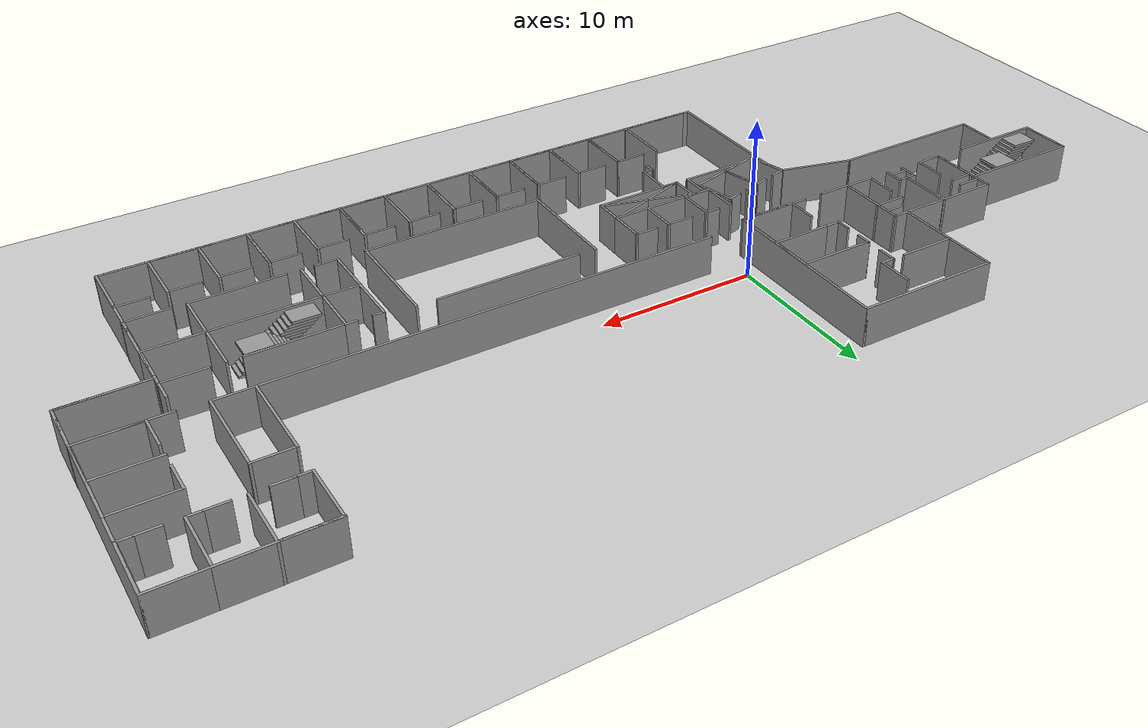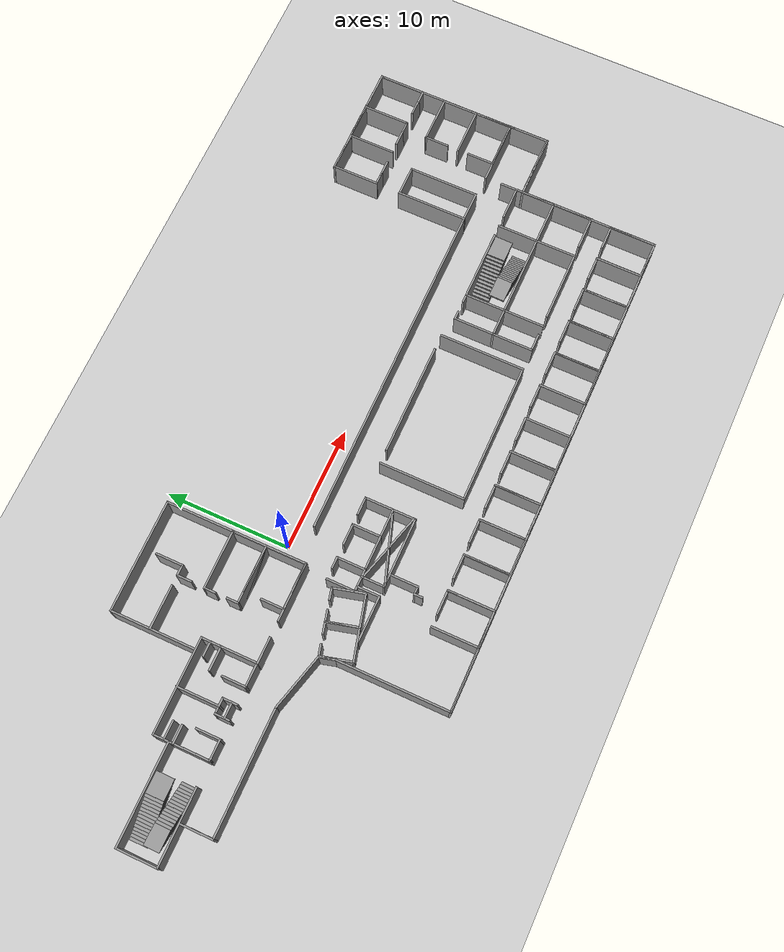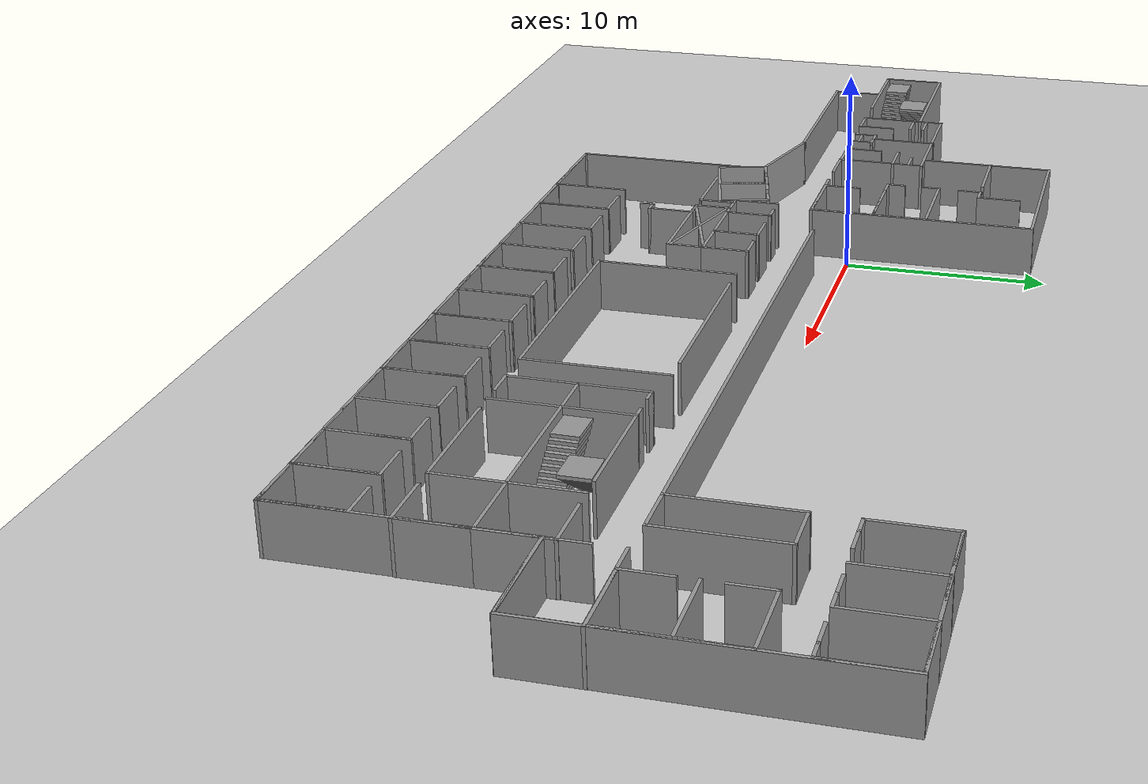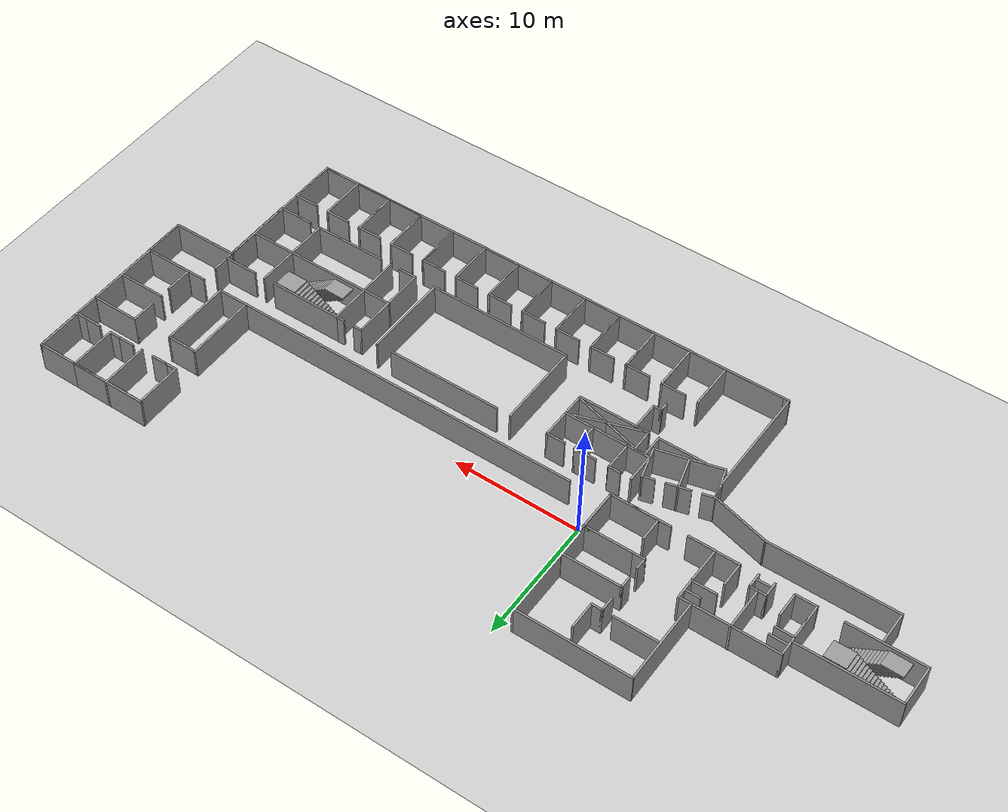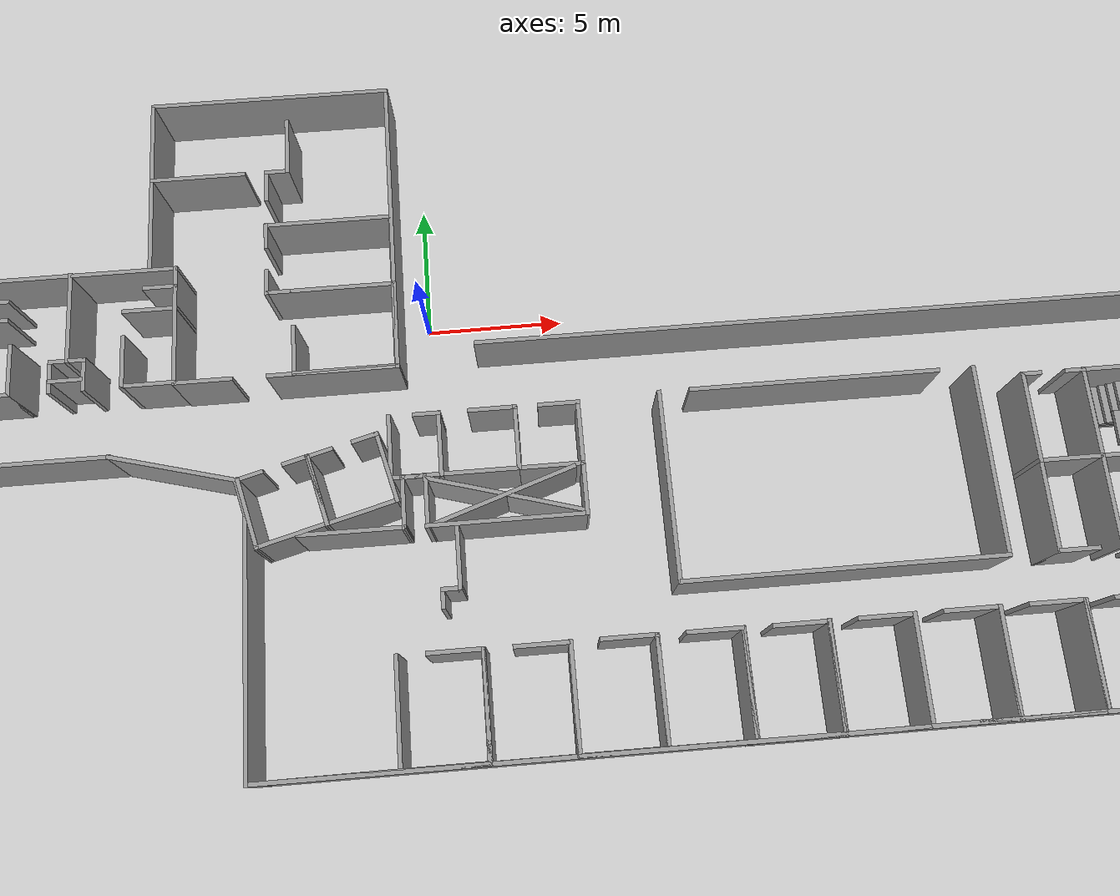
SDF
<sdf version="1.6">
 <world name="default">
  <light name="sun" type="directional">
   <pose>0 0 10 0 -0 0</pose>
   <diffuse>0.8 0.8 0.8 1</diffuse>
   <specular>0.2 0.2 0.2 1</specular>
   <attenuation>
    <range>1000</range>
    <constant>0.9</constant>
    <linear>0.01</linear>
    <quadratic>0.001</quadratic>
   </attenuation>
   <direction>-0.5 0.1 -0.9</direction>
  </light>
  <model name="ground_plane">
   <static>1</static>
   <link name="link">
    <collision name="collision">
     <geometry><plane><normal>0 0 1</normal><size>100 100</size></plane></geometry>
     <surface><friction><ode><mu>100</mu><mu2>50</mu2></ode></friction></surface>
    </collision>
    <visual name="visual">
     <cast_shadows>0</cast_shadows>
     <geometry><plane><normal>0 0 1</normal><size>100 100</size></plane></geometry>
     <material>
      <script><uri>file://media/materials/scripts/gazebo.material</uri><name>Gazebo/Grey</name></script>
     </material>
    </visual>
   </link>
  </model>
  <gravity>0 0 -9.8</gravity>
  <magnetic_field>6e-06 2.3e-05 -4.2e-05</magnetic_field>
  <atmosphere type="adiabatic"/>
  <physics name="default_physics" default="0" type="ode">
   <max_step_size>0.001</max_step_size>
   <real_time_factor>1</real_time_factor>
   <real_time_update_rate>1000</real_time_update_rate>
  </physics>
  <scene><ambient>0.4 0.4 0.4 1</ambient><background>0.7 0.7 0.7 1</background><shadows>1</shadows></scene>
  <spherical_coordinates>
   <surface_model>EARTH_WGS84</surface_model>
   <latitude_deg>0</latitude_deg>
   <longitude_deg>0</longitude_deg>
   <elevation>0</elevation>
   <heading_deg>0</heading_deg>
  </spherical_coordinates>
  <model name="201/202">
   <pose>-12.7229 0.167067 0 0 -0 0</pose>
   <link name="Wall_10">
    <collision name="Wall_10_Collision">
     <geometry><box><size>7.62002 0.15 2.5</size></box></geometry>
     <pose>0 0 1.25 0 -0 0</pose>
    </collision>
    <visual name="Wall_10_Visual">
     <pose>0 0 1.25 0 -0 0</pose>
     <geometry><box><size>7.62002 0.15 2.5</size></box></geometry>
     <material>
      <script><uri>file://media/materials/scripts/gazebo.material</uri><name>Gazebo/Grey</name></script>
      <ambient>1 1 1 1</ambient>
     </material>
     <meta><layer>0</layer></meta>
    </visual>
    <pose>-0.004655 2.1906 0 0 -0 3.14159</pose>
   </link>
   <link name="Wall_11">
    <collision name="Wall_11_Collision">
     <geometry><box><size>4.572 0.15 2.5</size></box></geometry>
     <pose>0 0 1.25 0 -0 0</pose>
    </collision>
    <visual name="Wall_11_Visual">
     <pose>0 0 1.25 0 -0 0</pose>
     <geometry><box><size>4.572 0.15 2.5</size></box></geometry>
     <material>
      <script><uri>file://media/materials/scripts/gazebo.material</uri><name>Gazebo/Grey</name></script>
      <ambient>1 1 1 1</ambient>
     </material>
     <meta><layer>0</layer></meta>
    </visual>
    <pose>-3.73965 -0.020398 0 0 -0 -1.5708</pose>
   </link>
   <link name="Wall_13">
    <collision name="Wall_13_Collision">
     <geometry><box><size>2 0.15 2.5</size></box></geometry>
     <pose>0 0 1.25 0 -0 0</pose>
    </collision>
    <visual name="Wall_13_Visual">
     <pose>0 0 1.25 0 -0 0</pose>
     <geometry><box><size>2 0.15 2.5</size></box></geometry>
     <material>
      <script><uri>file://media/materials/scripts/gazebo.material</uri><name>Gazebo/Grey</name></script>
      <ambient>1 1 1 1</ambient>
     </material>
     <meta><layer>0</layer></meta>
    </visual>
    <pose>2.80535 -2.23095 0 0 -0 3.14159</pose>
   </link>
   <link name="Wall_14">
    <collision name="Wall_14_Collision">
     <geometry><box><size>2 0.15 2.5</size></box></geometry>
     <pose>0 0 1.25 0 -0 0</pose>
    </collision>
    <visual name="Wall_14_Visual">
     <pose>0 0 1.25 0 -0 0</pose>
     <geometry><box><size>2 0.15 2.5</size></box></geometry>
     <material>
      <script><uri>file://media/materials/scripts/gazebo.material</uri><name>Gazebo/Grey</name></script>
      <ambient>1 1 1 1</ambient>
     </material>
     <meta><layer>0</layer></meta>
    </visual>
    <pose>1.88035 -1.30595 0 0 -0 1.5708</pose>
   </link>
   <link name="Wall_16">
    <collision name="Wall_16_Collision">
     <geometry><box><size>3.5 0.15 2.5</size></box></geometry>
     <pose>0 0 1.25 0 -0 0</pose>
    </collision>
    <visual name="Wall_16_Visual">
     <pose>0 0 1.25 0 -0 0</pose>
     <geometry><box><size>3.5 0.15 2.5</size></box></geometry>
     <material>
      <script><uri>file://media/materials/scripts/gazebo.material</uri><name>Gazebo/Grey</name></script>
      <ambient>1 1 1 1</ambient>
     </material>
     <meta><layer>0</layer></meta>
    </visual>
    <pose>-0.091763 0.556398 0 0 -0 -1.5708</pose>
   </link>
   <link name="Wall_17">
    <collision name="Wall_17_Collision">
     <geometry><box><size>0.75 0.15 2.5</size></box></geometry>
     <pose>0 0 1.25 0 -0 0</pose>
    </collision>
    <visual name="Wall_17_Visual">
     <pose>0 0 1.25 0 -0 0</pose>
     <geometry><box><size>0.75 0.15 2.5</size></box></geometry>
     <material>
      <script><uri>file://media/materials/scripts/gazebo.material</uri><name>Gazebo/Grey</name></script>
      <ambient>1 1 1 1</ambient>
     </material>
     <meta><layer>0</layer></meta>
    </visual>
    <pose>0.208236 -1.1186 0 0 -0 0</pose>
   </link>
   <link name="Wall_18">
    <collision name="Wall_18_Collision">
     <geometry><box><size>1.25 0.15 2.5</size></box></geometry>
     <pose>0 0 1.25 0 -0 0</pose>
    </collision>
    <visual name="Wall_18_Visual">
     <pose>0 0 1.25 0 -0 0</pose>
     <geometry><box><size>1.25 0.15 2.5</size></box></geometry>
     <material>
      <script><uri>file://media/materials/scripts/gazebo.material</uri><name>Gazebo/Grey</name></script>
      <ambient>1 1 1 1</ambient>
     </material>
     <meta><layer>0</layer></meta>
    </visual>
    <pose>0.508237 -1.6686 0 0 -0 -1.5708</pose>
   </link>
   <link name="Wall_20">
    <collision name="Wall_20_Collision">
     <geometry><box><size>0.75 0.15 2.5</size></box></geometry>
     <pose>0 0 1.25 0 -0 0</pose>
    </collision>
    <visual name="Wall_20_Visual">
     <pose>0 0 1.25 0 -0 0</pose>
     <geometry><box><size>0.75 0.15 2.5</size></box></geometry>
     <material>
      <script><uri>file://media/materials/scripts/gazebo.material</uri><name>Gazebo/Grey</name></script>
      <ambient>1 1 1 1</ambient>
     </material>
     <meta><layer>0</layer></meta>
    </visual>
    <pose>-0.391763 -1.1186 0 0 -0 3.14159</pose>
   </link>
   <link name="Wall_21">
    <collision name="Wall_21_Collision">
     <geometry><box><size>1.25 0.15 2.5</size></box></geometry>
     <pose>0 0 1.25 0 -0 0</pose>
    </collision>
    <visual name="Wall_21_Visual">
     <pose>0 0 1.25 0 -0 0</pose>
     <geometry><box><size>1.25 0.15 2.5</size></box></geometry>
     <material>
      <script><uri>file://media/materials/scripts/gazebo.material</uri><name>Gazebo/Grey</name></script>
      <ambient>1 1 1 1</ambient>
     </material>
     <meta><layer>0</layer></meta>
    </visual>
    <pose>-0.691764 -1.6686 0 0 -0 -1.5708</pose>
   </link>
   <link name="Wall_23">
    <collision name="Wall_23_Collision">
     <geometry><box><size>1.75 0.15 2.5</size></box></geometry>
     <pose>0 0 1.25 0 -0 0</pose>
    </collision>
    <visual name="Wall_23_Visual">
     <pose>0 0 1.25 0 -0 0</pose>
     <geometry><box><size>1.75 0.15 2.5</size></box></geometry>
     <material>
      <script><uri>file://media/materials/scripts/gazebo.material</uri><name>Gazebo/Grey</name></script>
      <ambient>1 1 1 1</ambient>
     </material>
     <meta><layer>0</layer></meta>
    </visual>
    <pose>-2.93966 -2.2314 0 0 -0 0</pose>
   </link>
   <link name="Wall_24">
    <collision name="Wall_24_Collision">
     <geometry><box><size>2 0.15 2.5</size></box></geometry>
     <pose>0 0 1.25 0 -0 0</pose>
    </collision>
    <visual name="Wall_24_Visual">
     <pose>0 0 1.25 0 -0 0</pose>
     <geometry><box><size>2 0.15 2.5</size></box></geometry>
     <material>
      <script><uri>file://media/materials/scripts/gazebo.material</uri><name>Gazebo/Grey</name></script>
      <ambient>1 1 1 1</ambient>
     </material>
     <meta><layer>0</layer></meta>
    </visual>
    <pose>-2.13965 -1.3064 0 0 -0 1.5708</pose>
   </link>
   <link name="Wall_28">
    <collision name="Wall_28_Collision">
     <geometry><box><size>1.5 0.15 2.5</size></box></geometry>
     <pose>0 0 1.25 0 -0 0</pose>
    </collision>
    <visual name="Wall_28_Visual">
     <pose>0 0 1.25 0 -0 0</pose>
     <geometry><box><size>1.5 0.15 2.5</size></box></geometry>
     <material>
      <script><uri>file://media/materials/scripts/gazebo.material</uri><name>Gazebo/Grey</name></script>
      <ambient>1 1 1 1</ambient>
     </material>
     <meta><layer>0</layer></meta>
    </visual>
    <pose>-3.01876 1.34811 0 0 -0 0</pose>
   </link>
   <link name="Wall_30">
    <collision name="Wall_30_Collision">
     <geometry><box><size>1.5 0.15 2.5</size></box></geometry>
     <pose>0 0 1.25 0 -0 0</pose>
    </collision>
    <visual name="Wall_30_Visual">
     <pose>0 0 1.25 0 -0 0</pose>
     <geometry><box><size>1.5 0.15 2.5</size></box></geometry>
     <material>
      <script><uri>file://media/materials/scripts/gazebo.material</uri><name>Gazebo/Grey</name></script>
      <ambient>1 1 1 1</ambient>
     </material>
     <meta><layer>0</layer></meta>
    </visual>
    <pose>-3.03023 0.625411 0 0 -0 0</pose>
   </link>
   <link name="Wall_32">
    <collision name="Wall_32_Collision">
     <geometry><box><size>2 0.15 2.5</size></box></geometry>
     <pose>0 0 1.25 0 -0 0</pose>
    </collision>
    <visual name="Wall_32_Visual">
     <pose>0 0 1.25 0 -0 0</pose>
     <geometry><box><size>2 0.15 2.5</size></box></geometry>
     <material>
      <script><uri>file://media/materials/scripts/gazebo.material</uri><name>Gazebo/Grey</name></script>
      <ambient>1 1 1 1</ambient>
     </material>
     <meta><layer>0</layer></meta>
    </visual>
    <pose>2.81466 0.625411 0 0 -0 3.14159</pose>
   </link>
   <link name="Wall_34">
    <collision name="Wall_34_Collision">
     <geometry><box><size>1.25 0.15 2.5</size></box></geometry>
     <pose>0 0 1.25 0 -0 0</pose>
    </collision>
    <visual name="Wall_34_Visual">
     <pose>0 0 1.25 0 -0 0</pose>
     <geometry><box><size>1.25 0.15 2.5</size></box></geometry>
     <material>
      <script><uri>file://media/materials/scripts/gazebo.material</uri><name>Gazebo/Grey</name></script>
      <ambient>1 1 1 1</ambient>
     </material>
     <meta><layer>0</layer></meta>
    </visual>
    <pose>3.16672 1.48576 0 0 -0 3.14159</pose>
   </link>
   <link name="Wall_36">
    <collision name="Wall_36_Collision">
     <geometry><box><size>1.25 0.15 2.5</size></box></geometry>
     <pose>0 0 1.25 0 -0 0</pose>
    </collision>
    <visual name="Wall_36_Visual">
     <pose>0 0 1.25 0 -0 0</pose>
     <geometry><box><size>1.25 0.15 2.5</size></box></geometry>
     <material>
      <script><uri>file://media/materials/scripts/gazebo.material</uri><name>Gazebo/Grey</name></script>
      <ambient>1 1 1 1</ambient>
     </material>
     <meta><layer>0</layer></meta>
    </visual>
    <pose>-0.138273 -1.8524 0 0 -0 0</pose>
   </link>
   <link name="Wall_9">
    <collision name="Wall_9_Collision">
     <geometry><box><size>4.572 0.15 2.5</size></box></geometry>
     <pose>0 0 1.25 0 -0 0</pose>
    </collision>
    <visual name="Wall_9_Visual">
     <pose>0 0 1.25 0 -0 0</pose>
     <geometry><box><size>4.572 0.15 2.5</size></box></geometry>
     <material>
      <script><uri>file://media/materials/scripts/gazebo.material</uri><name>Gazebo/Grey</name></script>
      <ambient>1 1 1 1</ambient>
     </material>
     <meta><layer>0</layer></meta>
    </visual>
    <pose>3.73035 -0.020175 0 0 -0 1.5708</pose>
   </link>
   <static>1</static>
  </model>
  <model name="197A">
   <link name="Wall_33">
    <pose>3.925 0 0 0 -0 1.5708</pose>
    <visual name="Wall_33_Visual">
     <pose>0 0 1.25 0 -0 0</pose>
     <geometry><box><size>3.336 0.15 2.5</size></box></geometry>
     <material>
      <script><uri>file://media/materials/scripts/gazebo.material</uri><name>Gazebo/Grey</name></script>
      <ambient>1 1 1 1</ambient>
      <shader type="pixel"/>
     </material>
     <meta><layer>0</layer></meta>
    </visual>
    <collision name="Wall_33_Collision">
     <pose>0 0 1.25 0 -0 0</pose>
     <geometry><box><size>3.336 0.15 2.5</size></box></geometry>
     <surface>
      <friction>
       <ode><mu>1</mu><mu2>1</mu2><fdir1>0 0 0</fdir1><slip1>0</slip1><slip2>0</slip2></ode>
       <torsional>
        <coefficient>1</coefficient>
        <patch_radius>0</patch_radius>
        <surface_radius>0</surface_radius>
        <use_patch_radius>1</use_patch_radius>
        <ode><slip>0</slip></ode>
       </torsional>
      </friction>
      <bounce><restitution_coefficient>0</restitution_coefficient><threshold>1e+06</threshold></bounce>
      <contact>
       <collide_without_contact>0</collide_without_contact>
       <collide_without_contact_bitmask>1</collide_without_contact_bitmask>
       <collide_bitmask>1</collide_bitmask>
       <ode>
        <soft_cfm>0</soft_cfm>
        <soft_erp>0.2</soft_erp>
        <kp>1e+13</kp>
        <kd>1</kd>
        <max_vel>0.01</max_vel>
        <min_depth>0</min_depth>
       </ode>
       <bullet>
        <split_impulse>1</split_impulse>
        <split_impulse_penetration_threshold>-0.01</split_impulse_penetration_threshold>
        <soft_cfm>0</soft_cfm>
        <soft_erp>0.2</soft_erp>
        <kp>1e+13</kp>
        <kd>1</kd>
       </bullet>
      </contact>
     </surface>
    </collision>
   </link>
   <link name="Wall_34">
    <pose>0 1.593 0 0 -0 3.14159</pose>
    <visual name="Wall_34_Visual">
     <pose>0 0 1.25 0 -0 0</pose>
     <geometry><box><size>8 0.15 2.5</size></box></geometry>
     <material>
      <script><uri>file://media/materials/scripts/gazebo.material</uri><name>Gazebo/Grey</name></script>
      <ambient>1 1 1 1</ambient>
      <shader type="pixel"/>
     </material>
     <meta><layer>0</layer></meta>
    </visual>
    <collision name="Wall_34_Collision">
     <pose>0 0 1.25 0 -0 0</pose>
     <geometry><box><size>8 0.15 2.5</size></box></geometry>
     <surface>
      <friction>
       <ode><mu>1</mu><mu2>1</mu2><fdir1>0 0 0</fdir1><slip1>0</slip1><slip2>0</slip2></ode>
       <torsional>
        <coefficient>1</coefficient>
        <patch_radius>0</patch_radius>
        <surface_radius>0</surface_radius>
        <use_patch_radius>1</use_patch_radius>
        <ode><slip>0</slip></ode>
       </torsional>
      </friction>
      <bounce><restitution_coefficient>0</restitution_coefficient><threshold>1e+06</threshold></bounce>
      <contact>
       <collide_without_contact>0</collide_without_contact>
       <collide_without_contact_bitmask>1</collide_without_contact_bitmask>
       <collide_bitmask>1</collide_bitmask>
       <ode>
        <soft_cfm>0</soft_cfm>
        <soft_erp>0.2</soft_erp>
        <kp>1e+13</kp>
        <kd>1</kd>
        <max_vel>0.01</max_vel>
        <min_depth>0</min_depth>
       </ode>
       <bullet>
        <split_impulse>1</split_impulse>
        <split_impulse_penetration_threshold>-0.01</split_impulse_penetration_threshold>
        <soft_cfm>0</soft_cfm>
        <soft_erp>0.2</soft_erp>
        <kp>1e+13</kp>
        <kd>1</kd>
       </bullet>
      </contact>
     </surface>
    </collision>
   </link>
   <link name="Wall_35">
    <pose>-3.925 0 0 0 0 -1.5708</pose>
    <visual name="Wall_35_Visual">
     <pose>0 0 1.25 0 -0 0</pose>
     <geometry><box><size>3.336 0.15 2.5</size></box></geometry>
     <material>
      <script><uri>file://media/materials/scripts/gazebo.material</uri><name>Gazebo/Grey</name></script>
      <ambient>1 1 1 1</ambient>
      <shader type="pixel"/>
     </material>
     <meta><layer>0</layer></meta>
    </visual>
    <collision name="Wall_35_Collision">
     <pose>0 0 1.25 0 -0 0</pose>
     <geometry><box><size>3.336 0.15 2.5</size></box></geometry>
     <surface>
      <friction>
       <ode><mu>1</mu><mu2>1</mu2><fdir1>0 0 0</fdir1><slip1>0</slip1><slip2>0</slip2></ode>
       <torsional>
        <coefficient>1</coefficient>
        <patch_radius>0</patch_radius>
        <surface_radius>0</surface_radius>
        <use_patch_radius>1</use_patch_radius>
        <ode><slip>0</slip></ode>
       </torsional>
      </friction>
      <bounce><restitution_coefficient>0</restitution_coefficient><threshold>1e+06</threshold></bounce>
      <contact>
       <collide_without_contact>0</collide_without_contact>
       <collide_without_contact_bitmask>1</collide_without_contact_bitmask>
       <collide_bitmask>1</collide_bitmask>
       <ode>
        <soft_cfm>0</soft_cfm>
        <soft_erp>0.2</soft_erp>
        <kp>1e+13</kp>
        <kd>1</kd>
        <max_vel>0.01</max_vel>
        <min_depth>0</min_depth>
       </ode>
       <bullet>
        <split_impulse>1</split_impulse>
        <split_impulse_penetration_threshold>-0.01</split_impulse_penetration_threshold>
        <soft_cfm>0</soft_cfm>
        <soft_erp>0.2</soft_erp>
        <kp>1e+13</kp>
        <kd>1</kd>
       </bullet>
      </contact>
     </surface>
    </collision>
   </link>
   <link name="Wall_37">
    <pose>-1 -1.593 0 0 -0 0</pose>
    <visual name="Wall_37_Visual">
     <pose>0 0 1.25 0 -0 0</pose>
     <geometry><box><size>6 0.15 2.5</size></box></geometry>
     <material>
      <script><uri>file://media/materials/scripts/gazebo.material</uri><name>Gazebo/Grey</name></script>
      <ambient>1 1 1 1</ambient>
      <shader type="pixel"/>
     </material>
     <meta><layer>0</layer></meta>
    </visual>
    <collision name="Wall_37_Collision">
     <pose>0 0 1.25 0 -0 0</pose>
     <geometry><box><size>6 0.15 2.5</size></box></geometry>
     <surface>
      <friction>
       <ode><mu>1</mu><mu2>1</mu2><fdir1>0 0 0</fdir1><slip1>0</slip1><slip2>0</slip2></ode>
       <torsional>
        <coefficient>1</coefficient>
        <patch_radius>0</patch_radius>
        <surface_radius>0</surface_radius>
        <use_patch_radius>1</use_patch_radius>
        <ode><slip>0</slip></ode>
       </torsional>
      </friction>
      <bounce><restitution_coefficient>0</restitution_coefficient><threshold>1e+06</threshold></bounce>
      <contact>
       <collide_without_contact>0</collide_without_contact>
       <collide_without_contact_bitmask>1</collide_without_contact_bitmask>
       <collide_bitmask>1</collide_bitmask>
       <ode>
        <soft_cfm>0</soft_cfm>
        <soft_erp>0.2</soft_erp>
        <kp>1e+13</kp>
        <kd>1</kd>
        <max_vel>0.01</max_vel>
        <min_depth>0</min_depth>
       </ode>
       <bullet>
        <split_impulse>1</split_impulse>
        <split_impulse_penetration_threshold>-0.01</split_impulse_penetration_threshold>
        <soft_cfm>0</soft_cfm>
        <soft_erp>0.2</soft_erp>
        <kp>1e+13</kp>
        <kd>1</kd>
       </bullet>
      </contact>
     </surface>
    </collision>
   </link>
   <static>1</static>
   <pose>-20.3831 -0.454376 0 0 -0 0</pose>
  </model>
  <model name="313-325_0_0">
   <link name="Wall_16">
    <pose>-1.44915 7.1e-05 0 0 0 -1.57088</pose>
    <visual name="Wall_16_Visual">
     <pose>0 0 1.25 0 -0 0</pose>
     <geometry><box><size>3.81 0.15 2.5</size></box></geometry>
     <material>
      <script><uri>file://media/materials/scripts/gazebo.material</uri><name>Gazebo/Grey</name></script>
      <ambient>1 1 1 1</ambient>
      <shader type="pixel"/>
     </material>
     <meta><layer>0</layer></meta>
    </visual>
    <collision name="Wall_16_Collision">
     <pose>0 0 1.25 0 -0 0</pose>
     <geometry><box><size>3.81 0.15 2.5</size></box></geometry>
     <surface>
      <friction>
       <ode><mu>1</mu><mu2>1</mu2><fdir1>0 0 0</fdir1><slip1>0</slip1><slip2>0</slip2></ode>
       <torsional>
        <coefficient>1</coefficient>
        <patch_radius>0</patch_radius>
        <surface_radius>0</surface_radius>
        <use_patch_radius>1</use_patch_radius>
        <ode><slip>0</slip></ode>
       </torsional>
      </friction>
      <bounce><restitution_coefficient>0</restitution_coefficient><threshold>1e+06</threshold></bounce>
      <contact>
       <collide_without_contact>0</collide_without_contact>
       <collide_without_contact_bitmask>1</collide_without_contact_bitmask>
       <collide_bitmask>1</collide_bitmask>
       <ode>
        <soft_cfm>0</soft_cfm>
        <soft_erp>0.2</soft_erp>
        <kp>1e+13</kp>
        <kd>1</kd>
        <max_vel>0.01</max_vel>
        <min_depth>0</min_depth>
       </ode>
       <bullet>
        <split_impulse>1</split_impulse>
        <split_impulse_penetration_threshold>-0.01</split_impulse_penetration_threshold>
        <soft_cfm>0</soft_cfm>
        <soft_erp>0.2</soft_erp>
        <kp>1e+13</kp>
        <kd>1</kd>
       </bullet>
      </contact>
     </surface>
    </collision>
   </link>
   <link name="Wall_18">
    <pose>1.449 -6.1e-05 0 0 -0 1.5708</pose>
    <visual name="Wall_18_Visual">
     <pose>0 0 1.25 0 -0 0</pose>
     <geometry><box><size>3.80974 0.15 2.5</size></box></geometry>
     <material>
      <script><uri>file://media/materials/scripts/gazebo.material</uri><name>Gazebo/Grey</name></script>
      <ambient>1 1 1 1</ambient>
      <shader type="pixel"/>
     </material>
     <meta><layer>0</layer></meta>
    </visual>
    <collision name="Wall_18_Collision">
     <pose>0 0 1.25 0 -0 0</pose>
     <geometry><box><size>3.80974 0.15 2.5</size></box></geometry>
     <surface>
      <friction>
       <ode><mu>1</mu><mu2>1</mu2><fdir1>0 0 0</fdir1><slip1>0</slip1><slip2>0</slip2></ode>
       <torsional>
        <coefficient>1</coefficient>
        <patch_radius>0</patch_radius>
        <surface_radius>0</surface_radius>
        <use_patch_radius>1</use_patch_radius>
        <ode><slip>0</slip></ode>
       </torsional>
      </friction>
      <bounce><restitution_coefficient>0</restitution_coefficient><threshold>1e+06</threshold></bounce>
      <contact>
       <collide_without_contact>0</collide_without_contact>
       <collide_without_contact_bitmask>1</collide_without_contact_bitmask>
       <collide_bitmask>1</collide_bitmask>
       <ode>
        <soft_cfm>0</soft_cfm>
        <soft_erp>0.2</soft_erp>
        <kp>1e+13</kp>
        <kd>1</kd>
        <max_vel>0.01</max_vel>
        <min_depth>0</min_depth>
       </ode>
       <bullet>
        <split_impulse>1</split_impulse>
        <split_impulse_penetration_threshold>-0.01</split_impulse_penetration_threshold>
        <soft_cfm>0</soft_cfm>
        <soft_erp>0.2</soft_erp>
        <kp>1e+13</kp>
        <kd>1</kd>
       </bullet>
      </contact>
     </surface>
    </collision>
   </link>
   <link name="Wall_19">
    <pose>2e-06 1.82994 0 0 -0 3.14159</pose>
    <visual name="Wall_19_Visual">
     <pose>0 0 1.25 0 -0 0</pose>
     <geometry><box><size>3.04862 0.15 2.5</size></box></geometry>
     <material>
      <script><uri>file://media/materials/scripts/gazebo.material</uri><name>Gazebo/Grey</name></script>
      <ambient>1 1 1 1</ambient>
      <shader type="pixel"/>
     </material>
     <meta><layer>0</layer></meta>
    </visual>
    <collision name="Wall_19_Collision">
     <pose>0 0 1.25 0 -0 0</pose>
     <geometry><box><size>3.04862 0.15 2.5</size></box></geometry>
     <surface>
      <friction>
       <ode><mu>1</mu><mu2>1</mu2><fdir1>0 0 0</fdir1><slip1>0</slip1><slip2>0</slip2></ode>
       <torsional>
        <coefficient>1</coefficient>
        <patch_radius>0</patch_radius>
        <surface_radius>0</surface_radius>
        <use_patch_radius>1</use_patch_radius>
        <ode><slip>0</slip></ode>
       </torsional>
      </friction>
      <bounce><restitution_coefficient>0</restitution_coefficient><threshold>1e+06</threshold></bounce>
      <contact>
       <collide_without_contact>0</collide_without_contact>
       <collide_without_contact_bitmask>1</collide_without_contact_bitmask>
       <collide_bitmask>1</collide_bitmask>
       <ode>
        <soft_cfm>0</soft_cfm>
        <soft_erp>0.2</soft_erp>
        <kp>1e+13</kp>
        <kd>1</kd>
        <max_vel>0.01</max_vel>
        <min_depth>0</min_depth>
       </ode>
       <bullet>
        <split_impulse>1</split_impulse>
        <split_impulse_penetration_threshold>-0.01</split_impulse_penetration_threshold>
        <soft_cfm>0</soft_cfm>
        <soft_erp>0.2</soft_erp>
        <kp>1e+13</kp>
        <kd>1</kd>
       </bullet>
      </contact>
     </surface>
    </collision>
   </link>
   <link name="Wall_22">
    <pose>-0.000153 -1.82993 0 0 0 -0.00022</pose>
    <visual name="Wall_22_Visual">
     <pose>0 0 1.25 0 -0 0</pose>
     <geometry><box><size>1.34831 0.15 2.5</size></box></geometry>
     <material>
      <script><uri>file://media/materials/scripts/gazebo.material</uri><name>Gazebo/Grey</name></script>
      <ambient>1 1 1 1</ambient>
      <shader type="pixel"/>
     </material>
     <meta><layer>0</layer></meta>
    </visual>
    <collision name="Wall_22_Collision">
     <pose>0 0 1.25 0 -0 0</pose>
     <geometry><box><size>1.34831 0.15 2.5</size></box></geometry>
     <surface>
      <friction>
       <ode><mu>1</mu><mu2>1</mu2><fdir1>0 0 0</fdir1><slip1>0</slip1><slip2>0</slip2></ode>
       <torsional>
        <coefficient>1</coefficient>
        <patch_radius>0</patch_radius>
        <surface_radius>0</surface_radius>
        <use_patch_radius>1</use_patch_radius>
        <ode><slip>0</slip></ode>
       </torsional>
      </friction>
      <bounce><restitution_coefficient>0</restitution_coefficient><threshold>1e+06</threshold></bounce>
      <contact>
       <collide_without_contact>0</collide_without_contact>
       <collide_without_contact_bitmask>1</collide_without_contact_bitmask>
       <collide_bitmask>1</collide_bitmask>
       <ode>
        <soft_cfm>0</soft_cfm>
        <soft_erp>0.2</soft_erp>
        <kp>1e+13</kp>
        <kd>1</kd>
        <max_vel>0.01</max_vel>
        <min_depth>0</min_depth>
       </ode>
       <bullet>
        <split_impulse>1</split_impulse>
        <split_impulse_penetration_threshold>-0.01</split_impulse_penetration_threshold>
        <soft_cfm>0</soft_cfm>
        <soft_erp>0.2</soft_erp>
        <kp>1e+13</kp>
        <kd>1</kd>
       </bullet>
      </contact>
     </surface>
    </collision>
   </link>
   <link name="Wall_23">
    <pose>1.024 -1.83006 0 0 -0 0</pose>
    <visual name="Wall_23_Visual">
     <pose>0 0 1.25 0 -0 0</pose>
     <geometry><box><size>1 0.15 2.5</size></box></geometry>
     <material>
      <script><uri>file://media/materials/scripts/gazebo.material</uri><name>Gazebo/Grey</name></script>
      <ambient>1 1 1 1</ambient>
      <shader type="pixel"/>
     </material>
     <meta><layer>0</layer></meta>
    </visual>
    <collision name="Wall_23_Collision">
     <pose>0 0 1.25 0 -0 0</pose>
     <geometry><box><size>1 0.15 2.5</size></box></geometry>
     <surface>
      <friction>
       <ode><mu>1</mu><mu2>1</mu2><fdir1>0 0 0</fdir1><slip1>0</slip1><slip2>0</slip2></ode>
       <torsional>
        <coefficient>1</coefficient>
        <patch_radius>0</patch_radius>
        <surface_radius>0</surface_radius>
        <use_patch_radius>1</use_patch_radius>
        <ode><slip>0</slip></ode>
       </torsional>
      </friction>
      <bounce><restitution_coefficient>0</restitution_coefficient><threshold>1e+06</threshold></bounce>
      <contact>
       <collide_without_contact>0</collide_without_contact>
       <collide_without_contact_bitmask>1</collide_without_contact_bitmask>
       <collide_bitmask>1</collide_bitmask>
       <ode>
        <soft_cfm>0</soft_cfm>
        <soft_erp>0.2</soft_erp>
        <kp>1e+13</kp>
        <kd>1</kd>
        <max_vel>0.01</max_vel>
        <min_depth>0</min_depth>
       </ode>
       <bullet>
        <split_impulse>1</split_impulse>
        <split_impulse_penetration_threshold>-0.01</split_impulse_penetration_threshold>
        <soft_cfm>0</soft_cfm>
        <soft_erp>0.2</soft_erp>
        <kp>1e+13</kp>
        <kd>1</kd>
       </bullet>
      </contact>
     </surface>
    </collision>
   </link>
   <static>1</static>
   <pose>33.8817 8.01736 0 0 -0 0</pose>
  </model>
  <model name="313-325_0">
   <link name="Wall_18">
    <pose>1.449 -6.1e-05 0 0 -0 1.5708</pose>
    <visual name="Wall_18_Visual">
     <pose>0 0 1.25 0 -0 0</pose>
     <geometry><box><size>3.80974 0.15 2.5</size></box></geometry>
     <material>
      <script><uri>file://media/materials/scripts/gazebo.material</uri><name>Gazebo/Grey</name></script>
      <ambient>1 1 1 1</ambient>
      <shader type="pixel"/>
     </material>
     <meta><layer>0</layer></meta>
    </visual>
    <collision name="Wall_18_Collision">
     <pose>0 0 1.25 0 -0 0</pose>
     <geometry><box><size>3.80974 0.15 2.5</size></box></geometry>
     <surface>
      <friction>
       <ode><mu>1</mu><mu2>1</mu2><fdir1>0 0 0</fdir1><slip1>0</slip1><slip2>0</slip2></ode>
       <torsional>
        <coefficient>1</coefficient>
        <patch_radius>0</patch_radius>
        <surface_radius>0</surface_radius>
        <use_patch_radius>1</use_patch_radius>
        <ode><slip>0</slip></ode>
       </torsional>
      </friction>
      <bounce><restitution_coefficient>0</restitution_coefficient><threshold>1e+06</threshold></bounce>
      <contact>
       <collide_without_contact>0</collide_without_contact>
       <collide_without_contact_bitmask>1</collide_without_contact_bitmask>
       <collide_bitmask>1</collide_bitmask>
       <ode>
        <soft_cfm>0</soft_cfm>
        <soft_erp>0.2</soft_erp>
        <kp>1e+13</kp>
        <kd>1</kd>
        <max_vel>0.01</max_vel>
        <min_depth>0</min_depth>
       </ode>
       <bullet>
        <split_impulse>1</split_impulse>
        <split_impulse_penetration_threshold>-0.01</split_impulse_penetration_threshold>
        <soft_cfm>0</soft_cfm>
        <soft_erp>0.2</soft_erp>
        <kp>1e+13</kp>
        <kd>1</kd>
       </bullet>
      </contact>
     </surface>
    </collision>
   </link>
   <link name="Wall_19">
    <pose>4e-06 1.82994 0 0 -0 3.14159</pose>
    <visual name="Wall_19_Visual">
     <pose>0 0 1.25 0 -0 0</pose>
     <geometry><box><size>3.04862 0.15 2.5</size></box></geometry>
     <material>
      <script><uri>file://media/materials/scripts/gazebo.material</uri><name>Gazebo/Grey</name></script>
      <ambient>1 1 1 1</ambient>
      <shader type="pixel"/>
     </material>
     <meta><layer>0</layer></meta>
    </visual>
    <collision name="Wall_19_Collision">
     <pose>0 0 1.25 0 -0 0</pose>
     <geometry><box><size>3.04862 0.15 2.5</size></box></geometry>
     <surface>
      <friction>
       <ode><mu>1</mu><mu2>1</mu2><fdir1>0 0 0</fdir1><slip1>0</slip1><slip2>0</slip2></ode>
       <torsional>
        <coefficient>1</coefficient>
        <patch_radius>0</patch_radius>
        <surface_radius>0</surface_radius>
        <use_patch_radius>1</use_patch_radius>
        <ode><slip>0</slip></ode>
       </torsional>
      </friction>
      <bounce><restitution_coefficient>0</restitution_coefficient><threshold>1e+06</threshold></bounce>
      <contact>
       <collide_without_contact>0</collide_without_contact>
       <collide_without_contact_bitmask>1</collide_without_contact_bitmask>
       <collide_bitmask>1</collide_bitmask>
       <ode>
        <soft_cfm>0</soft_cfm>
        <soft_erp>0.2</soft_erp>
        <kp>1e+13</kp>
        <kd>1</kd>
        <max_vel>0.01</max_vel>
        <min_depth>0</min_depth>
       </ode>
       <bullet>
        <split_impulse>1</split_impulse>
        <split_impulse_penetration_threshold>-0.01</split_impulse_penetration_threshold>
        <soft_cfm>0</soft_cfm>
        <soft_erp>0.2</soft_erp>
        <kp>1e+13</kp>
        <kd>1</kd>
       </bullet>
      </contact>
     </surface>
    </collision>
   </link>
   <link name="Wall_22">
    <pose>-0.000153 -1.82993 0 0 0 -0.00022</pose>
    <visual name="Wall_22_Visual">
     <pose>0 0 1.25 0 -0 0</pose>
     <geometry><box><size>1.34831 0.15 2.5</size></box></geometry>
     <material>
      <script><uri>file://media/materials/scripts/gazebo.material</uri><name>Gazebo/Grey</name></script>
      <ambient>1 1 1 1</ambient>
      <shader type="pixel"/>
     </material>
     <meta><layer>0</layer></meta>
    </visual>
    <collision name="Wall_22_Collision">
     <pose>0 0 1.25 0 -0 0</pose>
     <geometry><box><size>1.34831 0.15 2.5</size></box></geometry>
     <surface>
      <friction>
       <ode><mu>1</mu><mu2>1</mu2><fdir1>0 0 0</fdir1><slip1>0</slip1><slip2>0</slip2></ode>
       <torsional>
        <coefficient>1</coefficient>
        <patch_radius>0</patch_radius>
        <surface_radius>0</surface_radius>
        <use_patch_radius>1</use_patch_radius>
        <ode><slip>0</slip></ode>
       </torsional>
      </friction>
      <bounce><restitution_coefficient>0</restitution_coefficient><threshold>1e+06</threshold></bounce>
      <contact>
       <collide_without_contact>0</collide_without_contact>
       <collide_without_contact_bitmask>1</collide_without_contact_bitmask>
       <collide_bitmask>1</collide_bitmask>
       <ode>
        <soft_cfm>0</soft_cfm>
        <soft_erp>0.2</soft_erp>
        <kp>1e+13</kp>
        <kd>1</kd>
        <max_vel>0.01</max_vel>
        <min_depth>0</min_depth>
       </ode>
       <bullet>
        <split_impulse>1</split_impulse>
        <split_impulse_penetration_threshold>-0.01</split_impulse_penetration_threshold>
        <soft_cfm>0</soft_cfm>
        <soft_erp>0.2</soft_erp>
        <kp>1e+13</kp>
        <kd>1</kd>
       </bullet>
      </contact>
     </surface>
    </collision>
   </link>
   <link name="Wall_23">
    <pose>1.024 -1.83006 0 0 -0 0</pose>
    <visual name="Wall_23_Visual">
     <pose>0 0 1.25 0 -0 0</pose>
     <geometry><box><size>1 0.15 2.5</size></box></geometry>
     <material>
      <script><uri>file://media/materials/scripts/gazebo.material</uri><name>Gazebo/Grey</name></script>
      <ambient>1 1 1 1</ambient>
      <shader type="pixel"/>
     </material>
     <meta><layer>0</layer></meta>
    </visual>
    <collision name="Wall_23_Collision">
     <pose>0 0 1.25 0 -0 0</pose>
     <geometry><box><size>1 0.15 2.5</size></box></geometry>
     <surface>
      <friction>
       <ode><mu>1</mu><mu2>1</mu2><fdir1>0 0 0</fdir1><slip1>0</slip1><slip2>0</slip2></ode>
       <torsional>
        <coefficient>1</coefficient>
        <patch_radius>0</patch_radius>
        <surface_radius>0</surface_radius>
        <use_patch_radius>1</use_patch_radius>
        <ode><slip>0</slip></ode>
       </torsional>
      </friction>
      <bounce><restitution_coefficient>0</restitution_coefficient><threshold>1e+06</threshold></bounce>
      <contact>
       <collide_without_contact>0</collide_without_contact>
       <collide_without_contact_bitmask>1</collide_without_contact_bitmask>
       <collide_bitmask>1</collide_bitmask>
       <ode>
        <soft_cfm>0</soft_cfm>
        <soft_erp>0.2</soft_erp>
        <kp>1e+13</kp>
        <kd>1</kd>
        <max_vel>0.01</max_vel>
        <min_depth>0</min_depth>
       </ode>
       <bullet>
        <split_impulse>1</split_impulse>
        <split_impulse_penetration_threshold>-0.01</split_impulse_penetration_threshold>
        <soft_cfm>0</soft_cfm>
        <soft_erp>0.2</soft_erp>
        <kp>1e+13</kp>
        <kd>1</kd>
       </bullet>
      </contact>
     </surface>
    </collision>
   </link>
   <static>1</static>
   <pose>36.9768 8.00686 0 0 -0 0</pose>
  </model>
  <model name="313-325">
   <link name="Wall_16">
    <pose>-1.44915 7.1e-05 0 0 0 -1.57088</pose>
    <visual name="Wall_16_Visual">
     <pose>0 0 1.25 0 -0 0</pose>
     <geometry><box><size>3.81 0.15 2.5</size></box></geometry>
     <material>
      <script><uri>file://media/materials/scripts/gazebo.material</uri><name>Gazebo/Grey</name></script>
      <ambient>1 1 1 1</ambient>
      <shader type="pixel"/>
     </material>
     <meta><layer>0</layer></meta>
    </visual>
    <collision name="Wall_16_Collision">
     <pose>0 0 1.25 0 -0 0</pose>
     <geometry><box><size>3.81 0.15 2.5</size></box></geometry>
     <surface>
      <friction>
       <ode><mu>1</mu><mu2>1</mu2><fdir1>0 0 0</fdir1><slip1>0</slip1><slip2>0</slip2></ode>
       <torsional>
        <coefficient>1</coefficient>
        <patch_radius>0</patch_radius>
        <surface_radius>0</surface_radius>
        <use_patch_radius>1</use_patch_radius>
        <ode><slip>0</slip></ode>
       </torsional>
      </friction>
      <bounce><restitution_coefficient>0</restitution_coefficient><threshold>1e+06</threshold></bounce>
      <contact>
       <collide_without_contact>0</collide_without_contact>
       <collide_without_contact_bitmask>1</collide_without_contact_bitmask>
       <collide_bitmask>1</collide_bitmask>
       <ode>
        <soft_cfm>0</soft_cfm>
        <soft_erp>0.2</soft_erp>
        <kp>1e+13</kp>
        <kd>1</kd>
        <max_vel>0.01</max_vel>
        <min_depth>0</min_depth>
       </ode>
       <bullet>
        <split_impulse>1</split_impulse>
        <split_impulse_penetration_threshold>-0.01</split_impulse_penetration_threshold>
        <soft_cfm>0</soft_cfm>
        <soft_erp>0.2</soft_erp>
        <kp>1e+13</kp>
        <kd>1</kd>
       </bullet>
      </contact>
     </surface>
    </collision>
   </link>
   <link name="Wall_19">
    <pose>2e-06 1.82994 0 0 -0 3.14159</pose>
    <visual name="Wall_19_Visual">
     <pose>0 0 1.25 0 -0 0</pose>
     <geometry><box><size>3.04862 0.15 2.5</size></box></geometry>
     <material>
      <script><uri>file://media/materials/scripts/gazebo.material</uri><name>Gazebo/Grey</name></script>
      <ambient>1 1 1 1</ambient>
      <shader type="pixel"/>
     </material>
     <meta><layer>0</layer></meta>
    </visual>
    <collision name="Wall_19_Collision">
     <pose>0 0 1.25 0 -0 0</pose>
     <geometry><box><size>3.04862 0.15 2.5</size></box></geometry>
     <surface>
      <friction>
       <ode><mu>1</mu><mu2>1</mu2><fdir1>0 0 0</fdir1><slip1>0</slip1><slip2>0</slip2></ode>
       <torsional>
        <coefficient>1</coefficient>
        <patch_radius>0</patch_radius>
        <surface_radius>0</surface_radius>
        <use_patch_radius>1</use_patch_radius>
        <ode><slip>0</slip></ode>
       </torsional>
      </friction>
      <bounce><restitution_coefficient>0</restitution_coefficient><threshold>1e+06</threshold></bounce>
      <contact>
       <collide_without_contact>0</collide_without_contact>
       <collide_without_contact_bitmask>1</collide_without_contact_bitmask>
       <collide_bitmask>1</collide_bitmask>
       <ode>
        <soft_cfm>0</soft_cfm>
        <soft_erp>0.2</soft_erp>
        <kp>1e+13</kp>
        <kd>1</kd>
        <max_vel>0.01</max_vel>
        <min_depth>0</min_depth>
       </ode>
       <bullet>
        <split_impulse>1</split_impulse>
        <split_impulse_penetration_threshold>-0.01</split_impulse_penetration_threshold>
        <soft_cfm>0</soft_cfm>
        <soft_erp>0.2</soft_erp>
        <kp>1e+13</kp>
        <kd>1</kd>
       </bullet>
      </contact>
     </surface>
    </collision>
   </link>
   <link name="Wall_22">
    <pose>-0.000153 -1.82993 0 0 0 -0.00022</pose>
    <visual name="Wall_22_Visual">
     <pose>0 0 1.25 0 -0 0</pose>
     <geometry><box><size>1.34831 0.15 2.5</size></box></geometry>
     <material>
      <script><uri>file://media/materials/scripts/gazebo.material</uri><name>Gazebo/Grey</name></script>
      <ambient>1 1 1 1</ambient>
      <shader type="pixel"/>
     </material>
     <meta><layer>0</layer></meta>
    </visual>
    <collision name="Wall_22_Collision">
     <pose>0 0 1.25 0 -0 0</pose>
     <geometry><box><size>1.34831 0.15 2.5</size></box></geometry>
     <surface>
      <friction>
       <ode><mu>1</mu><mu2>1</mu2><fdir1>0 0 0</fdir1><slip1>0</slip1><slip2>0</slip2></ode>
       <torsional>
        <coefficient>1</coefficient>
        <patch_radius>0</patch_radius>
        <surface_radius>0</surface_radius>
        <use_patch_radius>1</use_patch_radius>
        <ode><slip>0</slip></ode>
       </torsional>
      </friction>
      <bounce><restitution_coefficient>0</restitution_coefficient><threshold>1e+06</threshold></bounce>
      <contact>
       <collide_without_contact>0</collide_without_contact>
       <collide_without_contact_bitmask>1</collide_without_contact_bitmask>
       <collide_bitmask>1</collide_bitmask>
       <ode>
        <soft_cfm>0</soft_cfm>
        <soft_erp>0.2</soft_erp>
        <kp>1e+13</kp>
        <kd>1</kd>
        <max_vel>0.01</max_vel>
        <min_depth>0</min_depth>
       </ode>
       <bullet>
        <split_impulse>1</split_impulse>
        <split_impulse_penetration_threshold>-0.01</split_impulse_penetration_threshold>
        <soft_cfm>0</soft_cfm>
        <soft_erp>0.2</soft_erp>
        <kp>1e+13</kp>
        <kd>1</kd>
       </bullet>
      </contact>
     </surface>
    </collision>
   </link>
   <link name="Wall_23">
    <pose>-0.957397 -1.83006 0 0 -0 0</pose>
    <visual name="Wall_23_Visual">
     <pose>0 0 1.25 0 -0 0</pose>
     <geometry><box><size>1 0.15 2.5</size></box></geometry>
     <material>
      <script><uri>file://media/materials/scripts/gazebo.material</uri><name>Gazebo/Grey</name></script>
      <ambient>1 1 1 1</ambient>
      <shader type="pixel"/>
     </material>
     <meta><layer>0</layer></meta>
    </visual>
    <collision name="Wall_23_Collision">
     <pose>0 0 1.25 0 -0 0</pose>
     <geometry><box><size>1 0.15 2.5</size></box></geometry>
     <surface>
      <friction>
       <ode><mu>1</mu><mu2>1</mu2><fdir1>0 0 0</fdir1><slip1>0</slip1><slip2>0</slip2></ode>
       <torsional>
        <coefficient>1</coefficient>
        <patch_radius>0</patch_radius>
        <surface_radius>0</surface_radius>
        <use_patch_radius>1</use_patch_radius>
        <ode><slip>0</slip></ode>
       </torsional>
      </friction>
      <bounce><restitution_coefficient>0</restitution_coefficient><threshold>1e+06</threshold></bounce>
      <contact>
       <collide_without_contact>0</collide_without_contact>
       <collide_without_contact_bitmask>1</collide_without_contact_bitmask>
       <collide_bitmask>1</collide_bitmask>
       <ode>
        <soft_cfm>0</soft_cfm>
        <soft_erp>0.2</soft_erp>
        <kp>1e+13</kp>
        <kd>1</kd>
        <max_vel>0.01</max_vel>
        <min_depth>0</min_depth>
       </ode>
       <bullet>
        <split_impulse>1</split_impulse>
        <split_impulse_penetration_threshold>-0.01</split_impulse_penetration_threshold>
        <soft_cfm>0</soft_cfm>
        <soft_erp>0.2</soft_erp>
        <kp>1e+13</kp>
        <kd>1</kd>
       </bullet>
      </contact>
     </surface>
    </collision>
   </link>
   <static>1</static>
   <pose>30.7901 7.99382 0 0 -0 0</pose>
  </model>
  <model name="526">
   <link name="Wall_29">
    <pose>0 -1.592 0 0 -0 0</pose>
    <visual name="Wall_29_Visual">
     <pose>0 0 1.25 0 -0 0</pose>
     <geometry><box><size>5.239 0.15 2.5</size></box></geometry>
     <material>
      <script><uri>file://media/materials/scripts/gazebo.material</uri><name>Gazebo/Grey</name></script>
      <ambient>1 1 1 1</ambient>
      <shader type="pixel"/>
     </material>
     <meta><layer>0</layer></meta>
    </visual>
    <collision name="Wall_29_Collision">
     <pose>0 0 1.25 0 -0 0</pose>
     <geometry><box><size>5.239 0.15 2.5</size></box></geometry>
     <surface>
      <friction>
       <ode><mu>1</mu><mu2>1</mu2><fdir1>0 0 0</fdir1><slip1>0</slip1><slip2>0</slip2></ode>
       <torsional>
        <coefficient>1</coefficient>
        <patch_radius>0</patch_radius>
        <surface_radius>0</surface_radius>
        <use_patch_radius>1</use_patch_radius>
        <ode><slip>0</slip></ode>
       </torsional>
      </friction>
      <bounce><restitution_coefficient>0</restitution_coefficient><threshold>1e+06</threshold></bounce>
      <contact>
       <collide_without_contact>0</collide_without_contact>
       <collide_without_contact_bitmask>1</collide_without_contact_bitmask>
       <collide_bitmask>1</collide_bitmask>
       <ode>
        <soft_cfm>0</soft_cfm>
        <soft_erp>0.2</soft_erp>
        <kp>1e+13</kp>
        <kd>1</kd>
        <max_vel>0.01</max_vel>
        <min_depth>0</min_depth>
       </ode>
       <bullet>
        <split_impulse>1</split_impulse>
        <split_impulse_penetration_threshold>-0.01</split_impulse_penetration_threshold>
        <soft_cfm>0</soft_cfm>
        <soft_erp>0.2</soft_erp>
        <kp>1e+13</kp>
        <kd>1</kd>
       </bullet>
      </contact>
     </surface>
    </collision>
   </link>
   <link name="Wall_30">
    <pose>2.5445 0 0 0 -0 1.5708</pose>
    <visual name="Wall_30_Visual">
     <pose>0 0 1.25 0 -0 0</pose>
     <geometry><box><size>3.334 0.15 2.5</size></box></geometry>
     <material>
      <script><uri>file://media/materials/scripts/gazebo.material</uri><name>Gazebo/Grey</name></script>
      <ambient>1 1 1 1</ambient>
      <shader type="pixel"/>
     </material>
     <meta><layer>0</layer></meta>
    </visual>
    <collision name="Wall_30_Collision">
     <pose>0 0 1.25 0 -0 0</pose>
     <geometry><box><size>3.334 0.15 2.5</size></box></geometry>
     <surface>
      <friction>
       <ode><mu>1</mu><mu2>1</mu2><fdir1>0 0 0</fdir1><slip1>0</slip1><slip2>0</slip2></ode>
       <torsional>
        <coefficient>1</coefficient>
        <patch_radius>0</patch_radius>
        <surface_radius>0</surface_radius>
        <use_patch_radius>1</use_patch_radius>
        <ode><slip>0</slip></ode>
       </torsional>
      </friction>
      <bounce><restitution_coefficient>0</restitution_coefficient><threshold>1e+06</threshold></bounce>
      <contact>
       <collide_without_contact>0</collide_without_contact>
       <collide_without_contact_bitmask>1</collide_without_contact_bitmask>
       <collide_bitmask>1</collide_bitmask>
       <ode>
        <soft_cfm>0</soft_cfm>
        <soft_erp>0.2</soft_erp>
        <kp>1e+13</kp>
        <kd>1</kd>
        <max_vel>0.01</max_vel>
        <min_depth>0</min_depth>
       </ode>
       <bullet>
        <split_impulse>1</split_impulse>
        <split_impulse_penetration_threshold>-0.01</split_impulse_penetration_threshold>
        <soft_cfm>0</soft_cfm>
        <soft_erp>0.2</soft_erp>
        <kp>1e+13</kp>
        <kd>1</kd>
       </bullet>
      </contact>
     </surface>
    </collision>
   </link>
   <link name="Wall_31">
    <pose>0 1.592 0 0 -0 3.14159</pose>
    <visual name="Wall_31_Visual">
     <pose>0 0 1.25 0 -0 0</pose>
     <geometry><box><size>5.239 0.15 2.5</size></box></geometry>
     <material>
      <script><uri>file://media/materials/scripts/gazebo.material</uri><name>Gazebo/Grey</name></script>
      <ambient>1 1 1 1</ambient>
      <shader type="pixel"/>
     </material>
     <meta><layer>0</layer></meta>
    </visual>
    <collision name="Wall_31_Collision">
     <pose>0 0 1.25 0 -0 0</pose>
     <geometry><box><size>5.239 0.15 2.5</size></box></geometry>
     <surface>
      <friction>
       <ode><mu>1</mu><mu2>1</mu2><fdir1>0 0 0</fdir1><slip1>0</slip1><slip2>0</slip2></ode>
       <torsional>
        <coefficient>1</coefficient>
        <patch_radius>0</patch_radius>
        <surface_radius>0</surface_radius>
        <use_patch_radius>1</use_patch_radius>
        <ode><slip>0</slip></ode>
       </torsional>
      </friction>
      <bounce><restitution_coefficient>0</restitution_coefficient><threshold>1e+06</threshold></bounce>
      <contact>
       <collide_without_contact>0</collide_without_contact>
       <collide_without_contact_bitmask>1</collide_without_contact_bitmask>
       <collide_bitmask>1</collide_bitmask>
       <ode>
        <soft_cfm>0</soft_cfm>
        <soft_erp>0.2</soft_erp>
        <kp>1e+13</kp>
        <kd>1</kd>
        <max_vel>0.01</max_vel>
        <min_depth>0</min_depth>
       </ode>
       <bullet>
        <split_impulse>1</split_impulse>
        <split_impulse_penetration_threshold>-0.01</split_impulse_penetration_threshold>
        <soft_cfm>0</soft_cfm>
        <soft_erp>0.2</soft_erp>
        <kp>1e+13</kp>
        <kd>1</kd>
       </bullet>
      </contact>
     </surface>
    </collision>
   </link>
   <link name="Wall_33">
    <pose>-2.5445 -0.772027 0 0 -0 1.5708</pose>
    <inertial>
     <inertia><ixx>0</ixx><ixy>0</ixy><ixz>0</ixz><iyy>0</iyy><iyz>0</iyz><izz>0</izz></inertia>
     <mass>0</mass>
    </inertial>
    <visual name="Wall_33_Visual">
     <pose>0 0 1.25 0 -0 0</pose>
     <geometry><box><size>2.10908 0.15 2.5</size></box></geometry>
     <material>
      <script><uri>file://media/materials/scripts/gazebo.material</uri><name>Gazebo/Grey</name></script>
      <ambient>1 1 1 1</ambient>
      <shader type="pixel"/>
     </material>
     <meta><layer>0</layer></meta>
    </visual>
    <collision name="Wall_33_Collision">
     <pose>0 0 1.25 0 -0 0</pose>
     <geometry><box><size>2.10908 0.15 2.5</size></box></geometry>
     <surface>
      <friction>
       <ode><mu>1</mu><mu2>1</mu2><fdir1>0 0 0</fdir1><slip1>0</slip1><slip2>0</slip2></ode>
       <torsional>
        <coefficient>1</coefficient>
        <patch_radius>0</patch_radius>
        <surface_radius>0</surface_radius>
        <use_patch_radius>1</use_patch_radius>
        <ode><slip>0</slip></ode>
       </torsional>
      </friction>
      <bounce><restitution_coefficient>0</restitution_coefficient><threshold>1e+06</threshold></bounce>
      <contact>
       <collide_without_contact>0</collide_without_contact>
       <collide_without_contact_bitmask>1</collide_without_contact_bitmask>
       <collide_bitmask>1</collide_bitmask>
       <ode>
        <soft_cfm>0</soft_cfm>
        <soft_erp>0.2</soft_erp>
        <kp>1e+13</kp>
        <kd>1</kd>
        <max_vel>0.01</max_vel>
        <min_depth>0</min_depth>
       </ode>
       <bullet>
        <split_impulse>1</split_impulse>
        <split_impulse_penetration_threshold>-0.01</split_impulse_penetration_threshold>
        <soft_cfm>0</soft_cfm>
        <soft_erp>0.2</soft_erp>
        <kp>1e+13</kp>
        <kd>1</kd>
       </bullet>
      </contact>
     </surface>
    </collision>
   </link>
   <static>1</static>
   <pose>35.9237 -3.16356 0 0 -0 0</pose>
  </model>
  <model name="527/528">
   <pose>36.5993 1.34886 0 0 -0 0</pose>
   <link name="Wall_35">
    <collision name="Wall_35_Collision">
     <geometry><box><size>3.81 0.15 2.5</size></box></geometry>
     <pose>0 0 1.25 0 -0 0</pose>
    </collision>
    <visual name="Wall_35_Visual">
     <pose>0 0 1.25 0 -0 0</pose>
     <geometry><box><size>3.81 0.15 2.5</size></box></geometry>
     <material>
      <script><uri>file://media/materials/scripts/gazebo.material</uri><name>Gazebo/Grey</name></script>
      <ambient>1 1 1 1</ambient>
     </material>
     <meta><layer>0</layer></meta>
    </visual>
    <pose>0.0065 -2.9015 0 0 -0 0</pose>
   </link>
   <link name="Wall_36">
    <collision name="Wall_36_Collision">
     <geometry><box><size>5.953 0.15 2.5</size></box></geometry>
     <pose>0 0 1.25 0 -0 0</pose>
    </collision>
    <visual name="Wall_36_Visual">
     <pose>0 0 1.25 0 -0 0</pose>
     <geometry><box><size>5.953 0.15 2.5</size></box></geometry>
     <material>
      <script><uri>file://media/materials/scripts/gazebo.material</uri><name>Gazebo/Grey</name></script>
      <ambient>1 1 1 1</ambient>
     </material>
     <meta><layer>0</layer></meta>
    </visual>
    <pose>1.8365 0 0 0 -0 1.5708</pose>
   </link>
   <link name="Wall_37">
    <collision name="Wall_37_Collision">
     <geometry><box><size>3.81 0.15 2.5</size></box></geometry>
     <pose>0 0 1.25 0 -0 0</pose>
    </collision>
    <visual name="Wall_37_Visual">
     <pose>0 0 1.25 0 -0 0</pose>
     <geometry><box><size>3.81 0.15 2.5</size></box></geometry>
     <material>
      <script><uri>file://media/materials/scripts/gazebo.material</uri><name>Gazebo/Grey</name></script>
      <ambient>1 1 1 1</ambient>
     </material>
     <meta><layer>0</layer></meta>
    </visual>
    <pose>0.0065 2.9015 0 0 -0 3.14159</pose>
   </link>
   <link name="Wall_40">
    <collision name="Wall_40_Collision">
     <geometry><box><size>3.75 0.15 2.5</size></box></geometry>
     <pose>0 0 1.25 0 -0 0</pose>
    </collision>
    <visual name="Wall_40_Visual">
     <pose>0 0 1.25 0 -0 0</pose>
     <geometry><box><size>3.75 0.15 2.5</size></box></geometry>
     <material>
      <script><uri>file://media/materials/scripts/gazebo.material</uri><name>Gazebo/Grey</name></script>
      <ambient>1 1 1 1</ambient>
     </material>
     <meta><layer>0</layer></meta>
    </visual>
    <pose>-0.0365 0.099032 0 0 -0 3.14159</pose>
   </link>
   <link name="Wall_42">
    <collision name="Wall_42_Collision">
     <geometry><box><size>2.25 0.15 2.5</size></box></geometry>
     <pose>0 0 1.25 0 -0 0</pose>
    </collision>
    <visual name="Wall_42_Visual">
     <pose>0 0 1.25 0 -0 0</pose>
     <geometry><box><size>2.25 0.15 2.5</size></box></geometry>
     <material>
      <script><uri>file://media/materials/scripts/gazebo.material</uri><name>Gazebo/Grey</name></script>
      <ambient>1 1 1 1</ambient>
     </material>
     <meta><layer>0</layer></meta>
    </visual>
    <pose>-1.8235 -1.8515 0 0 -0 1.5708</pose>
   </link>
   <link name="Wall_44">
    <collision name="Wall_44_Collision">
     <geometry><box><size>2.003 0.15 2.5</size></box></geometry>
     <pose>0 0 1.25 0 -0 0</pose>
    </collision>
    <visual name="Wall_44_Visual">
     <pose>0 0 1.25 0 -0 0</pose>
     <geometry><box><size>2.003 0.15 2.5</size></box></geometry>
     <material>
      <script><uri>file://media/materials/scripts/gazebo.material</uri><name>Gazebo/Grey</name></script>
      <ambient>1 1 1 1</ambient>
     </material>
     <meta><layer>0</layer></meta>
    </visual>
    <pose>-1.8235 1.975 0 0 -0 1.5708</pose>
   </link>
   <static>1</static>
  </model>
  <model name="532">
   <pose>30.5387 1.34318 0 0 -0 0</pose>
   <link name="Wall_46">
    <collision name="Wall_46_Collision">
     <geometry><box><size>2.381 0.15 2.5</size></box></geometry>
     <pose>0 0 1.25 0 -0 0</pose>
    </collision>
    <visual name="Wall_46_Visual">
     <pose>0 0 1.25 0 -0 0</pose>
     <geometry><box><size>2.381 0.15 2.5</size></box></geometry>
     <material>
      <script><uri>file://media/materials/scripts/gazebo.material</uri><name>Gazebo/Grey</name></script>
      <ambient>1 1 1 1</ambient>
     </material>
     <meta><layer>0</layer></meta>
    </visual>
    <pose>0 -2.7825 0 0 -0 0</pose>
   </link>
   <link name="Wall_47">
    <collision name="Wall_47_Collision">
     <geometry><box><size>5.715 0.15 2.5</size></box></geometry>
     <pose>0 0 1.25 0 -0 0</pose>
    </collision>
    <visual name="Wall_47_Visual">
     <pose>0 0 1.25 0 -0 0</pose>
     <geometry><box><size>5.715 0.15 2.5</size></box></geometry>
     <material>
      <script><uri>file://media/materials/scripts/gazebo.material</uri><name>Gazebo/Grey</name></script>
      <ambient>1 1 1 1</ambient>
     </material>
     <meta><layer>0</layer></meta>
    </visual>
    <pose>1.1155 0 0 0 -0 1.5708</pose>
   </link>
   <link name="Wall_48">
    <collision name="Wall_48_Collision">
     <geometry><box><size>2.381 0.15 2.5</size></box></geometry>
     <pose>0 0 1.25 0 -0 0</pose>
    </collision>
    <visual name="Wall_48_Visual">
     <pose>0 0 1.25 0 -0 0</pose>
     <geometry><box><size>2.381 0.15 2.5</size></box></geometry>
     <material>
      <script><uri>file://media/materials/scripts/gazebo.material</uri><name>Gazebo/Grey</name></script>
      <ambient>1 1 1 1</ambient>
     </material>
     <meta><layer>0</layer></meta>
    </visual>
    <pose>0 2.7825 0 0 -0 3.14159</pose>
   </link>
   <static>1</static>
  </model>
  <model name="Floor5">
   <link name="Wall_16">
    <pose>6.84345 1.622 0 0 -0 0</pose>
    <inertial>
     <inertia><ixx>0</ixx><ixy>0</ixy><ixz>0</ixz><iyy>0</iyy><iyz>0</iyz><izz>0</izz></inertia>
     <mass>0</mass>
    </inertial>
    <visual name="Wall_16_Visual">
     <pose>0 0 1.25 0 -0 0</pose>
     <geometry><box><size>27.5952 0.15 2.5</size></box></geometry>
     <material>
      <script><uri>file://media/materials/scripts/gazebo.material</uri><name>Gazebo/Grey</name></script>
      <ambient>1 1 1 1</ambient>
      <shader type="pixel"/>
     </material>
     <meta><layer>0</layer></meta>
    </visual>
    <collision name="Wall_16_Collision">
     <pose>0 0 1.25 0 -0 0</pose>
     <geometry><box><size>27.5952 0.15 2.5</size></box></geometry>
     <surface>
      <friction>
       <ode><mu>1</mu><mu2>1</mu2><fdir1>0 0 0</fdir1><slip1>0</slip1><slip2>0</slip2></ode>
       <torsional>
        <coefficient>1</coefficient>
        <patch_radius>0</patch_radius>
        <surface_radius>0</surface_radius>
        <use_patch_radius>1</use_patch_radius>
        <ode><slip>0</slip></ode>
       </torsional>
      </friction>
      <bounce><restitution_coefficient>0</restitution_coefficient><threshold>1e+06</threshold></bounce>
      <contact>
       <collide_without_contact>0</collide_without_contact>
       <collide_without_contact_bitmask>1</collide_without_contact_bitmask>
       <collide_bitmask>1</collide_bitmask>
       <ode>
        <soft_cfm>0</soft_cfm>
        <soft_erp>0.2</soft_erp>
        <kp>1e+13</kp>
        <kd>1</kd>
        <max_vel>0.01</max_vel>
        <min_depth>0</min_depth>
       </ode>
       <bullet>
        <split_impulse>1</split_impulse>
        <split_impulse_penetration_threshold>-0.01</split_impulse_penetration_threshold>
        <soft_cfm>0</soft_cfm>
        <soft_erp>0.2</soft_erp>
        <kp>1e+13</kp>
        <kd>1</kd>
       </bullet>
      </contact>
     </surface>
    </collision>
   </link>
   <link name="Wall_17">
    <pose>20.6316 4.41059 0 0 -0 1.5708</pose>
    <inertial>
     <inertia><ixx>0</ixx><ixy>0</ixy><ixz>0</ixz><iyy>0</iyy><iyz>0</iyz><izz>0</izz></inertia>
     <mass>0</mass>
    </inertial>
    <visual name="Wall_17_Visual">
     <pose>0 0 1.25 0 -0 0</pose>
     <geometry><box><size>5.7381 0.15 2.5</size></box></geometry>
     <material>
      <script><uri>file://media/materials/scripts/gazebo.material</uri><name>Gazebo/Grey</name></script>
      <ambient>1 1 1 1</ambient>
      <shader type="pixel"/>
     </material>
     <meta><layer>0</layer></meta>
    </visual>
    <collision name="Wall_17_Collision">
     <pose>0 0 1.25 0 -0 0</pose>
     <geometry><box><size>5.7381 0.15 2.5</size></box></geometry>
     <surface>
      <friction>
       <ode><mu>1</mu><mu2>1</mu2><fdir1>0 0 0</fdir1><slip1>0</slip1><slip2>0</slip2></ode>
       <torsional>
        <coefficient>1</coefficient>
        <patch_radius>0</patch_radius>
        <surface_radius>0</surface_radius>
        <use_patch_radius>1</use_patch_radius>
        <ode><slip>0</slip></ode>
       </torsional>
      </friction>
      <bounce><restitution_coefficient>0</restitution_coefficient><threshold>1e+06</threshold></bounce>
      <contact>
       <collide_without_contact>0</collide_without_contact>
       <collide_without_contact_bitmask>1</collide_without_contact_bitmask>
       <collide_bitmask>1</collide_bitmask>
       <ode>
        <soft_cfm>0</soft_cfm>
        <soft_erp>0.2</soft_erp>
        <kp>1e+13</kp>
        <kd>1</kd>
        <max_vel>0.01</max_vel>
        <min_depth>0</min_depth>
       </ode>
       <bullet>
        <split_impulse>1</split_impulse>
        <split_impulse_penetration_threshold>-0.01</split_impulse_penetration_threshold>
        <soft_cfm>0</soft_cfm>
        <soft_erp>0.2</soft_erp>
        <kp>1e+13</kp>
        <kd>1</kd>
       </bullet>
      </contact>
     </surface>
    </collision>
   </link>
   <link name="Wall_18">
    <pose>25.2001 12.902 0 0 -0 0</pose>
    <visual name="Wall_18_Visual">
     <pose>0 0 1.25 0 -0 0</pose>
     <geometry><box><size>9.287 0.15 2.5</size></box></geometry>
     <material>
      <script><uri>file://media/materials/scripts/gazebo.material</uri><name>Gazebo/Grey</name></script>
      <ambient>1 1 1 1</ambient>
      <shader type="pixel"/>
     </material>
     <meta><layer>0</layer></meta>
    </visual>
    <collision name="Wall_18_Collision">
     <pose>0 0 1.25 0 -0 0</pose>
     <geometry><box><size>9.287 0.15 2.5</size></box></geometry>
     <surface>
      <friction>
       <ode><mu>1</mu><mu2>1</mu2><fdir1>0 0 0</fdir1><slip1>0</slip1><slip2>0</slip2></ode>
       <torsional>
        <coefficient>1</coefficient>
        <patch_radius>0</patch_radius>
        <surface_radius>0</surface_radius>
        <use_patch_radius>1</use_patch_radius>
        <ode><slip>0</slip></ode>
       </torsional>
      </friction>
      <bounce><restitution_coefficient>0</restitution_coefficient><threshold>1e+06</threshold></bounce>
      <contact>
       <collide_without_contact>0</collide_without_contact>
       <collide_without_contact_bitmask>1</collide_without_contact_bitmask>
       <collide_bitmask>1</collide_bitmask>
       <ode>
        <soft_cfm>0</soft_cfm>
        <soft_erp>0.2</soft_erp>
        <kp>1e+13</kp>
        <kd>1</kd>
        <max_vel>0.01</max_vel>
        <min_depth>0</min_depth>
       </ode>
       <bullet>
        <split_impulse>1</split_impulse>
        <split_impulse_penetration_threshold>-0.01</split_impulse_penetration_threshold>
        <soft_cfm>0</soft_cfm>
        <soft_erp>0.2</soft_erp>
        <kp>1e+13</kp>
        <kd>1</kd>
       </bullet>
      </contact>
     </surface>
    </collision>
   </link>
   <link name="Wall_19">
    <pose>29.7686 5.595 0 0 0 -1.5708</pose>
    <visual name="Wall_19_Visual">
     <pose>0 0 1.25 0 -0 0</pose>
     <geometry><box><size>14.764 0.15 2.5</size></box></geometry>
     <material>
      <script><uri>file://media/materials/scripts/gazebo.material</uri><name>Gazebo/Grey</name></script>
      <ambient>1 1 1 1</ambient>
      <shader type="pixel"/>
     </material>
     <meta><layer>0</layer></meta>
    </visual>
    <collision name="Wall_19_Collision">
     <pose>0 0 1.25 0 -0 0</pose>
     <geometry><box><size>14.764 0.15 2.5</size></box></geometry>
     <surface>
      <friction>
       <ode><mu>1</mu><mu2>1</mu2><fdir1>0 0 0</fdir1><slip1>0</slip1><slip2>0</slip2></ode>
       <torsional>
        <coefficient>1</coefficient>
        <patch_radius>0</patch_radius>
        <surface_radius>0</surface_radius>
        <use_patch_radius>1</use_patch_radius>
        <ode><slip>0</slip></ode>
       </torsional>
      </friction>
      <bounce><restitution_coefficient>0</restitution_coefficient><threshold>1e+06</threshold></bounce>
      <contact>
       <collide_without_contact>0</collide_without_contact>
       <collide_without_contact_bitmask>1</collide_without_contact_bitmask>
       <collide_bitmask>1</collide_bitmask>
       <ode>
        <soft_cfm>0</soft_cfm>
        <soft_erp>0.2</soft_erp>
        <kp>1e+13</kp>
        <kd>1</kd>
        <max_vel>0.01</max_vel>
        <min_depth>0</min_depth>
       </ode>
       <bullet>
        <split_impulse>1</split_impulse>
        <split_impulse_penetration_threshold>-0.01</split_impulse_penetration_threshold>
        <soft_cfm>0</soft_cfm>
        <soft_erp>0.2</soft_erp>
        <kp>1e+13</kp>
        <kd>1</kd>
       </bullet>
      </contact>
     </surface>
    </collision>
   </link>
   <link name="Wall_20">
    <pose>27.2241 -1.712 0 0 -0 3.14159</pose>
    <visual name="Wall_20_Visual">
     <pose>0 0 1.25 0 -0 0</pose>
     <geometry><box><size>5.239 0.15 2.5</size></box></geometry>
     <material>
      <script><uri>file://media/materials/scripts/gazebo.material</uri><name>Gazebo/Grey</name></script>
      <ambient>1 1 1 1</ambient>
      <shader type="pixel"/>
     </material>
     <meta><layer>0</layer></meta>
    </visual>
    <collision name="Wall_20_Collision">
     <pose>0 0 1.25 0 -0 0</pose>
     <geometry><box><size>5.239 0.15 2.5</size></box></geometry>
     <surface>
      <friction>
       <ode><mu>1</mu><mu2>1</mu2><fdir1>0 0 0</fdir1><slip1>0</slip1><slip2>0</slip2></ode>
       <torsional>
        <coefficient>1</coefficient>
        <patch_radius>0</patch_radius>
        <surface_radius>0</surface_radius>
        <use_patch_radius>1</use_patch_radius>
        <ode><slip>0</slip></ode>
       </torsional>
      </friction>
      <bounce><restitution_coefficient>0</restitution_coefficient><threshold>1e+06</threshold></bounce>
      <contact>
       <collide_without_contact>0</collide_without_contact>
       <collide_without_contact_bitmask>1</collide_without_contact_bitmask>
       <collide_bitmask>1</collide_bitmask>
       <ode>
        <soft_cfm>0</soft_cfm>
        <soft_erp>0.2</soft_erp>
        <kp>1e+13</kp>
        <kd>1</kd>
        <max_vel>0.01</max_vel>
        <min_depth>0</min_depth>
       </ode>
       <bullet>
        <split_impulse>1</split_impulse>
        <split_impulse_penetration_threshold>-0.01</split_impulse_penetration_threshold>
        <soft_cfm>0</soft_cfm>
        <soft_erp>0.2</soft_erp>
        <kp>1e+13</kp>
        <kd>1</kd>
       </bullet>
      </contact>
     </surface>
    </collision>
   </link>
   <link name="Wall_21">
    <pose>24.6796 -7.307 0 0 0 -1.5708</pose>
    <visual name="Wall_21_Visual">
     <pose>0 0 1.25 0 -0 0</pose>
     <geometry><box><size>11.34 0.15 2.5</size></box></geometry>
     <material>
      <script><uri>file://media/materials/scripts/gazebo.material</uri><name>Gazebo/Grey</name></script>
      <ambient>1 1 1 1</ambient>
      <shader type="pixel"/>
     </material>
     <meta><layer>0</layer></meta>
    </visual>
    <collision name="Wall_21_Collision">
     <pose>0 0 1.25 0 -0 0</pose>
     <geometry><box><size>11.34 0.15 2.5</size></box></geometry>
     <surface>
      <friction>
       <ode><mu>1</mu><mu2>1</mu2><fdir1>0 0 0</fdir1><slip1>0</slip1><slip2>0</slip2></ode>
       <torsional>
        <coefficient>1</coefficient>
        <patch_radius>0</patch_radius>
        <surface_radius>0</surface_radius>
        <use_patch_radius>1</use_patch_radius>
        <ode><slip>0</slip></ode>
       </torsional>
      </friction>
      <bounce><restitution_coefficient>0</restitution_coefficient><threshold>1e+06</threshold></bounce>
      <contact>
       <collide_without_contact>0</collide_without_contact>
       <collide_without_contact_bitmask>1</collide_without_contact_bitmask>
       <collide_bitmask>1</collide_bitmask>
       <ode>
        <soft_cfm>0</soft_cfm>
        <soft_erp>0.2</soft_erp>
        <kp>1e+13</kp>
        <kd>1</kd>
        <max_vel>0.01</max_vel>
        <min_depth>0</min_depth>
       </ode>
       <bullet>
        <split_impulse>1</split_impulse>
        <split_impulse_penetration_threshold>-0.01</split_impulse_penetration_threshold>
        <soft_cfm>0</soft_cfm>
        <soft_erp>0.2</soft_erp>
        <kp>1e+13</kp>
        <kd>1</kd>
       </bullet>
      </contact>
     </surface>
    </collision>
   </link>
   <link name="Wall_22">
    <pose>4.7546 -12.902 0 0 -0 3.14159</pose>
    <visual name="Wall_22_Visual">
     <pose>0 0 1.25 0 -0 0</pose>
     <geometry><box><size>40 0.15 2.5</size></box></geometry>
     <material>
      <script><uri>file://media/materials/scripts/gazebo.material</uri><name>Gazebo/Grey</name></script>
      <ambient>1 1 1 1</ambient>
      <shader type="pixel"/>
     </material>
     <meta><layer>0</layer></meta>
    </visual>
    <collision name="Wall_22_Collision">
     <pose>0 0 1.25 0 -0 0</pose>
     <geometry><box><size>40 0.15 2.5</size></box></geometry>
     <surface>
      <friction>
       <ode><mu>1</mu><mu2>1</mu2><fdir1>0 0 0</fdir1><slip1>0</slip1><slip2>0</slip2></ode>
       <torsional>
        <coefficient>1</coefficient>
        <patch_radius>0</patch_radius>
        <surface_radius>0</surface_radius>
        <use_patch_radius>1</use_patch_radius>
        <ode><slip>0</slip></ode>
       </torsional>
      </friction>
      <bounce><restitution_coefficient>0</restitution_coefficient><threshold>1e+06</threshold></bounce>
      <contact>
       <collide_without_contact>0</collide_without_contact>
       <collide_without_contact_bitmask>1</collide_without_contact_bitmask>
       <collide_bitmask>1</collide_bitmask>
       <ode>
        <soft_cfm>0</soft_cfm>
        <soft_erp>0.2</soft_erp>
        <kp>1e+13</kp>
        <kd>1</kd>
        <max_vel>0.01</max_vel>
        <min_depth>0</min_depth>
       </ode>
       <bullet>
        <split_impulse>1</split_impulse>
        <split_impulse_penetration_threshold>-0.01</split_impulse_penetration_threshold>
        <soft_cfm>0</soft_cfm>
        <soft_erp>0.2</soft_erp>
        <kp>1e+13</kp>
        <kd>1</kd>
       </bullet>
      </contact>
     </surface>
    </collision>
   </link>
   <link name="Wall_23">
    <pose>-15.1704 -8.4525 0 0 -0 1.5708</pose>
    <visual name="Wall_23_Visual">
     <pose>0 0 1.25 0 -0 0</pose>
     <geometry><box><size>9.049 0.15 2.5</size></box></geometry>
     <material>
      <script><uri>file://media/materials/scripts/gazebo.material</uri><name>Gazebo/Grey</name></script>
      <ambient>1 1 1 1</ambient>
      <shader type="pixel"/>
     </material>
     <meta><layer>0</layer></meta>
    </visual>
    <collision name="Wall_23_Collision">
     <pose>0 0 1.25 0 -0 0</pose>
     <geometry><box><size>9.049 0.15 2.5</size></box></geometry>
     <surface>
      <friction>
       <ode><mu>1</mu><mu2>1</mu2><fdir1>0 0 0</fdir1><slip1>0</slip1><slip2>0</slip2></ode>
       <torsional>
        <coefficient>1</coefficient>
        <patch_radius>0</patch_radius>
        <surface_radius>0</surface_radius>
        <use_patch_radius>1</use_patch_radius>
        <ode><slip>0</slip></ode>
       </torsional>
      </friction>
      <bounce><restitution_coefficient>0</restitution_coefficient><threshold>1e+06</threshold></bounce>
      <contact>
       <collide_without_contact>0</collide_without_contact>
       <collide_without_contact_bitmask>1</collide_without_contact_bitmask>
       <collide_bitmask>1</collide_bitmask>
       <ode>
        <soft_cfm>0</soft_cfm>
        <soft_erp>0.2</soft_erp>
        <kp>1e+13</kp>
        <kd>1</kd>
        <max_vel>0.01</max_vel>
        <min_depth>0</min_depth>
       </ode>
       <bullet>
        <split_impulse>1</split_impulse>
        <split_impulse_penetration_threshold>-0.01</split_impulse_penetration_threshold>
        <soft_cfm>0</soft_cfm>
        <soft_erp>0.2</soft_erp>
        <kp>1e+13</kp>
        <kd>1</kd>
       </bullet>
      </contact>
     </surface>
    </collision>
   </link>
   <link name="Wall_24">
    <pose>-15.3359 -3.38529 0 0 -0 1.8326</pose>
    <visual name="Wall_24_Visual">
     <pose>0 0 1.25 0 -0 0</pose>
     <geometry><box><size>1.429 0.15 2.5</size></box></geometry>
     <material>
      <script><uri>file://media/materials/scripts/gazebo.material</uri><name>Gazebo/Grey</name></script>
      <ambient>1 1 1 1</ambient>
      <shader type="pixel"/>
     </material>
     <meta><layer>0</layer></meta>
    </visual>
    <collision name="Wall_24_Collision">
     <pose>0 0 1.25 0 -0 0</pose>
     <geometry><box><size>1.429 0.15 2.5</size></box></geometry>
     <surface>
      <friction>
       <ode><mu>1</mu><mu2>1</mu2><fdir1>0 0 0</fdir1><slip1>0</slip1><slip2>0</slip2></ode>
       <torsional>
        <coefficient>1</coefficient>
        <patch_radius>0</patch_radius>
        <surface_radius>0</surface_radius>
        <use_patch_radius>1</use_patch_radius>
        <ode><slip>0</slip></ode>
       </torsional>
      </friction>
      <bounce><restitution_coefficient>0</restitution_coefficient><threshold>1e+06</threshold></bounce>
      <contact>
       <collide_without_contact>0</collide_without_contact>
       <collide_without_contact_bitmask>1</collide_without_contact_bitmask>
       <collide_bitmask>1</collide_bitmask>
       <ode>
        <soft_cfm>0</soft_cfm>
        <soft_erp>0.2</soft_erp>
        <kp>1e+13</kp>
        <kd>1</kd>
        <max_vel>0.01</max_vel>
        <min_depth>0</min_depth>
       </ode>
       <bullet>
        <split_impulse>1</split_impulse>
        <split_impulse_penetration_threshold>-0.01</split_impulse_penetration_threshold>
        <soft_cfm>0</soft_cfm>
        <soft_erp>0.2</soft_erp>
        <kp>1e+13</kp>
        <kd>1</kd>
       </bullet>
      </contact>
     </surface>
    </collision>
   </link>
   <link name="Wall_25">
    <pose>-17.71 -2.17579 0 0 -0 2.87979</pose>
    <visual name="Wall_25_Visual">
     <pose>0 0 1.25 0 -0 0</pose>
     <geometry><box><size>4.723 0.15 2.5</size></box></geometry>
     <material>
      <script><uri>file://media/materials/scripts/gazebo.material</uri><name>Gazebo/Grey</name></script>
      <ambient>1 1 1 1</ambient>
      <shader type="pixel"/>
     </material>
     <meta><layer>0</layer></meta>
    </visual>
    <collision name="Wall_25_Collision">
     <pose>0 0 1.25 0 -0 0</pose>
     <geometry><box><size>4.723 0.15 2.5</size></box></geometry>
     <surface>
      <friction>
       <ode><mu>1</mu><mu2>1</mu2><fdir1>0 0 0</fdir1><slip1>0</slip1><slip2>0</slip2></ode>
       <torsional>
        <coefficient>1</coefficient>
        <patch_radius>0</patch_radius>
        <surface_radius>0</surface_radius>
        <use_patch_radius>1</use_patch_radius>
        <ode><slip>0</slip></ode>
       </torsional>
      </friction>
      <bounce><restitution_coefficient>0</restitution_coefficient><threshold>1e+06</threshold></bounce>
      <contact>
       <collide_without_contact>0</collide_without_contact>
       <collide_without_contact_bitmask>1</collide_without_contact_bitmask>
       <collide_bitmask>1</collide_bitmask>
       <ode>
        <soft_cfm>0</soft_cfm>
        <soft_erp>0.2</soft_erp>
        <kp>1e+13</kp>
        <kd>1</kd>
        <max_vel>0.01</max_vel>
        <min_depth>0</min_depth>
       </ode>
       <bullet>
        <split_impulse>1</split_impulse>
        <split_impulse_penetration_threshold>-0.01</split_impulse_penetration_threshold>
        <soft_cfm>0</soft_cfm>
        <soft_erp>0.2</soft_erp>
        <kp>1e+13</kp>
        <kd>1</kd>
       </bullet>
      </contact>
     </surface>
    </collision>
   </link>
   <link name="Wall_26">
    <pose>-24.8436 -1.584 0 0 -0 3.14159</pose>
    <visual name="Wall_26_Visual">
     <pose>0 0 1.25 0 -0 0</pose>
     <geometry><box><size>10 0.15 2.5</size></box></geometry>
     <material>
      <script><uri>file://media/materials/scripts/gazebo.material</uri><name>Gazebo/Grey</name></script>
      <ambient>1 1 1 1</ambient>
      <shader type="pixel"/>
     </material>
     <meta><layer>0</layer></meta>
    </visual>
    <collision name="Wall_26_Collision">
     <pose>0 0 1.25 0 -0 0</pose>
     <geometry><box><size>10 0.15 2.5</size></box></geometry>
     <surface>
      <friction>
       <ode><mu>1</mu><mu2>1</mu2><fdir1>0 0 0</fdir1><slip1>0</slip1><slip2>0</slip2></ode>
       <torsional>
        <coefficient>1</coefficient>
        <patch_radius>0</patch_radius>
        <surface_radius>0</surface_radius>
        <use_patch_radius>1</use_patch_radius>
        <ode><slip>0</slip></ode>
       </torsional>
      </friction>
      <bounce><restitution_coefficient>0</restitution_coefficient><threshold>1e+06</threshold></bounce>
      <contact>
       <collide_without_contact>0</collide_without_contact>
       <collide_without_contact_bitmask>1</collide_without_contact_bitmask>
       <collide_bitmask>1</collide_bitmask>
       <ode>
        <soft_cfm>0</soft_cfm>
        <soft_erp>0.2</soft_erp>
        <kp>1e+13</kp>
        <kd>1</kd>
        <max_vel>0.01</max_vel>
        <min_depth>0</min_depth>
       </ode>
       <bullet>
        <split_impulse>1</split_impulse>
        <split_impulse_penetration_threshold>-0.01</split_impulse_penetration_threshold>
        <soft_cfm>0</soft_cfm>
        <soft_erp>0.2</soft_erp>
        <kp>1e+13</kp>
        <kd>1</kd>
       </bullet>
      </contact>
     </surface>
    </collision>
   </link>
   <link name="Wall_27">
    <pose>-29.7686 -0.349001 0 0 -0 1.5708</pose>
    <visual name="Wall_27_Visual">
     <pose>0 0 1.25 0 -0 0</pose>
     <geometry><box><size>2.62 0.15 2.5</size></box></geometry>
     <material>
      <script><uri>file://media/materials/scripts/gazebo.material</uri><name>Gazebo/Grey</name></script>
      <ambient>1 1 1 1</ambient>
      <shader type="pixel"/>
     </material>
     <meta><layer>0</layer></meta>
    </visual>
    <collision name="Wall_27_Collision">
     <pose>0 0 1.25 0 -0 0</pose>
     <geometry><box><size>2.62 0.15 2.5</size></box></geometry>
     <surface>
      <friction>
       <ode><mu>1</mu><mu2>1</mu2><fdir1>0 0 0</fdir1><slip1>0</slip1><slip2>0</slip2></ode>
       <torsional>
        <coefficient>1</coefficient>
        <patch_radius>0</patch_radius>
        <surface_radius>0</surface_radius>
        <use_patch_radius>1</use_patch_radius>
        <ode><slip>0</slip></ode>
       </torsional>
      </friction>
      <bounce><restitution_coefficient>0</restitution_coefficient><threshold>1e+06</threshold></bounce>
      <contact>
       <collide_without_contact>0</collide_without_contact>
       <collide_without_contact_bitmask>1</collide_without_contact_bitmask>
       <collide_bitmask>1</collide_bitmask>
       <ode>
        <soft_cfm>0</soft_cfm>
        <soft_erp>0.2</soft_erp>
        <kp>1e+13</kp>
        <kd>1</kd>
        <max_vel>0.01</max_vel>
        <min_depth>0</min_depth>
       </ode>
       <bullet>
        <split_impulse>1</split_impulse>
        <split_impulse_penetration_threshold>-0.01</split_impulse_penetration_threshold>
        <soft_cfm>0</soft_cfm>
        <soft_erp>0.2</soft_erp>
        <kp>1e+13</kp>
        <kd>1</kd>
       </bullet>
      </contact>
     </surface>
    </collision>
   </link>
   <static>1</static>
   <pose>8.6863 -3.06163 0 0 -0 0</pose>
  </model>
  <model name="438">
   <pose>27.2934 -7.40751 0 0 -0 0</pose>
   <link name="Wall_105">
    <collision name="Wall_105_Collision">
     <geometry><box><size>6.668 0.15 2.5</size></box></geometry>
     <pose>0 0 1.25 0 -0 0</pose>
    </collision>
    <visual name="Wall_105_Visual">
     <pose>0 0 1.25 0 -0 0</pose>
     <geometry><box><size>6.668 0.15 2.5</size></box></geometry>
     <material>
      <script><uri>file://media/materials/scripts/gazebo.material</uri><name>Gazebo/Grey</name></script>
      <ambient>1 1 1 1</ambient>
     </material>
     <meta><layer>0</layer></meta>
    </visual>
    <pose>-0.6665 0 0 0 -0 0</pose>
   </link>
   <link name="Wall_106">
    <collision name="Wall_106_Collision">
     <geometry><box><size>3.338 0.15 2.5</size></box></geometry>
     <pose>0 0 1.25 0 -0 0</pose>
    </collision>
    <visual name="Wall_106_Visual">
     <pose>0 0 1.25 0 -0 0</pose>
     <geometry><box><size>3.338 0.15 2.5</size></box></geometry>
     <material>
      <script><uri>file://media/materials/scripts/gazebo.material</uri><name>Gazebo/Grey</name></script>
      <ambient>1 1 1 1</ambient>
     </material>
     <meta><layer>0</layer></meta>
    </visual>
    <pose>2.5925 -1.594 0 0 -0 -1.5708</pose>
   </link>
   <link name="Wall_108">
    <collision name="Wall_108_Collision">
     <geometry><box><size>3.338 0.15 2.5</size></box></geometry>
     <pose>0 0 1.25 0 -0 0</pose>
    </collision>
    <visual name="Wall_108_Visual">
     <pose>0 0 1.25 0 -0 0</pose>
     <geometry><box><size>3.338 0.15 2.5</size></box></geometry>
     <material>
      <script><uri>file://media/materials/scripts/gazebo.material</uri><name>Gazebo/Grey</name></script>
      <ambient>1 1 1 1</ambient>
     </material>
     <meta><layer>0</layer></meta>
    </visual>
    <pose>-3.9255 -1.594 0 0 -0 1.5708</pose>
   </link>
   <link name="Wall_110">
    <collision name="Wall_110_Collision">
     <geometry><box><size>3.667 0.15 2.5</size></box></geometry>
     <pose>0 0 1.25 0 -0 0</pose>
    </collision>
    <visual name="Wall_110_Visual">
     <pose>0 0 1.25 0 -0 0</pose>
     <geometry><box><size>3.667 0.15 2.5</size></box></geometry>
     <material>
      <script><uri>file://media/materials/scripts/gazebo.material</uri><name>Gazebo/Grey</name></script>
      <ambient>1 1 1 1</ambient>
     </material>
     <meta><layer>0</layer></meta>
    </visual>
    <pose>4.351 0 0 0 -0 0</pose>
   </link>
   <link name="Wall_111">
    <collision name="Wall_111_Collision">
     <geometry><box><size>3.338 0.15 2.5</size></box></geometry>
     <pose>0 0 1.25 0 -0 0</pose>
    </collision>
    <visual name="Wall_111_Visual">
     <pose>0 0 1.25 0 -0 0</pose>
     <geometry><box><size>3.338 0.15 2.5</size></box></geometry>
     <material>
      <script><uri>file://media/materials/scripts/gazebo.material</uri><name>Gazebo/Grey</name></script>
      <ambient>1 1 1 1</ambient>
     </material>
     <meta><layer>0</layer></meta>
    </visual>
    <pose>6.1095 1.594 0 0 -0 1.5708</pose>
   </link>
   <link name="Wall_113">
    <collision name="Wall_113_Collision">
     <geometry><box><size>3.338 0.15 2.5</size></box></geometry>
     <pose>0 0 1.25 0 -0 0</pose>
    </collision>
    <visual name="Wall_113_Visual">
     <pose>0 0 1.25 0 -0 0</pose>
     <geometry><box><size>3.338 0.15 2.5</size></box></geometry>
     <material>
      <script><uri>file://media/materials/scripts/gazebo.material</uri><name>Gazebo/Grey</name></script>
      <ambient>1 1 1 1</ambient>
     </material>
     <meta><layer>0</layer></meta>
    </visual>
    <pose>2.5925 1.594 0 0 -0 -1.5708</pose>
   </link>
   <link name="Wall_115">
    <collision name="Wall_115_Collision">
     <geometry><box><size>3.338 0.15 2.5</size></box></geometry>
     <pose>0 0 1.25 0 -0 0</pose>
    </collision>
    <visual name="Wall_115_Visual">
     <pose>0 0 1.25 0 -0 0</pose>
     <geometry><box><size>3.338 0.15 2.5</size></box></geometry>
     <material>
      <script><uri>file://media/materials/scripts/gazebo.material</uri><name>Gazebo/Grey</name></script>
      <ambient>1 1 1 1</ambient>
     </material>
     <meta><layer>0</layer></meta>
    </visual>
    <pose>6.1095 -1.594 0 0 -0 -1.5708</pose>
   </link>
   <link name="Wall_118">
    <collision name="Wall_118_Collision">
     <geometry><box><size>2.75 0.15 2.5</size></box></geometry>
     <pose>0 0 1.25 0 -0 0</pose>
    </collision>
    <visual name="Wall_118_Visual">
     <pose>0 0 1.25 0 -0 0</pose>
     <geometry><box><size>2.75 0.15 2.5</size></box></geometry>
     <material>
      <script><uri>file://media/materials/scripts/gazebo.material</uri><name>Gazebo/Grey</name></script>
      <ambient>1 1 1 1</ambient>
     </material>
     <meta><layer>0</layer></meta>
    </visual>
    <pose>4.8095 3.188 0 0 -0 3.14159</pose>
   </link>
   <link name="Wall_120">
    <collision name="Wall_120_Collision">
     <geometry><box><size>2.75 0.15 2.5</size></box></geometry>
     <pose>0 0 1.25 0 -0 0</pose>
    </collision>
    <visual name="Wall_120_Visual">
     <pose>0 0 1.25 0 -0 0</pose>
     <geometry><box><size>2.75 0.15 2.5</size></box></geometry>
     <material>
      <script><uri>file://media/materials/scripts/gazebo.material</uri><name>Gazebo/Grey</name></script>
      <ambient>1 1 1 1</ambient>
     </material>
     <meta><layer>0</layer></meta>
    </visual>
    <pose>4.8095 -3.188 0 0 -0 3.14159</pose>
   </link>
   <link name="Wall_122">
    <collision name="Wall_122_Collision">
     <geometry><box><size>5.75 0.15 2.5</size></box></geometry>
     <pose>0 0 1.25 0 -0 0</pose>
    </collision>
    <visual name="Wall_122_Visual">
     <pose>0 0 1.25 0 -0 0</pose>
     <geometry><box><size>5.75 0.15 2.5</size></box></geometry>
     <material>
      <script><uri>file://media/materials/scripts/gazebo.material</uri><name>Gazebo/Grey</name></script>
      <ambient>1 1 1 1</ambient>
     </material>
     <meta><layer>0</layer></meta>
    </visual>
    <pose>-0.2075 -3.188 0 0 -0 3.14159</pose>
   </link>
   <link name="Wall_124">
    <collision name="Wall_124_Collision">
     <geometry><box><size>2.334 0.15 2.5</size></box></geometry>
     <pose>0 0 1.25 0 -0 0</pose>
    </collision>
    <visual name="Wall_124_Visual">
     <pose>0 0 1.25 0 -0 0</pose>
     <geometry><box><size>2.334 0.15 2.5</size></box></geometry>
     <material>
      <script><uri>file://media/materials/scripts/gazebo.material</uri><name>Gazebo/Grey</name></script>
      <ambient>1 1 1 1</ambient>
     </material>
     <meta><layer>0</layer></meta>
    </visual>
    <pose>-5.0175 0 0 0 -0 3.14159</pose>
   </link>
   <link name="Wall_125">
    <collision name="Wall_125_Collision">
     <geometry><box><size>3.338 0.15 2.5</size></box></geometry>
     <pose>0 0 1.25 0 -0 0</pose>
    </collision>
    <visual name="Wall_125_Visual">
     <pose>0 0 1.25 0 -0 0</pose>
     <geometry><box><size>3.338 0.15 2.5</size></box></geometry>
     <material>
      <script><uri>file://media/materials/scripts/gazebo.material</uri><name>Gazebo/Grey</name></script>
      <ambient>1 1 1 1</ambient>
     </material>
     <meta><layer>0</layer></meta>
    </visual>
    <pose>-6.1095 1.594 0 0 -0 1.5708</pose>
   </link>
   <link name="Wall_127">
    <collision name="Wall_127_Collision">
     <geometry><box><size>3.338 0.15 2.5</size></box></geometry>
     <pose>0 0 1.25 0 -0 0</pose>
    </collision>
    <visual name="Wall_127_Visual">
     <pose>0 0 1.25 0 -0 0</pose>
     <geometry><box><size>3.338 0.15 2.5</size></box></geometry>
     <material>
      <script><uri>file://media/materials/scripts/gazebo.material</uri><name>Gazebo/Grey</name></script>
      <ambient>1 1 1 1</ambient>
     </material>
     <meta><layer>0</layer></meta>
    </visual>
    <pose>-3.9255 1.594 0 0 -0 -1.5708</pose>
   </link>
   <link name="Wall_129">
    <collision name="Wall_129_Collision">
     <geometry><box><size>3.338 0.15 2.5</size></box></geometry>
     <pose>0 0 1.25 0 -0 0</pose>
    </collision>
    <visual name="Wall_129_Visual">
     <pose>0 0 1.25 0 -0 0</pose>
     <geometry><box><size>3.338 0.15 2.5</size></box></geometry>
     <material>
      <script><uri>file://media/materials/scripts/gazebo.material</uri><name>Gazebo/Grey</name></script>
      <ambient>1 1 1 1</ambient>
     </material>
     <meta><layer>0</layer></meta>
    </visual>
    <pose>-6.1095 -1.594 0 0 -0 -1.5708</pose>
   </link>
   <link name="Wall_132">
    <collision name="Wall_132_Collision">
     <geometry><box><size>1.5 0.15 2.5</size></box></geometry>
     <pose>0 0 1.25 0 -0 0</pose>
    </collision>
    <visual name="Wall_132_Visual">
     <pose>0 0 1.25 0 -0 0</pose>
     <geometry><box><size>1.5 0.15 2.5</size></box></geometry>
     <material>
      <script><uri>file://media/materials/scripts/gazebo.material</uri><name>Gazebo/Grey</name></script>
      <ambient>1 1 1 1</ambient>
     </material>
     <meta><layer>0</layer></meta>
    </visual>
    <pose>-5.4345 -3.188 0 0 -0 0</pose>
   </link>
   <link name="Wall_134">
    <collision name="Wall_134_Collision">
     <geometry><box><size>0.75 0.15 2.5</size></box></geometry>
     <pose>0 0 1.25 0 -0 0</pose>
    </collision>
    <visual name="Wall_134_Visual">
     <pose>0 0 1.25 0 -0 0</pose>
     <geometry><box><size>0.75 0.15 2.5</size></box></geometry>
     <material>
      <script><uri>file://media/materials/scripts/gazebo.material</uri><name>Gazebo/Grey</name></script>
      <ambient>1 1 1 1</ambient>
     </material>
     <meta><layer>0</layer></meta>
    </visual>
    <pose>-5.8095 3.188 0 0 -0 0</pose>
   </link>
   <link name="Wall_136">
    <collision name="Wall_136_Collision">
     <geometry><box><size>0.75 0.15 2.5</size></box></geometry>
     <pose>0 0 1.25 0 -0 0</pose>
    </collision>
    <visual name="Wall_136_Visual">
     <pose>0 0 1.25 0 -0 0</pose>
     <geometry><box><size>0.75 0.15 2.5</size></box></geometry>
     <material>
      <script><uri>file://media/materials/scripts/gazebo.material</uri><name>Gazebo/Grey</name></script>
      <ambient>1 1 1 1</ambient>
     </material>
     <meta><layer>0</layer></meta>
    </visual>
    <pose>-4.2255 3.188 0 0 -0 0</pose>
   </link>
   <link name="Wall_138">
    <collision name="Wall_138_Collision">
     <geometry><box><size>5.75 0.15 2.5</size></box></geometry>
     <pose>0 0 1.25 0 -0 0</pose>
    </collision>
    <visual name="Wall_138_Visual">
     <pose>0 0 1.25 0 -0 0</pose>
     <geometry><box><size>5.75 0.15 2.5</size></box></geometry>
     <material>
      <script><uri>file://media/materials/scripts/gazebo.material</uri><name>Gazebo/Grey</name></script>
      <ambient>1 1 1 1</ambient>
     </material>
     <meta><layer>0</layer></meta>
    </visual>
    <pose>-1.1255 3.188 0 0 -0 0</pose>
   </link>
   <static>1</static>
  </model>
  <model name="329">
   <pose>31.8929 -14.1181 0 0 -0 0</pose>
   <link name="Wall_0">
    <collision name="Wall_0_Collision">
     <geometry><box><size>3.81 0.15 2.5</size></box></geometry>
     <pose>0 0 1.25 0 -0 0</pose>
    </collision>
    <visual name="Wall_0_Visual">
     <pose>0 0 1.25 0 -0 0</pose>
     <geometry><box><size>3.81 0.15 2.5</size></box></geometry>
     <material>
      <script><uri>file://media/materials/scripts/gazebo.material</uri><name>Gazebo/Grey</name></script>
      <ambient>1 1 1 1</ambient>
     </material>
     <meta><layer>0</layer></meta>
    </visual>
    <pose>-1.449 0 0 0 -0 -1.5708</pose>
   </link>
   <link name="Wall_1">
    <collision name="Wall_1_Collision">
     <geometry><box><size>3.048 0.15 2.5</size></box></geometry>
     <pose>0 0 1.25 0 -0 0</pose>
    </collision>
    <visual name="Wall_1_Visual">
     <pose>0 0 1.25 0 -0 0</pose>
     <geometry><box><size>3.048 0.15 2.5</size></box></geometry>
     <material>
      <script><uri>file://media/materials/scripts/gazebo.material</uri><name>Gazebo/Grey</name></script>
      <ambient>1 1 1 1</ambient>
     </material>
     <meta><layer>0</layer></meta>
    </visual>
    <pose>-0 -1.83 0 0 -0 0</pose>
   </link>
   <link name="Wall_2">
    <collision name="Wall_2_Collision">
     <geometry><box><size>3.81 0.15 2.5</size></box></geometry>
     <pose>0 0 1.25 0 -0 0</pose>
    </collision>
    <visual name="Wall_2_Visual">
     <pose>0 0 1.25 0 -0 0</pose>
     <geometry><box><size>3.81 0.15 2.5</size></box></geometry>
     <material>
      <script><uri>file://media/materials/scripts/gazebo.material</uri><name>Gazebo/Grey</name></script>
      <ambient>1 1 1 1</ambient>
     </material>
     <meta><layer>0</layer></meta>
    </visual>
    <pose>1.449 0 0 0 -0 1.5708</pose>
   </link>
   <link name="Wall_5">
    <collision name="Wall_5_Collision">
     <geometry><box><size>2 0.15 2.5</size></box></geometry>
     <pose>0 0 1.25 0 -0 0</pose>
    </collision>
    <visual name="Wall_5_Visual">
     <pose>0 0 1.25 0 -0 0</pose>
     <geometry><box><size>2 0.15 2.5</size></box></geometry>
     <material>
      <script><uri>file://media/materials/scripts/gazebo.material</uri><name>Gazebo/Grey</name></script>
      <ambient>1 1 1 1</ambient>
     </material>
     <meta><layer>0</layer></meta>
    </visual>
    <pose>0.524 1.83 0 0 -0 3.14159</pose>
   </link>
   <static>1</static>
  </model>
  <model name="329_0">
   <pose>28.9727 -14.122 0 0 -0 0</pose>
   <link name="Wall_0">
    <collision name="Wall_0_Collision">
     <geometry><box><size>3.81 0.15 2.5</size></box></geometry>
     <pose>0 0 1.25 0 -0 0</pose>
    </collision>
    <visual name="Wall_0_Visual">
     <pose>0 0 1.25 0 -0 0</pose>
     <geometry><box><size>3.81 0.15 2.5</size></box></geometry>
     <material>
      <script><uri>file://media/materials/scripts/gazebo.material</uri><name>Gazebo/Grey</name></script>
      <ambient>1 1 1 1</ambient>
     </material>
     <meta><layer>0</layer></meta>
    </visual>
    <pose>-1.449 0 0 0 -0 -1.5708</pose>
   </link>
   <link name="Wall_1">
    <collision name="Wall_1_Collision">
     <geometry><box><size>3.048 0.15 2.5</size></box></geometry>
     <pose>0 0 1.25 0 -0 0</pose>
    </collision>
    <visual name="Wall_1_Visual">
     <pose>0 0 1.25 0 -0 0</pose>
     <geometry><box><size>3.048 0.15 2.5</size></box></geometry>
     <material>
      <script><uri>file://media/materials/scripts/gazebo.material</uri><name>Gazebo/Grey</name></script>
      <ambient>1 1 1 1</ambient>
     </material>
     <meta><layer>0</layer></meta>
    </visual>
    <pose>-0 -1.83 0 0 -0 0</pose>
   </link>
   <link name="Wall_2">
    <collision name="Wall_2_Collision">
     <geometry><box><size>3.81 0.15 2.5</size></box></geometry>
     <pose>0 0 1.25 0 -0 0</pose>
    </collision>
    <visual name="Wall_2_Visual">
     <pose>0 0 1.25 0 -0 0</pose>
     <geometry><box><size>3.81 0.15 2.5</size></box></geometry>
     <material>
      <script><uri>file://media/materials/scripts/gazebo.material</uri><name>Gazebo/Grey</name></script>
      <ambient>1 1 1 1</ambient>
     </material>
     <meta><layer>0</layer></meta>
    </visual>
    <pose>1.449 0 0 0 -0 1.5708</pose>
   </link>
   <link name="Wall_5">
    <collision name="Wall_5_Collision">
     <geometry><box><size>2 0.15 2.5</size></box></geometry>
     <pose>0 0 1.25 0 -0 0</pose>
    </collision>
    <visual name="Wall_5_Visual">
     <pose>0 0 1.25 0 -0 0</pose>
     <geometry><box><size>2 0.15 2.5</size></box></geometry>
     <material>
      <script><uri>file://media/materials/scripts/gazebo.material</uri><name>Gazebo/Grey</name></script>
      <ambient>1 1 1 1</ambient>
     </material>
     <meta><layer>0</layer></meta>
    </visual>
    <pose>0.524 1.83 0 0 -0 3.14159</pose>
   </link>
   <static>1</static>
  </model>
  <model name="329_1">
   <pose>26.0648 -14.1312 0 0 -0 0</pose>
   <link name="Wall_0">
    <collision name="Wall_0_Collision">
     <geometry><box><size>3.81 0.15 2.5</size></box></geometry>
     <pose>0 0 1.25 0 -0 0</pose>
    </collision>
    <visual name="Wall_0_Visual">
     <pose>0 0 1.25 0 -0 0</pose>
     <geometry><box><size>3.81 0.15 2.5</size></box></geometry>
     <material>
      <script><uri>file://media/materials/scripts/gazebo.material</uri><name>Gazebo/Grey</name></script>
      <ambient>1 1 1 1</ambient>
     </material>
     <meta><layer>0</layer></meta>
    </visual>
    <pose>-1.449 0 0 0 -0 -1.5708</pose>
   </link>
   <link name="Wall_1">
    <collision name="Wall_1_Collision">
     <geometry><box><size>3.048 0.15 2.5</size></box></geometry>
     <pose>0 0 1.25 0 -0 0</pose>
    </collision>
    <visual name="Wall_1_Visual">
     <pose>0 0 1.25 0 -0 0</pose>
     <geometry><box><size>3.048 0.15 2.5</size></box></geometry>
     <material>
      <script><uri>file://media/materials/scripts/gazebo.material</uri><name>Gazebo/Grey</name></script>
      <ambient>1 1 1 1</ambient>
     </material>
     <meta><layer>0</layer></meta>
    </visual>
    <pose>-0 -1.83 0 0 -0 0</pose>
   </link>
   <link name="Wall_2">
    <collision name="Wall_2_Collision">
     <geometry><box><size>3.81 0.15 2.5</size></box></geometry>
     <pose>0 0 1.25 0 -0 0</pose>
    </collision>
    <visual name="Wall_2_Visual">
     <pose>0 0 1.25 0 -0 0</pose>
     <geometry><box><size>3.81 0.15 2.5</size></box></geometry>
     <material>
      <script><uri>file://media/materials/scripts/gazebo.material</uri><name>Gazebo/Grey</name></script>
      <ambient>1 1 1 1</ambient>
     </material>
     <meta><layer>0</layer></meta>
    </visual>
    <pose>1.449 0 0 0 -0 1.5708</pose>
   </link>
   <link name="Wall_5">
    <collision name="Wall_5_Collision">
     <geometry><box><size>2 0.15 2.5</size></box></geometry>
     <pose>0 0 1.25 0 -0 0</pose>
    </collision>
    <visual name="Wall_5_Visual">
     <pose>0 0 1.25 0 -0 0</pose>
     <geometry><box><size>2 0.15 2.5</size></box></geometry>
     <material>
      <script><uri>file://media/materials/scripts/gazebo.material</uri><name>Gazebo/Grey</name></script>
      <ambient>1 1 1 1</ambient>
     </material>
     <meta><layer>0</layer></meta>
    </visual>
    <pose>0.524 1.83 0 0 -0 3.14159</pose>
   </link>
   <static>1</static>
  </model>
  <model name="329_2">
   <pose>23.158 -14.1302 0 0 -0 0</pose>
   <link name="Wall_0">
    <collision name="Wall_0_Collision">
     <geometry><box><size>3.81 0.15 2.5</size></box></geometry>
     <pose>0 0 1.25 0 -0 0</pose>
    </collision>
    <visual name="Wall_0_Visual">
     <pose>0 0 1.25 0 -0 0</pose>
     <geometry><box><size>3.81 0.15 2.5</size></box></geometry>
     <material>
      <script><uri>file://media/materials/scripts/gazebo.material</uri><name>Gazebo/Grey</name></script>
      <ambient>1 1 1 1</ambient>
     </material>
     <meta><layer>0</layer></meta>
    </visual>
    <pose>-1.449 0 0 0 -0 -1.5708</pose>
   </link>
   <link name="Wall_1">
    <collision name="Wall_1_Collision">
     <geometry><box><size>3.048 0.15 2.5</size></box></geometry>
     <pose>0 0 1.25 0 -0 0</pose>
    </collision>
    <visual name="Wall_1_Visual">
     <pose>0 0 1.25 0 -0 0</pose>
     <geometry><box><size>3.048 0.15 2.5</size></box></geometry>
     <material>
      <script><uri>file://media/materials/scripts/gazebo.material</uri><name>Gazebo/Grey</name></script>
      <ambient>1 1 1 1</ambient>
     </material>
     <meta><layer>0</layer></meta>
    </visual>
    <pose>-0 -1.83 0 0 -0 0</pose>
   </link>
   <link name="Wall_2">
    <collision name="Wall_2_Collision">
     <geometry><box><size>3.81 0.15 2.5</size></box></geometry>
     <pose>0 0 1.25 0 -0 0</pose>
    </collision>
    <visual name="Wall_2_Visual">
     <pose>0 0 1.25 0 -0 0</pose>
     <geometry><box><size>3.81 0.15 2.5</size></box></geometry>
     <material>
      <script><uri>file://media/materials/scripts/gazebo.material</uri><name>Gazebo/Grey</name></script>
      <ambient>1 1 1 1</ambient>
     </material>
     <meta><layer>0</layer></meta>
    </visual>
    <pose>1.449 0 0 0 -0 1.5708</pose>
   </link>
   <link name="Wall_5">
    <collision name="Wall_5_Collision">
     <geometry><box><size>2 0.15 2.5</size></box></geometry>
     <pose>0 0 1.25 0 -0 0</pose>
    </collision>
    <visual name="Wall_5_Visual">
     <pose>0 0 1.25 0 -0 0</pose>
     <geometry><box><size>2 0.15 2.5</size></box></geometry>
     <material>
      <script><uri>file://media/materials/scripts/gazebo.material</uri><name>Gazebo/Grey</name></script>
      <ambient>1 1 1 1</ambient>
     </material>
     <meta><layer>0</layer></meta>
    </visual>
    <pose>0.524 1.83 0 0 -0 3.14159</pose>
   </link>
   <static>1</static>
  </model>
  <model name="329_3">
   <pose>20.2505 -14.1289 0 0 -0 0</pose>
   <link name="Wall_0">
    <collision name="Wall_0_Collision">
     <geometry><box><size>3.81 0.15 2.5</size></box></geometry>
     <pose>0 0 1.25 0 -0 0</pose>
    </collision>
    <visual name="Wall_0_Visual">
     <pose>0 0 1.25 0 -0 0</pose>
     <geometry><box><size>3.81 0.15 2.5</size></box></geometry>
     <material>
      <script><uri>file://media/materials/scripts/gazebo.material</uri><name>Gazebo/Grey</name></script>
      <ambient>1 1 1 1</ambient>
     </material>
     <meta><layer>0</layer></meta>
    </visual>
    <pose>-1.449 0 0 0 -0 -1.5708</pose>
   </link>
   <link name="Wall_1">
    <collision name="Wall_1_Collision">
     <geometry><box><size>3.048 0.15 2.5</size></box></geometry>
     <pose>0 0 1.25 0 -0 0</pose>
    </collision>
    <visual name="Wall_1_Visual">
     <pose>0 0 1.25 0 -0 0</pose>
     <geometry><box><size>3.048 0.15 2.5</size></box></geometry>
     <material>
      <script><uri>file://media/materials/scripts/gazebo.material</uri><name>Gazebo/Grey</name></script>
      <ambient>1 1 1 1</ambient>
     </material>
     <meta><layer>0</layer></meta>
    </visual>
    <pose>-0 -1.83 0 0 -0 0</pose>
   </link>
   <link name="Wall_2">
    <collision name="Wall_2_Collision">
     <geometry><box><size>3.81 0.15 2.5</size></box></geometry>
     <pose>0 0 1.25 0 -0 0</pose>
    </collision>
    <visual name="Wall_2_Visual">
     <pose>0 0 1.25 0 -0 0</pose>
     <geometry><box><size>3.81 0.15 2.5</size></box></geometry>
     <material>
      <script><uri>file://media/materials/scripts/gazebo.material</uri><name>Gazebo/Grey</name></script>
      <ambient>1 1 1 1</ambient>
     </material>
     <meta><layer>0</layer></meta>
    </visual>
    <pose>1.449 0 0 0 -0 1.5708</pose>
   </link>
   <link name="Wall_5">
    <collision name="Wall_5_Collision">
     <geometry><box><size>2 0.15 2.5</size></box></geometry>
     <pose>0 0 1.25 0 -0 0</pose>
    </collision>
    <visual name="Wall_5_Visual">
     <pose>0 0 1.25 0 -0 0</pose>
     <geometry><box><size>2 0.15 2.5</size></box></geometry>
     <material>
      <script><uri>file://media/materials/scripts/gazebo.material</uri><name>Gazebo/Grey</name></script>
      <ambient>1 1 1 1</ambient>
     </material>
     <meta><layer>0</layer></meta>
    </visual>
    <pose>0.524 1.83 0 0 -0 3.14159</pose>
   </link>
   <static>1</static>
  </model>
  <model name="329_4">
   <pose>17.3415 -14.1254 0 0 -0 0</pose>
   <link name="Wall_0">
    <collision name="Wall_0_Collision">
     <geometry><box><size>3.81 0.15 2.5</size></box></geometry>
     <pose>0 0 1.25 0 -0 0</pose>
    </collision>
    <visual name="Wall_0_Visual">
     <pose>0 0 1.25 0 -0 0</pose>
     <geometry><box><size>3.81 0.15 2.5</size></box></geometry>
     <material>
      <script><uri>file://media/materials/scripts/gazebo.material</uri><name>Gazebo/Grey</name></script>
      <ambient>1 1 1 1</ambient>
     </material>
     <meta><layer>0</layer></meta>
    </visual>
    <pose>-1.449 0 0 0 -0 -1.5708</pose>
   </link>
   <link name="Wall_1">
    <collision name="Wall_1_Collision">
     <geometry><box><size>3.048 0.15 2.5</size></box></geometry>
     <pose>0 0 1.25 0 -0 0</pose>
    </collision>
    <visual name="Wall_1_Visual">
     <pose>0 0 1.25 0 -0 0</pose>
     <geometry><box><size>3.048 0.15 2.5</size></box></geometry>
     <material>
      <script><uri>file://media/materials/scripts/gazebo.material</uri><name>Gazebo/Grey</name></script>
      <ambient>1 1 1 1</ambient>
     </material>
     <meta><layer>0</layer></meta>
    </visual>
    <pose>-0 -1.83 0 0 -0 0</pose>
   </link>
   <link name="Wall_2">
    <collision name="Wall_2_Collision">
     <geometry><box><size>3.81 0.15 2.5</size></box></geometry>
     <pose>0 0 1.25 0 -0 0</pose>
    </collision>
    <visual name="Wall_2_Visual">
     <pose>0 0 1.25 0 -0 0</pose>
     <geometry><box><size>3.81 0.15 2.5</size></box></geometry>
     <material>
      <script><uri>file://media/materials/scripts/gazebo.material</uri><name>Gazebo/Grey</name></script>
      <ambient>1 1 1 1</ambient>
     </material>
     <meta><layer>0</layer></meta>
    </visual>
    <pose>1.449 0 0 0 -0 1.5708</pose>
   </link>
   <link name="Wall_5">
    <collision name="Wall_5_Collision">
     <geometry><box><size>2 0.15 2.5</size></box></geometry>
     <pose>0 0 1.25 0 -0 0</pose>
    </collision>
    <visual name="Wall_5_Visual">
     <pose>0 0 1.25 0 -0 0</pose>
     <geometry><box><size>2 0.15 2.5</size></box></geometry>
     <material>
      <script><uri>file://media/materials/scripts/gazebo.material</uri><name>Gazebo/Grey</name></script>
      <ambient>1 1 1 1</ambient>
     </material>
     <meta><layer>0</layer></meta>
    </visual>
    <pose>0.524 1.83 0 0 -0 3.14159</pose>
   </link>
   <static>1</static>
  </model>
  <model name="329_5">
   <pose>14.4436 -14.1323 0 0 -0 0</pose>
   <link name="Wall_0">
    <collision name="Wall_0_Collision">
     <geometry><box><size>3.81 0.15 2.5</size></box></geometry>
     <pose>0 0 1.25 0 -0 0</pose>
    </collision>
    <visual name="Wall_0_Visual">
     <pose>0 0 1.25 0 -0 0</pose>
     <geometry><box><size>3.81 0.15 2.5</size></box></geometry>
     <material>
      <script><uri>file://media/materials/scripts/gazebo.material</uri><name>Gazebo/Grey</name></script>
      <ambient>1 1 1 1</ambient>
     </material>
     <meta><layer>0</layer></meta>
    </visual>
    <pose>-1.449 0 0 0 -0 -1.5708</pose>
   </link>
   <link name="Wall_1">
    <collision name="Wall_1_Collision">
     <geometry><box><size>3.048 0.15 2.5</size></box></geometry>
     <pose>0 0 1.25 0 -0 0</pose>
    </collision>
    <visual name="Wall_1_Visual">
     <pose>0 0 1.25 0 -0 0</pose>
     <geometry><box><size>3.048 0.15 2.5</size></box></geometry>
     <material>
      <script><uri>file://media/materials/scripts/gazebo.material</uri><name>Gazebo/Grey</name></script>
      <ambient>1 1 1 1</ambient>
     </material>
     <meta><layer>0</layer></meta>
    </visual>
    <pose>-0 -1.83 0 0 -0 0</pose>
   </link>
   <link name="Wall_2">
    <collision name="Wall_2_Collision">
     <geometry><box><size>3.81 0.15 2.5</size></box></geometry>
     <pose>0 0 1.25 0 -0 0</pose>
    </collision>
    <visual name="Wall_2_Visual">
     <pose>0 0 1.25 0 -0 0</pose>
     <geometry><box><size>3.81 0.15 2.5</size></box></geometry>
     <material>
      <script><uri>file://media/materials/scripts/gazebo.material</uri><name>Gazebo/Grey</name></script>
      <ambient>1 1 1 1</ambient>
     </material>
     <meta><layer>0</layer></meta>
    </visual>
    <pose>1.449 0 0 0 -0 1.5708</pose>
   </link>
   <link name="Wall_5">
    <collision name="Wall_5_Collision">
     <geometry><box><size>2 0.15 2.5</size></box></geometry>
     <pose>0 0 1.25 0 -0 0</pose>
    </collision>
    <visual name="Wall_5_Visual">
     <pose>0 0 1.25 0 -0 0</pose>
     <geometry><box><size>2 0.15 2.5</size></box></geometry>
     <material>
      <script><uri>file://media/materials/scripts/gazebo.material</uri><name>Gazebo/Grey</name></script>
      <ambient>1 1 1 1</ambient>
     </material>
     <meta><layer>0</layer></meta>
    </visual>
    <pose>0.524 1.83 0 0 -0 3.14159</pose>
   </link>
   <static>1</static>
  </model>
  <model name="329_6">
   <pose>11.5628 -14.1437 0 0 -0 0</pose>
   <link name="Wall_0">
    <collision name="Wall_0_Collision">
     <geometry><box><size>3.81 0.15 2.5</size></box></geometry>
     <pose>0 0 1.25 0 -0 0</pose>
    </collision>
    <visual name="Wall_0_Visual">
     <pose>0 0 1.25 0 -0 0</pose>
     <geometry><box><size>3.81 0.15 2.5</size></box></geometry>
     <material>
      <script><uri>file://media/materials/scripts/gazebo.material</uri><name>Gazebo/Grey</name></script>
      <ambient>1 1 1 1</ambient>
     </material>
     <meta><layer>0</layer></meta>
    </visual>
    <pose>-1.449 0 0 0 -0 -1.5708</pose>
   </link>
   <link name="Wall_1">
    <collision name="Wall_1_Collision">
     <geometry><box><size>3.048 0.15 2.5</size></box></geometry>
     <pose>0 0 1.25 0 -0 0</pose>
    </collision>
    <visual name="Wall_1_Visual">
     <pose>0 0 1.25 0 -0 0</pose>
     <geometry><box><size>3.048 0.15 2.5</size></box></geometry>
     <material>
      <script><uri>file://media/materials/scripts/gazebo.material</uri><name>Gazebo/Grey</name></script>
      <ambient>1 1 1 1</ambient>
     </material>
     <meta><layer>0</layer></meta>
    </visual>
    <pose>-0 -1.83 0 0 -0 0</pose>
   </link>
   <link name="Wall_2">
    <collision name="Wall_2_Collision">
     <geometry><box><size>3.81 0.15 2.5</size></box></geometry>
     <pose>0 0 1.25 0 -0 0</pose>
    </collision>
    <visual name="Wall_2_Visual">
     <pose>0 0 1.25 0 -0 0</pose>
     <geometry><box><size>3.81 0.15 2.5</size></box></geometry>
     <material>
      <script><uri>file://media/materials/scripts/gazebo.material</uri><name>Gazebo/Grey</name></script>
      <ambient>1 1 1 1</ambient>
     </material>
     <meta><layer>0</layer></meta>
    </visual>
    <pose>1.449 0 0 0 -0 1.5708</pose>
   </link>
   <link name="Wall_5">
    <collision name="Wall_5_Collision">
     <geometry><box><size>2 0.15 2.5</size></box></geometry>
     <pose>0 0 1.25 0 -0 0</pose>
    </collision>
    <visual name="Wall_5_Visual">
     <pose>0 0 1.25 0 -0 0</pose>
     <geometry><box><size>2 0.15 2.5</size></box></geometry>
     <material>
      <script><uri>file://media/materials/scripts/gazebo.material</uri><name>Gazebo/Grey</name></script>
      <ambient>1 1 1 1</ambient>
     </material>
     <meta><layer>0</layer></meta>
    </visual>
    <pose>0.524 1.83 0 0 -0 3.14159</pose>
   </link>
   <static>1</static>
  </model>
  <model name="329_7">
   <pose>8.65701 -14.1256 0 0 -0 0</pose>
   <link name="Wall_0">
    <collision name="Wall_0_Collision">
     <geometry><box><size>3.81 0.15 2.5</size></box></geometry>
     <pose>0 0 1.25 0 -0 0</pose>
    </collision>
    <visual name="Wall_0_Visual">
     <pose>0 0 1.25 0 -0 0</pose>
     <geometry><box><size>3.81 0.15 2.5</size></box></geometry>
     <material>
      <script><uri>file://media/materials/scripts/gazebo.material</uri><name>Gazebo/Grey</name></script>
      <ambient>1 1 1 1</ambient>
     </material>
     <meta><layer>0</layer></meta>
    </visual>
    <pose>-1.449 0 0 0 -0 -1.5708</pose>
   </link>
   <link name="Wall_1">
    <collision name="Wall_1_Collision">
     <geometry><box><size>3.048 0.15 2.5</size></box></geometry>
     <pose>0 0 1.25 0 -0 0</pose>
    </collision>
    <visual name="Wall_1_Visual">
     <pose>0 0 1.25 0 -0 0</pose>
     <geometry><box><size>3.048 0.15 2.5</size></box></geometry>
     <material>
      <script><uri>file://media/materials/scripts/gazebo.material</uri><name>Gazebo/Grey</name></script>
      <ambient>1 1 1 1</ambient>
     </material>
     <meta><layer>0</layer></meta>
    </visual>
    <pose>-0 -1.83 0 0 -0 0</pose>
   </link>
   <link name="Wall_2">
    <collision name="Wall_2_Collision">
     <geometry><box><size>3.81 0.15 2.5</size></box></geometry>
     <pose>0 0 1.25 0 -0 0</pose>
    </collision>
    <visual name="Wall_2_Visual">
     <pose>0 0 1.25 0 -0 0</pose>
     <geometry><box><size>3.81 0.15 2.5</size></box></geometry>
     <material>
      <script><uri>file://media/materials/scripts/gazebo.material</uri><name>Gazebo/Grey</name></script>
      <ambient>1 1 1 1</ambient>
     </material>
     <meta><layer>0</layer></meta>
    </visual>
    <pose>1.449 0 0 0 -0 1.5708</pose>
   </link>
   <link name="Wall_5">
    <collision name="Wall_5_Collision">
     <geometry><box><size>2 0.15 2.5</size></box></geometry>
     <pose>0 0 1.25 0 -0 0</pose>
    </collision>
    <visual name="Wall_5_Visual">
     <pose>0 0 1.25 0 -0 0</pose>
     <geometry><box><size>2 0.15 2.5</size></box></geometry>
     <material>
      <script><uri>file://media/materials/scripts/gazebo.material</uri><name>Gazebo/Grey</name></script>
      <ambient>1 1 1 1</ambient>
     </material>
     <meta><layer>0</layer></meta>
    </visual>
    <pose>0.524 1.83 0 0 -0 3.14159</pose>
   </link>
   <static>1</static>
  </model>
  <model name="329_8">
   <pose>5.76303 -14.1144 0 0 -0 0</pose>
   <link name="Wall_0">
    <collision name="Wall_0_Collision">
     <geometry><box><size>3.81 0.15 2.5</size></box></geometry>
     <pose>0 0 1.25 0 -0 0</pose>
    </collision>
    <visual name="Wall_0_Visual">
     <pose>0 0 1.25 0 -0 0</pose>
     <geometry><box><size>3.81 0.15 2.5</size></box></geometry>
     <material>
      <script><uri>file://media/materials/scripts/gazebo.material</uri><name>Gazebo/Grey</name></script>
      <ambient>1 1 1 1</ambient>
     </material>
     <meta><layer>0</layer></meta>
    </visual>
    <pose>-1.449 0 0 0 -0 -1.5708</pose>
   </link>
   <link name="Wall_1">
    <collision name="Wall_1_Collision">
     <geometry><box><size>3.048 0.15 2.5</size></box></geometry>
     <pose>0 0 1.25 0 -0 0</pose>
    </collision>
    <visual name="Wall_1_Visual">
     <pose>0 0 1.25 0 -0 0</pose>
     <geometry><box><size>3.048 0.15 2.5</size></box></geometry>
     <material>
      <script><uri>file://media/materials/scripts/gazebo.material</uri><name>Gazebo/Grey</name></script>
      <ambient>1 1 1 1</ambient>
     </material>
     <meta><layer>0</layer></meta>
    </visual>
    <pose>-0 -1.83 0 0 -0 0</pose>
   </link>
   <link name="Wall_2">
    <collision name="Wall_2_Collision">
     <geometry><box><size>3.81 0.15 2.5</size></box></geometry>
     <pose>0 0 1.25 0 -0 0</pose>
    </collision>
    <visual name="Wall_2_Visual">
     <pose>0 0 1.25 0 -0 0</pose>
     <geometry><box><size>3.81 0.15 2.5</size></box></geometry>
     <material>
      <script><uri>file://media/materials/scripts/gazebo.material</uri><name>Gazebo/Grey</name></script>
      <ambient>1 1 1 1</ambient>
     </material>
     <meta><layer>0</layer></meta>
    </visual>
    <pose>1.449 0 0 0 -0 1.5708</pose>
   </link>
   <link name="Wall_5">
    <collision name="Wall_5_Collision">
     <geometry><box><size>2 0.15 2.5</size></box></geometry>
     <pose>0 0 1.25 0 -0 0</pose>
    </collision>
    <visual name="Wall_5_Visual">
     <pose>0 0 1.25 0 -0 0</pose>
     <geometry><box><size>2 0.15 2.5</size></box></geometry>
     <material>
      <script><uri>file://media/materials/scripts/gazebo.material</uri><name>Gazebo/Grey</name></script>
      <ambient>1 1 1 1</ambient>
     </material>
     <meta><layer>0</layer></meta>
    </visual>
    <pose>0.524 1.83 0 0 -0 3.14159</pose>
   </link>
   <static>1</static>
  </model>
  <model name="329_9">
   <pose>2.85575 -14.1248 0 0 -0 0</pose>
   <link name="Wall_0">
    <collision name="Wall_0_Collision">
     <geometry><box><size>3.81 0.15 2.5</size></box></geometry>
     <pose>0 0 1.25 0 -0 0</pose>
    </collision>
    <visual name="Wall_0_Visual">
     <pose>0 0 1.25 0 -0 0</pose>
     <geometry><box><size>3.81 0.15 2.5</size></box></geometry>
     <material>
      <script><uri>file://media/materials/scripts/gazebo.material</uri><name>Gazebo/Grey</name></script>
      <ambient>1 1 1 1</ambient>
     </material>
     <meta><layer>0</layer></meta>
    </visual>
    <pose>-1.449 0 0 0 -0 -1.5708</pose>
   </link>
   <link name="Wall_1">
    <collision name="Wall_1_Collision">
     <geometry><box><size>3.048 0.15 2.5</size></box></geometry>
     <pose>0 0 1.25 0 -0 0</pose>
    </collision>
    <visual name="Wall_1_Visual">
     <pose>0 0 1.25 0 -0 0</pose>
     <geometry><box><size>3.048 0.15 2.5</size></box></geometry>
     <material>
      <script><uri>file://media/materials/scripts/gazebo.material</uri><name>Gazebo/Grey</name></script>
      <ambient>1 1 1 1</ambient>
     </material>
     <meta><layer>0</layer></meta>
    </visual>
    <pose>-0 -1.83 0 0 -0 0</pose>
   </link>
   <link name="Wall_2">
    <collision name="Wall_2_Collision">
     <geometry><box><size>3.81 0.15 2.5</size></box></geometry>
     <pose>0 0 1.25 0 -0 0</pose>
    </collision>
    <visual name="Wall_2_Visual">
     <pose>0 0 1.25 0 -0 0</pose>
     <geometry><box><size>3.81 0.15 2.5</size></box></geometry>
     <material>
      <script><uri>file://media/materials/scripts/gazebo.material</uri><name>Gazebo/Grey</name></script>
      <ambient>1 1 1 1</ambient>
     </material>
     <meta><layer>0</layer></meta>
    </visual>
    <pose>1.449 0 0 0 -0 1.5708</pose>
   </link>
   <link name="Wall_5">
    <collision name="Wall_5_Collision">
     <geometry><box><size>2 0.15 2.5</size></box></geometry>
     <pose>0 0 1.25 0 -0 0</pose>
    </collision>
    <visual name="Wall_5_Visual">
     <pose>0 0 1.25 0 -0 0</pose>
     <geometry><box><size>2 0.15 2.5</size></box></geometry>
     <material>
      <script><uri>file://media/materials/scripts/gazebo.material</uri><name>Gazebo/Grey</name></script>
      <ambient>1 1 1 1</ambient>
     </material>
     <meta><layer>0</layer></meta>
    </visual>
    <pose>0.524 1.83 0 0 -0 3.14159</pose>
   </link>
   <static>1</static>
  </model>
  <model name="507">
   <pose>13.8186 -7.21068 0 0 -0 0</pose>
   <link name="Wall_51">
    <collision name="Wall_51_Collision">
     <geometry><box><size>11.43 0.15 2.5</size></box></geometry>
     <pose>0 0 1.25 0 -0 0</pose>
    </collision>
    <visual name="Wall_51_Visual">
     <pose>0 0 1.25 0 -0 0</pose>
     <geometry><box><size>11.43 0.15 2.5</size></box></geometry>
     <material>
      <script><uri>file://media/materials/scripts/gazebo.material</uri><name>Gazebo/Grey</name></script>
      <ambient>1 1 1 1</ambient>
     </material>
     <meta><layer>0</layer></meta>
    </visual>
    <pose>0 -3.38242 0 0 -0 0</pose>
   </link>
   <link name="Wall_52">
    <collision name="Wall_52_Collision">
     <geometry><box><size>6.906 0.15 2.5</size></box></geometry>
     <pose>0 0 1.25 0 -0 0</pose>
    </collision>
    <visual name="Wall_52_Visual">
     <pose>0 0 1.25 0 -0 0</pose>
     <geometry><box><size>6.906 0.15 2.5</size></box></geometry>
     <material>
      <script><uri>file://media/materials/scripts/gazebo.material</uri><name>Gazebo/Grey</name></script>
      <ambient>1 1 1 1</ambient>
     </material>
     <meta><layer>0</layer></meta>
    </visual>
    <pose>5.64 -0.004417 0 0 -0 1.5708</pose>
   </link>
   <link name="Wall_54">
    <collision name="Wall_54_Collision">
     <geometry><box><size>6.906 0.15 2.5</size></box></geometry>
     <pose>0 0 1.25 0 -0 0</pose>
    </collision>
    <visual name="Wall_54_Visual">
     <pose>0 0 1.25 0 -0 0</pose>
     <geometry><box><size>6.906 0.15 2.5</size></box></geometry>
     <material>
      <script><uri>file://media/materials/scripts/gazebo.material</uri><name>Gazebo/Grey</name></script>
      <ambient>1 1 1 1</ambient>
     </material>
     <meta><layer>0</layer></meta>
    </visual>
    <pose>-5.64 -0.004417 0 0 -0 -1.5708</pose>
   </link>
   <link name="Wall_57">
    <collision name="Wall_57_Collision">
     <geometry><box><size>9 0.15 2.5</size></box></geometry>
     <pose>0 0 1.25 0 -0 0</pose>
    </collision>
    <visual name="Wall_57_Visual">
     <pose>0 0 1.25 0 -0 0</pose>
     <geometry><box><size>9 0.15 2.5</size></box></geometry>
     <material>
      <script><uri>file://media/materials/scripts/gazebo.material</uri><name>Gazebo/Grey</name></script>
      <ambient>1 1 1 1</ambient>
     </material>
     <meta><layer>0</layer></meta>
    </visual>
    <pose>-0.063138 3.38242 0 0 -0 3.14159</pose>
   </link>
   <static>1</static>
  </model>
  <model name="195">
   <pose>-5.20587 -6.72297 0 0 -0 0.258279</pose>
   <link name="Wall_52">
    <collision name="Wall_52_Collision">
     <geometry><box><size>2.667 0.15 2.5</size></box></geometry>
     <pose>0 0 1.25 0 -0 0</pose>
    </collision>
    <visual name="Wall_52_Visual">
     <pose>0 0 1.25 0 -0 0</pose>
     <geometry><box><size>2.667 0.15 2.5</size></box></geometry>
     <material>
      <script><uri>file://media/materials/scripts/gazebo.material</uri><name>Gazebo/Grey</name></script>
      <ambient>1 1 1 1</ambient>
     </material>
     <meta><layer>0</layer></meta>
    </visual>
    <pose>-0.000138 -1.2585 0 0 -0 0</pose>
   </link>
   <link name="Wall_53">
    <collision name="Wall_53_Collision">
     <geometry><box><size>2.667 0.15 2.5</size></box></geometry>
     <pose>0 0 1.25 0 -0 0</pose>
    </collision>
    <visual name="Wall_53_Visual">
     <pose>0 0 1.25 0 -0 0</pose>
     <geometry><box><size>2.667 0.15 2.5</size></box></geometry>
     <material>
      <script><uri>file://media/materials/scripts/gazebo.material</uri><name>Gazebo/Grey</name></script>
      <ambient>1 1 1 1</ambient>
     </material>
     <meta><layer>0</layer></meta>
    </visual>
    <pose>1.2585 0 0 0 -0 1.57069</pose>
   </link>
   <link name="Wall_55">
    <collision name="Wall_55_Collision">
     <geometry><box><size>2.667 0.15 2.5</size></box></geometry>
     <pose>0 0 1.25 0 -0 0</pose>
    </collision>
    <visual name="Wall_55_Visual">
     <pose>0 0 1.25 0 -0 0</pose>
     <geometry><box><size>2.667 0.15 2.5</size></box></geometry>
     <material>
      <script><uri>file://media/materials/scripts/gazebo.material</uri><name>Gazebo/Grey</name></script>
      <ambient>1 1 1 1</ambient>
     </material>
     <meta><layer>0</layer></meta>
    </visual>
    <pose>-1.2585 0 0 0 -0 -1.57091</pose>
   </link>
   <link name="Wall_57">
    <collision name="Wall_57_Collision">
     <geometry><box><size>1 0.15 2.5</size></box></geometry>
     <pose>0 0 1.25 0 -0 0</pose>
    </collision>
    <visual name="Wall_57_Visual">
     <pose>0 0 1.25 0 -0 0</pose>
     <geometry><box><size>1 0.15 2.5</size></box></geometry>
     <material>
      <script><uri>file://media/materials/scripts/gazebo.material</uri><name>Gazebo/Grey</name></script>
      <ambient>1 1 1 1</ambient>
     </material>
     <meta><layer>0</layer></meta>
    </visual>
    <pose>0.833639 1.2585 0 0 -0 3.14159</pose>
   </link>
   <link name="Wall_59">
    <collision name="Wall_59_Collision">
     <geometry><box><size>1 0.15 2.5</size></box></geometry>
     <pose>0 0 1.25 0 -0 0</pose>
    </collision>
    <visual name="Wall_59_Visual">
     <pose>0 0 1.25 0 -0 0</pose>
     <geometry><box><size>1 0.15 2.5</size></box></geometry>
     <material>
      <script><uri>file://media/materials/scripts/gazebo.material</uri><name>Gazebo/Grey</name></script>
      <ambient>1 1 1 1</ambient>
     </material>
     <meta><layer>0</layer></meta>
    </visual>
    <pose>-0.833361 1.2585 0 0 -0 3.14159</pose>
   </link>
   <static>1</static>
  </model>
  <model name="195_0">
   <pose>-2.77663 -6.09914 0 0 -0 0.254274</pose>
   <link name="Wall_52">
    <collision name="Wall_52_Collision">
     <geometry><box><size>2.667 0.15 2.5</size></box></geometry>
     <pose>0 0 1.25 0 -0 0</pose>
    </collision>
    <visual name="Wall_52_Visual">
     <pose>0 0 1.25 0 -0 0</pose>
     <geometry><box><size>2.667 0.15 2.5</size></box></geometry>
     <material>
      <script><uri>file://media/materials/scripts/gazebo.material</uri><name>Gazebo/Grey</name></script>
      <ambient>1 1 1 1</ambient>
     </material>
     <meta><layer>0</layer></meta>
    </visual>
    <pose>-0.000138 -1.2585 0 0 -0 0</pose>
   </link>
   <link name="Wall_53">
    <collision name="Wall_53_Collision">
     <geometry><box><size>2.667 0.15 2.5</size></box></geometry>
     <pose>0 0 1.25 0 -0 0</pose>
    </collision>
    <visual name="Wall_53_Visual">
     <pose>0 0 1.25 0 -0 0</pose>
     <geometry><box><size>2.667 0.15 2.5</size></box></geometry>
     <material>
      <script><uri>file://media/materials/scripts/gazebo.material</uri><name>Gazebo/Grey</name></script>
      <ambient>1 1 1 1</ambient>
     </material>
     <meta><layer>0</layer></meta>
    </visual>
    <pose>1.2585 0 0 0 -0 1.57069</pose>
   </link>
   <link name="Wall_55">
    <collision name="Wall_55_Collision">
     <geometry><box><size>2.667 0.15 2.5</size></box></geometry>
     <pose>0 0 1.25 0 -0 0</pose>
    </collision>
    <visual name="Wall_55_Visual">
     <pose>0 0 1.25 0 -0 0</pose>
     <geometry><box><size>2.667 0.15 2.5</size></box></geometry>
     <material>
      <script><uri>file://media/materials/scripts/gazebo.material</uri><name>Gazebo/Grey</name></script>
      <ambient>1 1 1 1</ambient>
     </material>
     <meta><layer>0</layer></meta>
    </visual>
    <pose>-1.2585 0 0 0 -0 -1.57091</pose>
   </link>
   <link name="Wall_57">
    <collision name="Wall_57_Collision">
     <geometry><box><size>1 0.15 2.5</size></box></geometry>
     <pose>0 0 1.25 0 -0 0</pose>
    </collision>
    <visual name="Wall_57_Visual">
     <pose>0 0 1.25 0 -0 0</pose>
     <geometry><box><size>1 0.15 2.5</size></box></geometry>
     <material>
      <script><uri>file://media/materials/scripts/gazebo.material</uri><name>Gazebo/Grey</name></script>
      <ambient>1 1 1 1</ambient>
     </material>
     <meta><layer>0</layer></meta>
    </visual>
    <pose>0.833639 1.2585 0 0 -0 3.14159</pose>
   </link>
   <link name="Wall_59">
    <collision name="Wall_59_Collision">
     <geometry><box><size>1 0.15 2.5</size></box></geometry>
     <pose>0 0 1.25 0 -0 0</pose>
    </collision>
    <visual name="Wall_59_Visual">
     <pose>0 0 1.25 0 -0 0</pose>
     <geometry><box><size>1 0.15 2.5</size></box></geometry>
     <material>
      <script><uri>file://media/materials/scripts/gazebo.material</uri><name>Gazebo/Grey</name></script>
      <ambient>1 1 1 1</ambient>
     </material>
     <meta><layer>0</layer></meta>
    </visual>
    <pose>-0.833361 1.2585 0 0 -0 3.14159</pose>
   </link>
   <static>1</static>
  </model>
  <model name="508">
   <pose>-1.97223 -8.50541 0 0 -0 0</pose>
   <link name="Wall_59">
    <collision name="Wall_59_Collision">
     <geometry><box><size>3.81 0.15 2.5</size></box></geometry>
     <pose>0 0 1.25 0 -0 0</pose>
    </collision>
    <visual name="Wall_59_Visual">
     <pose>0 0 1.25 0 -0 0</pose>
     <geometry><box><size>3.81 0.15 2.5</size></box></geometry>
     <material>
      <script><uri>file://media/materials/scripts/gazebo.material</uri><name>Gazebo/Grey</name></script>
      <ambient>1 1 1 1</ambient>
     </material>
     <meta><layer>0</layer></meta>
    </visual>
    <pose>-0.896867 0.544819 0 0 -0 -0.003726</pose>
   </link>
   <link name="Wall_60">
    <collision name="Wall_60_Collision">
     <geometry><box><size>1.905 0.15 2.5</size></box></geometry>
     <pose>0 0 1.25 0 -0 0</pose>
    </collision>
    <visual name="Wall_60_Visual">
     <pose>0 0 1.25 0 -0 0</pose>
     <geometry><box><size>1.905 0.15 2.5</size></box></geometry>
     <material>
      <script><uri>file://media/materials/scripts/gazebo.material</uri><name>Gazebo/Grey</name></script>
      <ambient>1 1 1 1</ambient>
     </material>
     <meta><layer>0</layer></meta>
    </visual>
    <pose>0.933132 1.4155 0 0 -0 1.5708</pose>
   </link>
   <link name="Wall_61">
    <collision name="Wall_61_Collision">
     <geometry><box><size>0.953 0.15 2.5</size></box></geometry>
     <pose>0 0 1.25 0 -0 0</pose>
    </collision>
    <visual name="Wall_61_Visual">
     <pose>0 0 1.25 0 -0 0</pose>
     <geometry><box><size>0.953 0.15 2.5</size></box></geometry>
     <material>
      <script><uri>file://media/materials/scripts/gazebo.material</uri><name>Gazebo/Grey</name></script>
      <ambient>1 1 1 1</ambient>
     </material>
     <meta><layer>0</layer></meta>
    </visual>
    <pose>1.33463 2.293 0 0 -0 0</pose>
   </link>
   <link name="Wall_62">
    <collision name="Wall_62_Collision">
     <geometry><box><size>1.905 0.15 2.5</size></box></geometry>
     <pose>0 0 1.25 0 -0 0</pose>
    </collision>
    <visual name="Wall_62_Visual">
     <pose>0 0 1.25 0 -0 0</pose>
     <geometry><box><size>1.905 0.15 2.5</size></box></geometry>
     <material>
      <script><uri>file://media/materials/scripts/gazebo.material</uri><name>Gazebo/Grey</name></script>
      <ambient>1 1 1 1</ambient>
     </material>
     <meta><layer>0</layer></meta>
    </visual>
    <pose>1.73613 1.4155 0 0 -0 -1.5708</pose>
   </link>
   <link name="Wall_63">
    <collision name="Wall_63_Collision">
     <geometry><box><size>1.141 0.15 2.5</size></box></geometry>
     <pose>0 0 1.25 0 -0 0</pose>
    </collision>
    <visual name="Wall_63_Visual">
     <pose>0 0 1.25 0 -0 0</pose>
     <geometry><box><size>1.141 0.15 2.5</size></box></geometry>
     <material>
      <script><uri>file://media/materials/scripts/gazebo.material</uri><name>Gazebo/Grey</name></script>
      <ambient>1 1 1 1</ambient>
     </material>
     <meta><layer>0</layer></meta>
    </visual>
    <pose>2.23163 0.538 0 0 -0 0</pose>
   </link>
   <link name="Wall_64">
    <collision name="Wall_64_Collision">
     <geometry><box><size>2.381 0.15 2.5</size></box></geometry>
     <pose>0 0 1.25 0 -0 0</pose>
    </collision>
    <visual name="Wall_64_Visual">
     <pose>0 0 1.25 0 -0 0</pose>
     <geometry><box><size>2.381 0.15 2.5</size></box></geometry>
     <material>
      <script><uri>file://media/materials/scripts/gazebo.material</uri><name>Gazebo/Grey</name></script>
      <ambient>1 1 1 1</ambient>
     </material>
     <meta><layer>0</layer></meta>
    </visual>
    <pose>2.72713 -0.5775 0 0 -0 -1.5708</pose>
   </link>
   <link name="Wall_65">
    <collision name="Wall_65_Collision">
     <geometry><box><size>0.75 0.15 2.5</size></box></geometry>
     <pose>0 0 1.25 0 -0 0</pose>
    </collision>
    <visual name="Wall_65_Visual">
     <pose>0 0 1.25 0 -0 0</pose>
     <geometry><box><size>0.75 0.15 2.5</size></box></geometry>
     <material>
      <script><uri>file://media/materials/scripts/gazebo.material</uri><name>Gazebo/Grey</name></script>
      <ambient>1 1 1 1</ambient>
     </material>
     <meta><layer>0</layer></meta>
    </visual>
    <pose>2.42713 -1.693 0 0 -0 3.14159</pose>
   </link>
   <link name="Wall_66">
    <collision name="Wall_66_Collision">
     <geometry><box><size>0.75 0.15 2.5</size></box></geometry>
     <pose>0 0 1.25 0 -0 0</pose>
    </collision>
    <visual name="Wall_66_Visual">
     <pose>0 0 1.25 0 -0 0</pose>
     <geometry><box><size>0.75 0.15 2.5</size></box></geometry>
     <material>
      <script><uri>file://media/materials/scripts/gazebo.material</uri><name>Gazebo/Grey</name></script>
      <ambient>1 1 1 1</ambient>
     </material>
     <meta><layer>0</layer></meta>
    </visual>
    <pose>2.12713 -1.993 0 0 -0 -1.5708</pose>
   </link>
   <static>1</static>
  </model>
  <model name="329_10">
   <pose>-0.056253 -14.1104 0 0 -0 0</pose>
   <link name="Wall_0">
    <collision name="Wall_0_Collision">
     <geometry><box><size>3.81 0.15 2.5</size></box></geometry>
     <pose>0 0 1.25 0 -0 0</pose>
    </collision>
    <visual name="Wall_0_Visual">
     <pose>0 0 1.25 0 -0 0</pose>
     <geometry><box><size>3.81 0.15 2.5</size></box></geometry>
     <material>
      <script><uri>file://media/materials/scripts/gazebo.material</uri><name>Gazebo/Grey</name></script>
      <ambient>1 1 1 1</ambient>
     </material>
     <meta><layer>0</layer></meta>
    </visual>
    <pose>-1.449 0 0 0 -0 -1.5708</pose>
   </link>
   <link name="Wall_1">
    <collision name="Wall_1_Collision">
     <geometry><box><size>3.048 0.15 2.5</size></box></geometry>
     <pose>0 0 1.25 0 -0 0</pose>
    </collision>
    <visual name="Wall_1_Visual">
     <pose>0 0 1.25 0 -0 0</pose>
     <geometry><box><size>3.048 0.15 2.5</size></box></geometry>
     <material>
      <script><uri>file://media/materials/scripts/gazebo.material</uri><name>Gazebo/Grey</name></script>
      <ambient>1 1 1 1</ambient>
     </material>
     <meta><layer>0</layer></meta>
    </visual>
    <pose>-0 -1.83 0 0 -0 0</pose>
   </link>
   <link name="Wall_2">
    <collision name="Wall_2_Collision">
     <geometry><box><size>3.81 0.15 2.5</size></box></geometry>
     <pose>0 0 1.25 0 -0 0</pose>
    </collision>
    <visual name="Wall_2_Visual">
     <pose>0 0 1.25 0 -0 0</pose>
     <geometry><box><size>3.81 0.15 2.5</size></box></geometry>
     <material>
      <script><uri>file://media/materials/scripts/gazebo.material</uri><name>Gazebo/Grey</name></script>
      <ambient>1 1 1 1</ambient>
     </material>
     <meta><layer>0</layer></meta>
    </visual>
    <pose>1.449 0 0 0 -0 1.5708</pose>
   </link>
   <link name="Wall_5">
    <collision name="Wall_5_Collision">
     <geometry><box><size>2 0.15 2.5</size></box></geometry>
     <pose>0 0 1.25 0 -0 0</pose>
    </collision>
    <visual name="Wall_5_Visual">
     <pose>0 0 1.25 0 -0 0</pose>
     <geometry><box><size>2 0.15 2.5</size></box></geometry>
     <material>
      <script><uri>file://media/materials/scripts/gazebo.material</uri><name>Gazebo/Grey</name></script>
      <ambient>1 1 1 1</ambient>
     </material>
     <meta><layer>0</layer></meta>
    </visual>
    <pose>0.524 1.83 0 0 -0 3.14159</pose>
   </link>
   <static>1</static>
  </model>
  <model name="505">
   <link name="Wall_71">
    <pose>-2.48078 0.011409 0 0 -0 0</pose>
    <visual name="Wall_71_Visual">
     <pose>0 0 1.25 0 -0 0</pose>
     <geometry><box><size>1.905 0.15 2.5</size></box></geometry>
     <material>
      <script><uri>file://media/materials/scripts/gazebo.material</uri><name>Gazebo/Grey</name></script>
      <ambient>1 1 1 1</ambient>
      <shader type="pixel"/>
     </material>
     <meta><layer>0</layer></meta>
    </visual>
    <collision name="Wall_71_Collision">
     <pose>0 0 1.25 0 -0 0</pose>
     <geometry><box><size>1.905 0.15 2.5</size></box></geometry>
     <surface>
      <friction>
       <ode><mu>1</mu><mu2>1</mu2><fdir1>0 0 0</fdir1><slip1>0</slip1><slip2>0</slip2></ode>
       <torsional>
        <coefficient>1</coefficient>
        <patch_radius>0</patch_radius>
        <surface_radius>0</surface_radius>
        <use_patch_radius>1</use_patch_radius>
        <ode><slip>0</slip></ode>
       </torsional>
      </friction>
      <bounce><restitution_coefficient>0</restitution_coefficient><threshold>1e+06</threshold></bounce>
      <contact>
       <collide_without_contact>0</collide_without_contact>
       <collide_without_contact_bitmask>1</collide_without_contact_bitmask>
       <collide_bitmask>1</collide_bitmask>
       <ode>
        <soft_cfm>0</soft_cfm>
        <soft_erp>0.2</soft_erp>
        <kp>1e+13</kp>
        <kd>1</kd>
        <max_vel>0.01</max_vel>
        <min_depth>0</min_depth>
       </ode>
       <bullet>
        <split_impulse>1</split_impulse>
        <split_impulse_penetration_threshold>-0.01</split_impulse_penetration_threshold>
        <soft_cfm>0</soft_cfm>
        <soft_erp>0.2</soft_erp>
        <kp>1e+13</kp>
        <kd>1</kd>
       </bullet>
      </contact>
     </surface>
    </collision>
   </link>
   <link name="Wall_72">
    <pose>-1.60328 1.12691 0 0 -0 1.5708</pose>
    <visual name="Wall_72_Visual">
     <pose>0 0 1.25 0 -0 0</pose>
     <geometry><box><size>2.381 0.15 2.5</size></box></geometry>
     <material>
      <script><uri>file://media/materials/scripts/gazebo.material</uri><name>Gazebo/Grey</name></script>
      <ambient>1 1 1 1</ambient>
      <shader type="pixel"/>
     </material>
     <meta><layer>0</layer></meta>
    </visual>
    <collision name="Wall_72_Collision">
     <pose>0 0 1.25 0 -0 0</pose>
     <geometry><box><size>2.381 0.15 2.5</size></box></geometry>
     <surface>
      <friction>
       <ode><mu>1</mu><mu2>1</mu2><fdir1>0 0 0</fdir1><slip1>0</slip1><slip2>0</slip2></ode>
       <torsional>
        <coefficient>1</coefficient>
        <patch_radius>0</patch_radius>
        <surface_radius>0</surface_radius>
        <use_patch_radius>1</use_patch_radius>
        <ode><slip>0</slip></ode>
       </torsional>
      </friction>
      <bounce><restitution_coefficient>0</restitution_coefficient><threshold>1e+06</threshold></bounce>
      <contact>
       <collide_without_contact>0</collide_without_contact>
       <collide_without_contact_bitmask>1</collide_without_contact_bitmask>
       <collide_bitmask>1</collide_bitmask>
       <ode>
        <soft_cfm>0</soft_cfm>
        <soft_erp>0.2</soft_erp>
        <kp>1e+13</kp>
        <kd>1</kd>
        <max_vel>0.01</max_vel>
        <min_depth>0</min_depth>
       </ode>
       <bullet>
        <split_impulse>1</split_impulse>
        <split_impulse_penetration_threshold>-0.01</split_impulse_penetration_threshold>
        <soft_cfm>0</soft_cfm>
        <soft_erp>0.2</soft_erp>
        <kp>1e+13</kp>
        <kd>1</kd>
       </bullet>
      </contact>
     </surface>
    </collision>
   </link>
   <link name="Wall_74">
    <pose>-3.35828 1.12691 0 0 0 -1.5708</pose>
    <visual name="Wall_74_Visual">
     <pose>0 0 1.25 0 -0 0</pose>
     <geometry><box><size>2.381 0.15 2.5</size></box></geometry>
     <material>
      <script><uri>file://media/materials/scripts/gazebo.material</uri><name>Gazebo/Grey</name></script>
      <ambient>1 1 1 1</ambient>
      <shader type="pixel"/>
     </material>
     <meta><layer>0</layer></meta>
    </visual>
    <collision name="Wall_74_Collision">
     <pose>0 0 1.25 0 -0 0</pose>
     <geometry><box><size>2.381 0.15 2.5</size></box></geometry>
     <surface>
      <friction>
       <ode><mu>1</mu><mu2>1</mu2><fdir1>0 0 0</fdir1><slip1>0</slip1><slip2>0</slip2></ode>
       <torsional>
        <coefficient>1</coefficient>
        <patch_radius>0</patch_radius>
        <surface_radius>0</surface_radius>
        <use_patch_radius>1</use_patch_radius>
        <ode><slip>0</slip></ode>
       </torsional>
      </friction>
      <bounce><restitution_coefficient>0</restitution_coefficient><threshold>1e+06</threshold></bounce>
      <contact>
       <collide_without_contact>0</collide_without_contact>
       <collide_without_contact_bitmask>1</collide_without_contact_bitmask>
       <collide_bitmask>1</collide_bitmask>
       <ode>
        <soft_cfm>0</soft_cfm>
        <soft_erp>0.2</soft_erp>
        <kp>1e+13</kp>
        <kd>1</kd>
        <max_vel>0.01</max_vel>
        <min_depth>0</min_depth>
       </ode>
       <bullet>
        <split_impulse>1</split_impulse>
        <split_impulse_penetration_threshold>-0.01</split_impulse_penetration_threshold>
        <soft_cfm>0</soft_cfm>
        <soft_erp>0.2</soft_erp>
        <kp>1e+13</kp>
        <kd>1</kd>
       </bullet>
      </contact>
     </surface>
    </collision>
   </link>
   <link name="Wall_76">
    <pose>-0.249281 0.011409 0 0 -0 0</pose>
    <visual name="Wall_76_Visual">
     <pose>0 0 1.25 0 -0 0</pose>
     <geometry><box><size>2.858 0.15 2.5</size></box></geometry>
     <material>
      <script><uri>file://media/materials/scripts/gazebo.material</uri><name>Gazebo/Grey</name></script>
      <ambient>1 1 1 1</ambient>
      <shader type="pixel"/>
     </material>
     <meta><layer>0</layer></meta>
    </visual>
    <collision name="Wall_76_Collision">
     <pose>0 0 1.25 0 -0 0</pose>
     <geometry><box><size>2.858 0.15 2.5</size></box></geometry>
     <surface>
      <friction>
       <ode><mu>1</mu><mu2>1</mu2><fdir1>0 0 0</fdir1><slip1>0</slip1><slip2>0</slip2></ode>
       <torsional>
        <coefficient>1</coefficient>
        <patch_radius>0</patch_radius>
        <surface_radius>0</surface_radius>
        <use_patch_radius>1</use_patch_radius>
        <ode><slip>0</slip></ode>
       </torsional>
      </friction>
      <bounce><restitution_coefficient>0</restitution_coefficient><threshold>1e+06</threshold></bounce>
      <contact>
       <collide_without_contact>0</collide_without_contact>
       <collide_without_contact_bitmask>1</collide_without_contact_bitmask>
       <collide_bitmask>1</collide_bitmask>
       <ode>
        <soft_cfm>0</soft_cfm>
        <soft_erp>0.2</soft_erp>
        <kp>1e+13</kp>
        <kd>1</kd>
        <max_vel>0.01</max_vel>
        <min_depth>0</min_depth>
       </ode>
       <bullet>
        <split_impulse>1</split_impulse>
        <split_impulse_penetration_threshold>-0.01</split_impulse_penetration_threshold>
        <soft_cfm>0</soft_cfm>
        <soft_erp>0.2</soft_erp>
        <kp>1e+13</kp>
        <kd>1</kd>
       </bullet>
      </contact>
     </surface>
    </collision>
   </link>
   <link name="Wall_77">
    <pose>1.10472 1.12691 0 0 -0 1.5708</pose>
    <visual name="Wall_77_Visual">
     <pose>0 0 1.25 0 -0 0</pose>
     <geometry><box><size>2.381 0.15 2.5</size></box></geometry>
     <material>
      <script><uri>file://media/materials/scripts/gazebo.material</uri><name>Gazebo/Grey</name></script>
      <ambient>1 1 1 1</ambient>
      <shader type="pixel"/>
     </material>
     <meta><layer>0</layer></meta>
    </visual>
    <collision name="Wall_77_Collision">
     <pose>0 0 1.25 0 -0 0</pose>
     <geometry><box><size>2.381 0.15 2.5</size></box></geometry>
     <surface>
      <friction>
       <ode><mu>1</mu><mu2>1</mu2><fdir1>0 0 0</fdir1><slip1>0</slip1><slip2>0</slip2></ode>
       <torsional>
        <coefficient>1</coefficient>
        <patch_radius>0</patch_radius>
        <surface_radius>0</surface_radius>
        <use_patch_radius>1</use_patch_radius>
        <ode><slip>0</slip></ode>
       </torsional>
      </friction>
      <bounce><restitution_coefficient>0</restitution_coefficient><threshold>1e+06</threshold></bounce>
      <contact>
       <collide_without_contact>0</collide_without_contact>
       <collide_without_contact_bitmask>1</collide_without_contact_bitmask>
       <collide_bitmask>1</collide_bitmask>
       <ode>
        <soft_cfm>0</soft_cfm>
        <soft_erp>0.2</soft_erp>
        <kp>1e+13</kp>
        <kd>1</kd>
        <max_vel>0.01</max_vel>
        <min_depth>0</min_depth>
       </ode>
       <bullet>
        <split_impulse>1</split_impulse>
        <split_impulse_penetration_threshold>-0.01</split_impulse_penetration_threshold>
        <soft_cfm>0</soft_cfm>
        <soft_erp>0.2</soft_erp>
        <kp>1e+13</kp>
        <kd>1</kd>
       </bullet>
      </contact>
     </surface>
    </collision>
   </link>
   <link name="Wall_80">
    <pose>2.22028 0.011216 0 0 0 -0.000173</pose>
    <visual name="Wall_80_Visual">
     <pose>0 0 1.25 0 -0 0</pose>
     <geometry><box><size>2.381 0.15 2.5</size></box></geometry>
     <material>
      <script><uri>file://media/materials/scripts/gazebo.material</uri><name>Gazebo/Grey</name></script>
      <ambient>1 1 1 1</ambient>
      <shader type="pixel"/>
     </material>
     <meta><layer>0</layer></meta>
    </visual>
    <collision name="Wall_80_Collision">
     <pose>0 0 1.25 0 -0 0</pose>
     <geometry><box><size>2.381 0.15 2.5</size></box></geometry>
     <surface>
      <friction>
       <ode><mu>1</mu><mu2>1</mu2><fdir1>0 0 0</fdir1><slip1>0</slip1><slip2>0</slip2></ode>
       <torsional>
        <coefficient>1</coefficient>
        <patch_radius>0</patch_radius>
        <surface_radius>0</surface_radius>
        <use_patch_radius>1</use_patch_radius>
        <ode><slip>0</slip></ode>
       </torsional>
      </friction>
      <bounce><restitution_coefficient>0</restitution_coefficient><threshold>1e+06</threshold></bounce>
      <contact>
       <collide_without_contact>0</collide_without_contact>
       <collide_without_contact_bitmask>1</collide_without_contact_bitmask>
       <collide_bitmask>1</collide_bitmask>
       <ode>
        <soft_cfm>0</soft_cfm>
        <soft_erp>0.2</soft_erp>
        <kp>1e+13</kp>
        <kd>1</kd>
        <max_vel>0.01</max_vel>
        <min_depth>0</min_depth>
       </ode>
       <bullet>
        <split_impulse>1</split_impulse>
        <split_impulse_penetration_threshold>-0.01</split_impulse_penetration_threshold>
        <soft_cfm>0</soft_cfm>
        <soft_erp>0.2</soft_erp>
        <kp>1e+13</kp>
        <kd>1</kd>
       </bullet>
      </contact>
     </surface>
    </collision>
   </link>
   <link name="Wall_81">
    <pose>3.33585 1.12652 0 0 -0 1.5708</pose>
    <visual name="Wall_81_Visual">
     <pose>0 0 1.25 0 -0 0</pose>
     <geometry><box><size>2.381 0.15 2.5</size></box></geometry>
     <material>
      <script><uri>file://media/materials/scripts/gazebo.material</uri><name>Gazebo/Grey</name></script>
      <ambient>1 1 1 1</ambient>
      <shader type="pixel"/>
     </material>
     <meta><layer>0</layer></meta>
    </visual>
    <collision name="Wall_81_Collision">
     <pose>0 0 1.25 0 -0 0</pose>
     <geometry><box><size>2.381 0.15 2.5</size></box></geometry>
     <surface>
      <friction>
       <ode><mu>1</mu><mu2>1</mu2><fdir1>0 0 0</fdir1><slip1>0</slip1><slip2>0</slip2></ode>
       <torsional>
        <coefficient>1</coefficient>
        <patch_radius>0</patch_radius>
        <surface_radius>0</surface_radius>
        <use_patch_radius>1</use_patch_radius>
        <ode><slip>0</slip></ode>
       </torsional>
      </friction>
      <bounce><restitution_coefficient>0</restitution_coefficient><threshold>1e+06</threshold></bounce>
      <contact>
       <collide_without_contact>0</collide_without_contact>
       <collide_without_contact_bitmask>1</collide_without_contact_bitmask>
       <collide_bitmask>1</collide_bitmask>
       <ode>
        <soft_cfm>0</soft_cfm>
        <soft_erp>0.2</soft_erp>
        <kp>1e+13</kp>
        <kd>1</kd>
        <max_vel>0.01</max_vel>
        <min_depth>0</min_depth>
       </ode>
       <bullet>
        <split_impulse>1</split_impulse>
        <split_impulse_penetration_threshold>-0.01</split_impulse_penetration_threshold>
        <soft_cfm>0</soft_cfm>
        <soft_erp>0.2</soft_erp>
        <kp>1e+13</kp>
        <kd>1</kd>
       </bullet>
      </contact>
     </surface>
    </collision>
   </link>
   <link name="Wall_84">
    <pose>2.66085 2.24202 0 0 -0 3.14159</pose>
    <visual name="Wall_84_Visual">
     <pose>0 0 1.25 0 -0 0</pose>
     <geometry><box><size>1.5 0.15 2.5</size></box></geometry>
     <material>
      <script><uri>file://media/materials/scripts/gazebo.material</uri><name>Gazebo/Grey</name></script>
      <ambient>1 1 1 1</ambient>
      <shader type="pixel"/>
     </material>
     <meta><layer>0</layer></meta>
    </visual>
    <collision name="Wall_84_Collision">
     <pose>0 0 1.25 0 -0 0</pose>
     <geometry><box><size>1.5 0.15 2.5</size></box></geometry>
     <surface>
      <friction>
       <ode><mu>1</mu><mu2>1</mu2><fdir1>0 0 0</fdir1><slip1>0</slip1><slip2>0</slip2></ode>
       <torsional>
        <coefficient>1</coefficient>
        <patch_radius>0</patch_radius>
        <surface_radius>0</surface_radius>
        <use_patch_radius>1</use_patch_radius>
        <ode><slip>0</slip></ode>
       </torsional>
      </friction>
      <bounce><restitution_coefficient>0</restitution_coefficient><threshold>1e+06</threshold></bounce>
      <contact>
       <collide_without_contact>0</collide_without_contact>
       <collide_without_contact_bitmask>1</collide_without_contact_bitmask>
       <collide_bitmask>1</collide_bitmask>
       <ode>
        <soft_cfm>0</soft_cfm>
        <soft_erp>0.2</soft_erp>
        <kp>1e+13</kp>
        <kd>1</kd>
        <max_vel>0.01</max_vel>
        <min_depth>0</min_depth>
       </ode>
       <bullet>
        <split_impulse>1</split_impulse>
        <split_impulse_penetration_threshold>-0.01</split_impulse_penetration_threshold>
        <soft_cfm>0</soft_cfm>
        <soft_erp>0.2</soft_erp>
        <kp>1e+13</kp>
        <kd>1</kd>
       </bullet>
      </contact>
     </surface>
    </collision>
   </link>
   <link name="Wall_86">
    <pose>0.304719 2.24241 0 0 -0 3.14159</pose>
    <visual name="Wall_86_Visual">
     <pose>0 0 1.25 0 -0 0</pose>
     <geometry><box><size>1.75 0.15 2.5</size></box></geometry>
     <material>
      <script><uri>file://media/materials/scripts/gazebo.material</uri><name>Gazebo/Grey</name></script>
      <ambient>1 1 1 1</ambient>
      <shader type="pixel"/>
     </material>
     <meta><layer>0</layer></meta>
    </visual>
    <collision name="Wall_86_Collision">
     <pose>0 0 1.25 0 -0 0</pose>
     <geometry><box><size>1.75 0.15 2.5</size></box></geometry>
     <surface>
      <friction>
       <ode><mu>1</mu><mu2>1</mu2><fdir1>0 0 0</fdir1><slip1>0</slip1><slip2>0</slip2></ode>
       <torsional>
        <coefficient>1</coefficient>
        <patch_radius>0</patch_radius>
        <surface_radius>0</surface_radius>
        <use_patch_radius>1</use_patch_radius>
        <ode><slip>0</slip></ode>
       </torsional>
      </friction>
      <bounce><restitution_coefficient>0</restitution_coefficient><threshold>1e+06</threshold></bounce>
      <contact>
       <collide_without_contact>0</collide_without_contact>
       <collide_without_contact_bitmask>1</collide_without_contact_bitmask>
       <collide_bitmask>1</collide_bitmask>
       <ode>
        <soft_cfm>0</soft_cfm>
        <soft_erp>0.2</soft_erp>
        <kp>1e+13</kp>
        <kd>1</kd>
        <max_vel>0.01</max_vel>
        <min_depth>0</min_depth>
       </ode>
       <bullet>
        <split_impulse>1</split_impulse>
        <split_impulse_penetration_threshold>-0.01</split_impulse_penetration_threshold>
        <soft_cfm>0</soft_cfm>
        <soft_erp>0.2</soft_erp>
        <kp>1e+13</kp>
        <kd>1</kd>
       </bullet>
      </contact>
     </surface>
    </collision>
   </link>
   <link name="Wall_88">
    <pose>-2.02828 2.24241 0 0 -0 3.14159</pose>
    <visual name="Wall_88_Visual">
     <pose>0 0 1.25 0 -0 0</pose>
     <geometry><box><size>1 0.15 2.5</size></box></geometry>
     <material>
      <script><uri>file://media/materials/scripts/gazebo.material</uri><name>Gazebo/Grey</name></script>
      <ambient>1 1 1 1</ambient>
      <shader type="pixel"/>
     </material>
     <meta><layer>0</layer></meta>
    </visual>
    <collision name="Wall_88_Collision">
     <pose>0 0 1.25 0 -0 0</pose>
     <geometry><box><size>1 0.15 2.5</size></box></geometry>
     <surface>
      <friction>
       <ode><mu>1</mu><mu2>1</mu2><fdir1>0 0 0</fdir1><slip1>0</slip1><slip2>0</slip2></ode>
       <torsional>
        <coefficient>1</coefficient>
        <patch_radius>0</patch_radius>
        <surface_radius>0</surface_radius>
        <use_patch_radius>1</use_patch_radius>
        <ode><slip>0</slip></ode>
       </torsional>
      </friction>
      <bounce><restitution_coefficient>0</restitution_coefficient><threshold>1e+06</threshold></bounce>
      <contact>
       <collide_without_contact>0</collide_without_contact>
       <collide_without_contact_bitmask>1</collide_without_contact_bitmask>
       <collide_bitmask>1</collide_bitmask>
       <ode>
        <soft_cfm>0</soft_cfm>
        <soft_erp>0.2</soft_erp>
        <kp>1e+13</kp>
        <kd>1</kd>
        <max_vel>0.01</max_vel>
        <min_depth>0</min_depth>
       </ode>
       <bullet>
        <split_impulse>1</split_impulse>
        <split_impulse_penetration_threshold>-0.01</split_impulse_penetration_threshold>
        <soft_cfm>0</soft_cfm>
        <soft_erp>0.2</soft_erp>
        <kp>1e+13</kp>
        <kd>1</kd>
       </bullet>
      </contact>
     </surface>
    </collision>
   </link>
   <link name="Wall_91">
    <pose>3.33585 -0.928117 0 0 0 -1.5708</pose>
    <inertial>
     <inertia><ixx>0</ixx><ixy>0</ixy><ixz>0</ixz><iyy>0</iyy><iyz>0</iyz><izz>0</izz></inertia>
     <mass>0</mass>
    </inertial>
    <visual name="Wall_91_Visual">
     <pose>0 0 1.25 0 -0 0</pose>
     <geometry><box><size>1.81862 0.15 2.5</size></box></geometry>
     <material>
      <script><uri>file://media/materials/scripts/gazebo.material</uri><name>Gazebo/Grey</name></script>
      <ambient>1 1 1 1</ambient>
      <shader type="pixel"/>
     </material>
     <meta><layer>0</layer></meta>
    </visual>
    <collision name="Wall_91_Collision">
     <pose>0 0 1.25 0 -0 0</pose>
     <geometry><box><size>1.81862 0.15 2.5</size></box></geometry>
     <surface>
      <friction>
       <ode><mu>1</mu><mu2>1</mu2><fdir1>0 0 0</fdir1><slip1>0</slip1><slip2>0</slip2></ode>
       <torsional>
        <coefficient>1</coefficient>
        <patch_radius>0</patch_radius>
        <surface_radius>0</surface_radius>
        <use_patch_radius>1</use_patch_radius>
        <ode><slip>0</slip></ode>
       </torsional>
      </friction>
      <bounce><restitution_coefficient>0</restitution_coefficient><threshold>1e+06</threshold></bounce>
      <contact>
       <collide_without_contact>0</collide_without_contact>
       <collide_without_contact_bitmask>1</collide_without_contact_bitmask>
       <collide_bitmask>1</collide_bitmask>
       <ode>
        <soft_cfm>0</soft_cfm>
        <soft_erp>0.2</soft_erp>
        <kp>1e+13</kp>
        <kd>1</kd>
        <max_vel>0.01</max_vel>
        <min_depth>0</min_depth>
       </ode>
       <bullet>
        <split_impulse>1</split_impulse>
        <split_impulse_penetration_threshold>-0.01</split_impulse_penetration_threshold>
        <soft_cfm>0</soft_cfm>
        <soft_erp>0.2</soft_erp>
        <kp>1e+13</kp>
        <kd>1</kd>
       </bullet>
      </contact>
     </surface>
    </collision>
   </link>
   <link name="Wall_92">
    <pose>0.535851 -1.77058 0 0 -0 3.14159</pose>
    <inertial>
     <inertia><ixx>0</ixx><ixy>0</ixy><ixz>0</ixz><iyy>0</iyy><iyz>0</iyz><izz>0</izz></inertia>
     <mass>0</mass>
    </inertial>
    <visual name="Wall_92_Visual">
     <pose>0 0 1.25 0 -0 0</pose>
     <geometry><box><size>5.60653 0.15 2.5</size></box></geometry>
     <material>
      <script><uri>file://media/materials/scripts/gazebo.material</uri><name>Gazebo/Grey</name></script>
      <ambient>1 1 1 1</ambient>
      <shader type="pixel"/>
     </material>
     <meta><layer>0</layer></meta>
    </visual>
    <collision name="Wall_92_Collision">
     <pose>0 0 1.25 0 -0 0</pose>
     <geometry><box><size>5.60653 0.15 2.5</size></box></geometry>
     <surface>
      <friction>
       <ode><mu>1</mu><mu2>1</mu2><fdir1>0 0 0</fdir1><slip1>0</slip1><slip2>0</slip2></ode>
       <torsional>
        <coefficient>1</coefficient>
        <patch_radius>0</patch_radius>
        <surface_radius>0</surface_radius>
        <use_patch_radius>1</use_patch_radius>
        <ode><slip>0</slip></ode>
       </torsional>
      </friction>
      <bounce><restitution_coefficient>0</restitution_coefficient><threshold>1e+06</threshold></bounce>
      <contact>
       <collide_without_contact>0</collide_without_contact>
       <collide_without_contact_bitmask>1</collide_without_contact_bitmask>
       <collide_bitmask>1</collide_bitmask>
       <ode>
        <soft_cfm>0</soft_cfm>
        <soft_erp>0.2</soft_erp>
        <kp>1e+13</kp>
        <kd>1</kd>
        <max_vel>0.01</max_vel>
        <min_depth>0</min_depth>
       </ode>
       <bullet>
        <split_impulse>1</split_impulse>
        <split_impulse_penetration_threshold>-0.01</split_impulse_penetration_threshold>
        <soft_cfm>0</soft_cfm>
        <soft_erp>0.2</soft_erp>
        <kp>1e+13</kp>
        <kd>1</kd>
       </bullet>
      </contact>
     </surface>
    </collision>
   </link>
   <link name="Wall_94">
    <pose>0.474662 -0.921334 0 0 -0 0.322432</pose>
    <inertial>
     <inertia><ixx>0</ixx><ixy>0</ixy><ixz>0</ixz><iyy>0</iyy><iyz>0</iyz><izz>0</izz></inertia>
     <mass>0</mass>
    </inertial>
    <visual name="Wall_94_Visual">
     <pose>0 0 1.25 0 -0 0</pose>
     <geometry><box><size>5.49267 0.15 2.5</size></box></geometry>
     <material>
      <script><uri>file://media/materials/scripts/gazebo.material</uri><name>Gazebo/Grey</name></script>
      <ambient>1 1 1 1</ambient>
      <shader type="pixel"/>
     </material>
     <meta><layer>0</layer></meta>
    </visual>
    <collision name="Wall_94_Collision">
     <pose>0 0 1.25 0 -0 0</pose>
     <geometry><box><size>5.49267 0.15 2.5</size></box></geometry>
     <surface>
      <friction>
       <ode><mu>1</mu><mu2>1</mu2><fdir1>0 0 0</fdir1><slip1>0</slip1><slip2>0</slip2></ode>
       <torsional>
        <coefficient>1</coefficient>
        <patch_radius>0</patch_radius>
        <surface_radius>0</surface_radius>
        <use_patch_radius>1</use_patch_radius>
        <ode><slip>0</slip></ode>
       </torsional>
      </friction>
      <bounce><restitution_coefficient>0</restitution_coefficient><threshold>1e+06</threshold></bounce>
      <contact>
       <collide_without_contact>0</collide_without_contact>
       <collide_without_contact_bitmask>1</collide_without_contact_bitmask>
       <collide_bitmask>1</collide_bitmask>
       <ode>
        <soft_cfm>0</soft_cfm>
        <soft_erp>0.2</soft_erp>
        <kp>1e+13</kp>
        <kd>1</kd>
        <max_vel>0.01</max_vel>
        <min_depth>0</min_depth>
       </ode>
       <bullet>
        <split_impulse>1</split_impulse>
        <split_impulse_penetration_threshold>-0.01</split_impulse_penetration_threshold>
        <soft_cfm>0</soft_cfm>
        <soft_erp>0.2</soft_erp>
        <kp>1e+13</kp>
        <kd>1</kd>
       </bullet>
      </contact>
     </surface>
    </collision>
   </link>
   <link name="Wall_99">
    <pose>0.595831 -0.880253 0 0 -0 2.86113</pose>
    <inertial>
     <inertia><ixx>0</ixx><ixy>0</ixy><ixz>0</ixz><iyy>0</iyy><iyz>0</iyz><izz>0</izz></inertia>
     <mass>0</mass>
    </inertial>
    <visual name="Wall_99_Visual">
     <pose>0 0 1.25 0 -0 0</pose>
     <geometry><box><size>5.81605 0.15 2.5</size></box></geometry>
     <material>
      <script><uri>file://media/materials/scripts/gazebo.material</uri><name>Gazebo/Grey</name></script>
      <ambient>1 1 1 1</ambient>
      <shader type="pixel"/>
     </material>
     <meta><layer>0</layer></meta>
    </visual>
    <collision name="Wall_99_Collision">
     <pose>0 0 1.25 0 -0 0</pose>
     <geometry><box><size>5.81605 0.15 2.5</size></box></geometry>
     <surface>
      <friction>
       <ode><mu>1</mu><mu2>1</mu2><fdir1>0 0 0</fdir1><slip1>0</slip1><slip2>0</slip2></ode>
       <torsional>
        <coefficient>1</coefficient>
        <patch_radius>0</patch_radius>
        <surface_radius>0</surface_radius>
        <use_patch_radius>1</use_patch_radius>
        <ode><slip>0</slip></ode>
       </torsional>
      </friction>
      <bounce><restitution_coefficient>0</restitution_coefficient><threshold>1e+06</threshold></bounce>
      <contact>
       <collide_without_contact>0</collide_without_contact>
       <collide_without_contact_bitmask>1</collide_without_contact_bitmask>
       <collide_bitmask>1</collide_bitmask>
       <ode>
        <soft_cfm>0</soft_cfm>
        <soft_erp>0.2</soft_erp>
        <kp>1e+13</kp>
        <kd>1</kd>
        <max_vel>0.01</max_vel>
        <min_depth>0</min_depth>
       </ode>
       <bullet>
        <split_impulse>1</split_impulse>
        <split_impulse_penetration_threshold>-0.01</split_impulse_penetration_threshold>
        <soft_cfm>0</soft_cfm>
        <soft_erp>0.2</soft_erp>
        <kp>1e+13</kp>
        <kd>1</kd>
       </bullet>
      </contact>
     </surface>
    </collision>
   </link>
   <static>1</static>
   <pose>1.93172 -6.20735 0 0 -0 0</pose>
  </model>
  <model name="4m_wall">
   <link name="Wall_0">
    <pose>0.112549 0.000563 0 0 0 -3.13659</pose>
    <inertial>
     <inertia><ixx>0</ixx><ixy>0</ixy><ixz>0</ixz><iyy>0</iyy><iyz>0</iyz><izz>0</izz></inertia>
     <mass>0</mass>
    </inertial>
    <visual name="Wall_0_Visual">
     <pose>0 0 1.25 0 -0 0</pose>
     <geometry><box><size>5.16874 0.15 2.5</size></box></geometry>
     <material>
      <script><uri>file://media/materials/scripts/gazebo.material</uri><name>Gazebo/Grey</name></script>
      <ambient>1 1 1 1</ambient>
      <shader type="pixel"/>
     </material>
     <meta><layer>0</layer></meta>
    </visual>
    <collision name="Wall_0_Collision">
     <pose>0 0 1.25 0 -0 0</pose>
     <geometry><box><size>5.16874 0.15 2.5</size></box></geometry>
     <surface>
      <friction>
       <ode><mu>1</mu><mu2>1</mu2><fdir1>0 0 0</fdir1><slip1>0</slip1><slip2>0</slip2></ode>
       <torsional>
        <coefficient>1</coefficient>
        <patch_radius>0</patch_radius>
        <surface_radius>0</surface_radius>
        <use_patch_radius>1</use_patch_radius>
        <ode><slip>0</slip></ode>
       </torsional>
      </friction>
      <bounce><restitution_coefficient>0</restitution_coefficient><threshold>1e+06</threshold></bounce>
      <contact>
       <collide_without_contact>0</collide_without_contact>
       <collide_without_contact_bitmask>1</collide_without_contact_bitmask>
       <collide_bitmask>1</collide_bitmask>
       <ode>
        <soft_cfm>0</soft_cfm>
        <soft_erp>0.2</soft_erp>
        <kp>1e+13</kp>
        <kd>1</kd>
        <max_vel>0.01</max_vel>
        <min_depth>0</min_depth>
       </ode>
       <bullet>
        <split_impulse>1</split_impulse>
        <split_impulse_penetration_threshold>-0.01</split_impulse_penetration_threshold>
        <soft_cfm>0</soft_cfm>
        <soft_erp>0.2</soft_erp>
        <kp>1e+13</kp>
        <kd>1</kd>
       </bullet>
      </contact>
     </surface>
    </collision>
   </link>
   <static>1</static>
   <pose>-4.05619 -15.9535 0 0 -0 0</pose>
  </model>
  <model name="503">
   <link name="Wall_0">
    <pose>-4.4495 2.22528 0 0 -0 1.5708</pose>
    <inertial>
     <inertia><ixx>0</ixx><ixy>0</ixy><ixz>0</ixz><iyy>0</iyy><iyz>0</iyz><izz>0</izz></inertia>
     <mass>0</mass>
    </inertial>
    <visual name="Wall_0_Visual">
     <pose>0 0 1.25 0 -0 0</pose>
     <geometry><box><size>6.78135 0.15 2.5</size></box></geometry>
     <material>
      <script><uri>file://media/materials/scripts/gazebo.material</uri><name>Gazebo/Grey</name></script>
      <ambient>1 1 1 1</ambient>
      <shader type="pixel"/>
     </material>
     <meta><layer>0</layer></meta>
    </visual>
    <collision name="Wall_0_Collision">
     <pose>0 0 1.25 0 -0 0</pose>
     <geometry><box><size>6.78135 0.15 2.5</size></box></geometry>
     <surface>
      <friction>
       <ode><mu>1</mu><mu2>1</mu2><fdir1>0 0 0</fdir1><slip1>0</slip1><slip2>0</slip2></ode>
       <torsional>
        <coefficient>1</coefficient>
        <patch_radius>0</patch_radius>
        <surface_radius>0</surface_radius>
        <use_patch_radius>1</use_patch_radius>
        <ode><slip>0</slip></ode>
       </torsional>
      </friction>
      <bounce><restitution_coefficient>0</restitution_coefficient><threshold>1e+06</threshold></bounce>
      <contact>
       <collide_without_contact>0</collide_without_contact>
       <collide_without_contact_bitmask>1</collide_without_contact_bitmask>
       <collide_bitmask>1</collide_bitmask>
       <ode>
        <soft_cfm>0</soft_cfm>
        <soft_erp>0.2</soft_erp>
        <kp>1e+13</kp>
        <kd>1</kd>
        <max_vel>0.01</max_vel>
        <min_depth>0</min_depth>
       </ode>
       <bullet>
        <split_impulse>1</split_impulse>
        <split_impulse_penetration_threshold>-0.01</split_impulse_penetration_threshold>
        <soft_cfm>0</soft_cfm>
        <soft_erp>0.2</soft_erp>
        <kp>1e+13</kp>
        <kd>1</kd>
       </bullet>
      </contact>
     </surface>
    </collision>
   </link>
   <link name="Wall_1">
    <pose>0 5.64 0 0 -0 0</pose>
    <visual name="Wall_1_Visual">
     <pose>0 0 1.25 0 -0 0</pose>
     <geometry><box><size>9.049 0.15 2.5</size></box></geometry>
     <material>
      <script><uri>file://media/materials/scripts/gazebo.material</uri><name>Gazebo/Grey</name></script>
      <ambient>1 1 1 1</ambient>
      <shader type="pixel"/>
     </material>
     <meta><layer>0</layer></meta>
    </visual>
    <collision name="Wall_1_Collision">
     <pose>0 0 1.25 0 -0 0</pose>
     <geometry><box><size>9.049 0.15 2.5</size></box></geometry>
     <surface>
      <friction>
       <ode><mu>1</mu><mu2>1</mu2><fdir1>0 0 0</fdir1><slip1>0</slip1><slip2>0</slip2></ode>
       <torsional>
        <coefficient>1</coefficient>
        <patch_radius>0</patch_radius>
        <surface_radius>0</surface_radius>
        <use_patch_radius>1</use_patch_radius>
        <ode><slip>0</slip></ode>
       </torsional>
      </friction>
      <bounce><restitution_coefficient>0</restitution_coefficient><threshold>1e+06</threshold></bounce>
      <contact>
       <collide_without_contact>0</collide_without_contact>
       <collide_without_contact_bitmask>1</collide_without_contact_bitmask>
       <collide_bitmask>1</collide_bitmask>
       <ode>
        <soft_cfm>0</soft_cfm>
        <soft_erp>0.2</soft_erp>
        <kp>1e+13</kp>
        <kd>1</kd>
        <max_vel>0.01</max_vel>
        <min_depth>0</min_depth>
       </ode>
       <bullet>
        <split_impulse>1</split_impulse>
        <split_impulse_penetration_threshold>-0.01</split_impulse_penetration_threshold>
        <soft_cfm>0</soft_cfm>
        <soft_erp>0.2</soft_erp>
        <kp>1e+13</kp>
        <kd>1</kd>
       </bullet>
      </contact>
     </surface>
    </collision>
   </link>
   <link name="Wall_2">
    <pose>4.4495 0 0 0 0 -1.5708</pose>
    <visual name="Wall_2_Visual">
     <pose>0 0 1.25 0 -0 0</pose>
     <geometry><box><size>11.43 0.15 2.5</size></box></geometry>
     <material>
      <script><uri>file://media/materials/scripts/gazebo.material</uri><name>Gazebo/Grey</name></script>
      <ambient>1 1 1 1</ambient>
      <shader type="pixel"/>
     </material>
     <meta><layer>0</layer></meta>
    </visual>
    <collision name="Wall_2_Collision">
     <pose>0 0 1.25 0 -0 0</pose>
     <geometry><box><size>11.43 0.15 2.5</size></box></geometry>
     <surface>
      <friction>
       <ode><mu>1</mu><mu2>1</mu2><fdir1>0 0 0</fdir1><slip1>0</slip1><slip2>0</slip2></ode>
       <torsional>
        <coefficient>1</coefficient>
        <patch_radius>0</patch_radius>
        <surface_radius>0</surface_radius>
        <use_patch_radius>1</use_patch_radius>
        <ode><slip>0</slip></ode>
       </torsional>
      </friction>
      <bounce><restitution_coefficient>0</restitution_coefficient><threshold>1e+06</threshold></bounce>
      <contact>
       <collide_without_contact>0</collide_without_contact>
       <collide_without_contact_bitmask>1</collide_without_contact_bitmask>
       <collide_bitmask>1</collide_bitmask>
       <ode>
        <soft_cfm>0</soft_cfm>
        <soft_erp>0.2</soft_erp>
        <kp>1e+13</kp>
        <kd>1</kd>
        <max_vel>0.01</max_vel>
        <min_depth>0</min_depth>
       </ode>
       <bullet>
        <split_impulse>1</split_impulse>
        <split_impulse_penetration_threshold>-0.01</split_impulse_penetration_threshold>
        <soft_cfm>0</soft_cfm>
        <soft_erp>0.2</soft_erp>
        <kp>1e+13</kp>
        <kd>1</kd>
       </bullet>
      </contact>
     </surface>
    </collision>
   </link>
   <link name="Wall_5">
    <pose>2.1495 -5.64 0 0 -0 3.14159</pose>
    <visual name="Wall_5_Visual">
     <pose>0 0 1.25 0 -0 0</pose>
     <geometry><box><size>4.75 0.15 2.5</size></box></geometry>
     <material>
      <script><uri>file://media/materials/scripts/gazebo.material</uri><name>Gazebo/Grey</name></script>
      <ambient>1 1 1 1</ambient>
      <shader type="pixel"/>
     </material>
     <meta><layer>0</layer></meta>
    </visual>
    <collision name="Wall_5_Collision">
     <pose>0 0 1.25 0 -0 0</pose>
     <geometry><box><size>4.75 0.15 2.5</size></box></geometry>
     <surface>
      <friction>
       <ode><mu>1</mu><mu2>1</mu2><fdir1>0 0 0</fdir1><slip1>0</slip1><slip2>0</slip2></ode>
       <torsional>
        <coefficient>1</coefficient>
        <patch_radius>0</patch_radius>
        <surface_radius>0</surface_radius>
        <use_patch_radius>1</use_patch_radius>
        <ode><slip>0</slip></ode>
       </torsional>
      </friction>
      <bounce><restitution_coefficient>0</restitution_coefficient><threshold>1e+06</threshold></bounce>
      <contact>
       <collide_without_contact>0</collide_without_contact>
       <collide_without_contact_bitmask>1</collide_without_contact_bitmask>
       <collide_bitmask>1</collide_bitmask>
       <ode>
        <soft_cfm>0</soft_cfm>
        <soft_erp>0.2</soft_erp>
        <kp>1e+13</kp>
        <kd>1</kd>
        <max_vel>0.01</max_vel>
        <min_depth>0</min_depth>
       </ode>
       <bullet>
        <split_impulse>1</split_impulse>
        <split_impulse_penetration_threshold>-0.01</split_impulse_penetration_threshold>
        <soft_cfm>0</soft_cfm>
        <soft_erp>0.2</soft_erp>
        <kp>1e+13</kp>
        <kd>1</kd>
       </bullet>
      </contact>
     </surface>
    </collision>
   </link>
   <link name="Wall_7">
    <pose>-2.4985 -5.64 0 0 -0 3.14159</pose>
    <visual name="Wall_7_Visual">
     <pose>0 0 1.25 0 -0 0</pose>
     <geometry><box><size>2.146 0.15 2.5</size></box></geometry>
     <material>
      <script><uri>file://media/materials/scripts/gazebo.material</uri><name>Gazebo/Grey</name></script>
      <ambient>1 1 1 1</ambient>
      <shader type="pixel"/>
     </material>
     <meta><layer>0</layer></meta>
    </visual>
    <collision name="Wall_7_Collision">
     <pose>0 0 1.25 0 -0 0</pose>
     <geometry><box><size>2.146 0.15 2.5</size></box></geometry>
     <surface>
      <friction>
       <ode><mu>1</mu><mu2>1</mu2><fdir1>0 0 0</fdir1><slip1>0</slip1><slip2>0</slip2></ode>
       <torsional>
        <coefficient>1</coefficient>
        <patch_radius>0</patch_radius>
        <surface_radius>0</surface_radius>
        <use_patch_radius>1</use_patch_radius>
        <ode><slip>0</slip></ode>
       </torsional>
      </friction>
      <bounce><restitution_coefficient>0</restitution_coefficient><threshold>1e+06</threshold></bounce>
      <contact>
       <collide_without_contact>0</collide_without_contact>
       <collide_without_contact_bitmask>1</collide_without_contact_bitmask>
       <collide_bitmask>1</collide_bitmask>
       <ode>
        <soft_cfm>0</soft_cfm>
        <soft_erp>0.2</soft_erp>
        <kp>1e+13</kp>
        <kd>1</kd>
        <max_vel>0.01</max_vel>
        <min_depth>0</min_depth>
       </ode>
       <bullet>
        <split_impulse>1</split_impulse>
        <split_impulse_penetration_threshold>-0.01</split_impulse_penetration_threshold>
        <soft_cfm>0</soft_cfm>
        <soft_erp>0.2</soft_erp>
        <kp>1e+13</kp>
        <kd>1</kd>
       </bullet>
      </contact>
     </surface>
    </collision>
   </link>
   <static>1</static>
   <pose>-5.48059 3.54113 0 0 -0 0</pose>
  </model>
  <model name="503A/B">
   <link name="Wall_102">
    <pose>0.4765 -2.94601 0 0 -0 0</pose>
    <visual name="Wall_102_Visual">
     <pose>0 0 1.25 0 -0 0</pose>
     <geometry><box><size>3.81 0.15 2.5</size></box></geometry>
     <material>
      <script><uri>file://media/materials/scripts/gazebo.material</uri><name>Gazebo/Grey</name></script>
      <ambient>1 1 1 1</ambient>
      <shader type="pixel"/>
     </material>
     <meta><layer>0</layer></meta>
    </visual>
    <collision name="Wall_102_Collision">
     <pose>0 0 1.25 0 -0 0</pose>
     <geometry><box><size>3.81 0.15 2.5</size></box></geometry>
     <surface>
      <friction>
       <ode><mu>1</mu><mu2>1</mu2><fdir1>0 0 0</fdir1><slip1>0</slip1><slip2>0</slip2></ode>
       <torsional>
        <coefficient>1</coefficient>
        <patch_radius>0</patch_radius>
        <surface_radius>0</surface_radius>
        <use_patch_radius>1</use_patch_radius>
        <ode><slip>0</slip></ode>
       </torsional>
      </friction>
      <bounce><restitution_coefficient>0</restitution_coefficient><threshold>1e+06</threshold></bounce>
      <contact>
       <collide_without_contact>0</collide_without_contact>
       <collide_without_contact_bitmask>1</collide_without_contact_bitmask>
       <collide_bitmask>1</collide_bitmask>
       <ode>
        <soft_cfm>0</soft_cfm>
        <soft_erp>0.2</soft_erp>
        <kp>1e+13</kp>
        <kd>1</kd>
        <max_vel>0.01</max_vel>
        <min_depth>0</min_depth>
       </ode>
       <bullet>
        <split_impulse>1</split_impulse>
        <split_impulse_penetration_threshold>-0.01</split_impulse_penetration_threshold>
        <soft_cfm>0</soft_cfm>
        <soft_erp>0.2</soft_erp>
        <kp>1e+13</kp>
        <kd>1</kd>
       </bullet>
      </contact>
     </surface>
    </collision>
   </link>
   <link name="Wall_103">
    <pose>2.3065 -1.35401 0 0 -0 1.5708</pose>
    <visual name="Wall_103_Visual">
     <pose>0 0 1.25 0 -0 0</pose>
     <geometry><box><size>3.334 0.15 2.5</size></box></geometry>
     <material>
      <script><uri>file://media/materials/scripts/gazebo.material</uri><name>Gazebo/Grey</name></script>
      <ambient>1 1 1 1</ambient>
      <shader type="pixel"/>
     </material>
     <meta><layer>0</layer></meta>
    </visual>
    <collision name="Wall_103_Collision">
     <pose>0 0 1.25 0 -0 0</pose>
     <geometry><box><size>3.334 0.15 2.5</size></box></geometry>
     <surface>
      <friction>
       <ode><mu>1</mu><mu2>1</mu2><fdir1>0 0 0</fdir1><slip1>0</slip1><slip2>0</slip2></ode>
       <torsional>
        <coefficient>1</coefficient>
        <patch_radius>0</patch_radius>
        <surface_radius>0</surface_radius>
        <use_patch_radius>1</use_patch_radius>
        <ode><slip>0</slip></ode>
       </torsional>
      </friction>
      <bounce><restitution_coefficient>0</restitution_coefficient><threshold>1e+06</threshold></bounce>
      <contact>
       <collide_without_contact>0</collide_without_contact>
       <collide_without_contact_bitmask>1</collide_without_contact_bitmask>
       <collide_bitmask>1</collide_bitmask>
       <ode>
        <soft_cfm>0</soft_cfm>
        <soft_erp>0.2</soft_erp>
        <kp>1e+13</kp>
        <kd>1</kd>
        <max_vel>0.01</max_vel>
        <min_depth>0</min_depth>
       </ode>
       <bullet>
        <split_impulse>1</split_impulse>
        <split_impulse_penetration_threshold>-0.01</split_impulse_penetration_threshold>
        <soft_cfm>0</soft_cfm>
        <soft_erp>0.2</soft_erp>
        <kp>1e+13</kp>
        <kd>1</kd>
       </bullet>
      </contact>
     </surface>
    </collision>
   </link>
   <link name="Wall_104">
    <pose>0.4765 0.237992 0 0 -0 3.14159</pose>
    <visual name="Wall_104_Visual">
     <pose>0 0 1.25 0 -0 0</pose>
     <geometry><box><size>3.81 0.15 2.5</size></box></geometry>
     <material>
      <script><uri>file://media/materials/scripts/gazebo.material</uri><name>Gazebo/Grey</name></script>
      <ambient>1 1 1 1</ambient>
      <shader type="pixel"/>
     </material>
     <meta><layer>0</layer></meta>
    </visual>
    <collision name="Wall_104_Collision">
     <pose>0 0 1.25 0 -0 0</pose>
     <geometry><box><size>3.81 0.15 2.5</size></box></geometry>
     <surface>
      <friction>
       <ode><mu>1</mu><mu2>1</mu2><fdir1>0 0 0</fdir1><slip1>0</slip1><slip2>0</slip2></ode>
       <torsional>
        <coefficient>1</coefficient>
        <patch_radius>0</patch_radius>
        <surface_radius>0</surface_radius>
        <use_patch_radius>1</use_patch_radius>
        <ode><slip>0</slip></ode>
       </torsional>
      </friction>
      <bounce><restitution_coefficient>0</restitution_coefficient><threshold>1e+06</threshold></bounce>
      <contact>
       <collide_without_contact>0</collide_without_contact>
       <collide_without_contact_bitmask>1</collide_without_contact_bitmask>
       <collide_bitmask>1</collide_bitmask>
       <ode>
        <soft_cfm>0</soft_cfm>
        <soft_erp>0.2</soft_erp>
        <kp>1e+13</kp>
        <kd>1</kd>
        <max_vel>0.01</max_vel>
        <min_depth>0</min_depth>
       </ode>
       <bullet>
        <split_impulse>1</split_impulse>
        <split_impulse_penetration_threshold>-0.01</split_impulse_penetration_threshold>
        <soft_cfm>0</soft_cfm>
        <soft_erp>0.2</soft_erp>
        <kp>1e+13</kp>
        <kd>1</kd>
       </bullet>
      </contact>
     </surface>
    </collision>
   </link>
   <link name="Wall_106">
    <pose>-1.3535 -2.06473 0 0 -0 1.5708</pose>
    <inertial>
     <inertia><ixx>0</ixx><ixy>0</ixy><ixz>0</ixz><iyy>0</iyy><iyz>0</iyz><izz>0</izz></inertia>
     <mass>0</mass>
    </inertial>
    <visual name="Wall_106_Visual">
     <pose>0 0 1.25 0 -0 0</pose>
     <geometry><box><size>1.93528 0.15 2.5</size></box></geometry>
     <material>
      <script><uri>file://media/materials/scripts/gazebo.material</uri><name>Gazebo/Grey</name></script>
      <ambient>1 1 1 1</ambient>
      <shader type="pixel"/>
     </material>
     <meta><layer>0</layer></meta>
    </visual>
    <collision name="Wall_106_Collision">
     <pose>0 0 1.25 0 -0 0</pose>
     <geometry><box><size>1.93528 0.15 2.5</size></box></geometry>
     <surface>
      <friction>
       <ode><mu>1</mu><mu2>1</mu2><fdir1>0 0 0</fdir1><slip1>0</slip1><slip2>0</slip2></ode>
       <torsional>
        <coefficient>1</coefficient>
        <patch_radius>0</patch_radius>
        <surface_radius>0</surface_radius>
        <use_patch_radius>1</use_patch_radius>
        <ode><slip>0</slip></ode>
       </torsional>
      </friction>
      <bounce><restitution_coefficient>0</restitution_coefficient><threshold>1e+06</threshold></bounce>
      <contact>
       <collide_without_contact>0</collide_without_contact>
       <collide_without_contact_bitmask>1</collide_without_contact_bitmask>
       <collide_bitmask>1</collide_bitmask>
       <ode>
        <soft_cfm>0</soft_cfm>
        <soft_erp>0.2</soft_erp>
        <kp>1e+13</kp>
        <kd>1</kd>
        <max_vel>0.01</max_vel>
        <min_depth>0</min_depth>
       </ode>
       <bullet>
        <split_impulse>1</split_impulse>
        <split_impulse_penetration_threshold>-0.01</split_impulse_penetration_threshold>
        <soft_cfm>0</soft_cfm>
        <soft_erp>0.2</soft_erp>
        <kp>1e+13</kp>
        <kd>1</kd>
       </bullet>
      </contact>
     </surface>
    </collision>
   </link>
   <link name="Wall_108">
    <pose>0 0.237992 0 0 -0 3.14159</pose>
    <visual name="Wall_108_Visual">
     <pose>0 0 1.25 0 -0 0</pose>
     <geometry><box><size>4.763 0.15 2.5</size></box></geometry>
     <material>
      <script><uri>file://media/materials/scripts/gazebo.material</uri><name>Gazebo/Grey</name></script>
      <ambient>1 1 1 1</ambient>
      <shader type="pixel"/>
     </material>
     <meta><layer>0</layer></meta>
    </visual>
    <collision name="Wall_108_Collision">
     <pose>0 0 1.25 0 -0 0</pose>
     <geometry><box><size>4.763 0.15 2.5</size></box></geometry>
     <surface>
      <friction>
       <ode><mu>1</mu><mu2>1</mu2><fdir1>0 0 0</fdir1><slip1>0</slip1><slip2>0</slip2></ode>
       <torsional>
        <coefficient>1</coefficient>
        <patch_radius>0</patch_radius>
        <surface_radius>0</surface_radius>
        <use_patch_radius>1</use_patch_radius>
        <ode><slip>0</slip></ode>
       </torsional>
      </friction>
      <bounce><restitution_coefficient>0</restitution_coefficient><threshold>1e+06</threshold></bounce>
      <contact>
       <collide_without_contact>0</collide_without_contact>
       <collide_without_contact_bitmask>1</collide_without_contact_bitmask>
       <collide_bitmask>1</collide_bitmask>
       <ode>
        <soft_cfm>0</soft_cfm>
        <soft_erp>0.2</soft_erp>
        <kp>1e+13</kp>
        <kd>1</kd>
        <max_vel>0.01</max_vel>
        <min_depth>0</min_depth>
       </ode>
       <bullet>
        <split_impulse>1</split_impulse>
        <split_impulse_penetration_threshold>-0.01</split_impulse_penetration_threshold>
        <soft_cfm>0</soft_cfm>
        <soft_erp>0.2</soft_erp>
        <kp>1e+13</kp>
        <kd>1</kd>
       </bullet>
      </contact>
     </surface>
    </collision>
   </link>
   <link name="Wall_110">
    <pose>0 2.94599 0 0 -0 0</pose>
    <visual name="Wall_110_Visual">
     <pose>0 0 1.25 0 -0 0</pose>
     <geometry><box><size>4.763 0.15 2.5</size></box></geometry>
     <material>
      <script><uri>file://media/materials/scripts/gazebo.material</uri><name>Gazebo/Grey</name></script>
      <ambient>1 1 1 1</ambient>
      <shader type="pixel"/>
     </material>
     <meta><layer>0</layer></meta>
    </visual>
    <collision name="Wall_110_Collision">
     <pose>0 0 1.25 0 -0 0</pose>
     <geometry><box><size>4.763 0.15 2.5</size></box></geometry>
     <surface>
      <friction>
       <ode><mu>1</mu><mu2>1</mu2><fdir1>0 0 0</fdir1><slip1>0</slip1><slip2>0</slip2></ode>
       <torsional>
        <coefficient>1</coefficient>
        <patch_radius>0</patch_radius>
        <surface_radius>0</surface_radius>
        <use_patch_radius>1</use_patch_radius>
        <ode><slip>0</slip></ode>
       </torsional>
      </friction>
      <bounce><restitution_coefficient>0</restitution_coefficient><threshold>1e+06</threshold></bounce>
      <contact>
       <collide_without_contact>0</collide_without_contact>
       <collide_without_contact_bitmask>1</collide_without_contact_bitmask>
       <collide_bitmask>1</collide_bitmask>
       <ode>
        <soft_cfm>0</soft_cfm>
        <soft_erp>0.2</soft_erp>
        <kp>1e+13</kp>
        <kd>1</kd>
        <max_vel>0.01</max_vel>
        <min_depth>0</min_depth>
       </ode>
       <bullet>
        <split_impulse>1</split_impulse>
        <split_impulse_penetration_threshold>-0.01</split_impulse_penetration_threshold>
        <soft_cfm>0</soft_cfm>
        <soft_erp>0.2</soft_erp>
        <kp>1e+13</kp>
        <kd>1</kd>
       </bullet>
      </contact>
     </surface>
    </collision>
   </link>
   <link name="Wall_111">
    <pose>2.3065 1.59199 0 0 0 -1.5708</pose>
    <visual name="Wall_111_Visual">
     <pose>0 0 1.25 0 -0 0</pose>
     <geometry><box><size>2.85803 0.15 2.5</size></box></geometry>
     <material>
      <script><uri>file://media/materials/scripts/gazebo.material</uri><name>Gazebo/Grey</name></script>
      <ambient>1 1 1 1</ambient>
      <shader type="pixel"/>
     </material>
     <meta><layer>0</layer></meta>
    </visual>
    <collision name="Wall_111_Collision">
     <pose>0 0 1.25 0 -0 0</pose>
     <geometry><box><size>2.85803 0.15 2.5</size></box></geometry>
     <surface>
      <friction>
       <ode><mu>1</mu><mu2>1</mu2><fdir1>0 0 0</fdir1><slip1>0</slip1><slip2>0</slip2></ode>
       <torsional>
        <coefficient>1</coefficient>
        <patch_radius>0</patch_radius>
        <surface_radius>0</surface_radius>
        <use_patch_radius>1</use_patch_radius>
        <ode><slip>0</slip></ode>
       </torsional>
      </friction>
      <bounce><restitution_coefficient>0</restitution_coefficient><threshold>1e+06</threshold></bounce>
      <contact>
       <collide_without_contact>0</collide_without_contact>
       <collide_without_contact_bitmask>1</collide_without_contact_bitmask>
       <collide_bitmask>1</collide_bitmask>
       <ode>
        <soft_cfm>0</soft_cfm>
        <soft_erp>0.2</soft_erp>
        <kp>1e+13</kp>
        <kd>1</kd>
        <max_vel>0.01</max_vel>
        <min_depth>0</min_depth>
       </ode>
       <bullet>
        <split_impulse>1</split_impulse>
        <split_impulse_penetration_threshold>-0.01</split_impulse_penetration_threshold>
        <soft_cfm>0</soft_cfm>
        <soft_erp>0.2</soft_erp>
        <kp>1e+13</kp>
        <kd>1</kd>
       </bullet>
      </contact>
     </surface>
    </collision>
   </link>
   <link name="Wall_113">
    <pose>-2.3065 2.52099 0 0 0 -1.5708</pose>
    <visual name="Wall_113_Visual">
     <pose>0 0 1.25 0 -0 0</pose>
     <geometry><box><size>1 0.15 2.5</size></box></geometry>
     <material>
      <script><uri>file://media/materials/scripts/gazebo.material</uri><name>Gazebo/Grey</name></script>
      <ambient>1 1 1 1</ambient>
      <shader type="pixel"/>
     </material>
     <meta><layer>0</layer></meta>
    </visual>
    <collision name="Wall_113_Collision">
     <pose>0 0 1.25 0 -0 0</pose>
     <geometry><box><size>1 0.15 2.5</size></box></geometry>
     <surface>
      <friction>
       <ode><mu>1</mu><mu2>1</mu2><fdir1>0 0 0</fdir1><slip1>0</slip1><slip2>0</slip2></ode>
       <torsional>
        <coefficient>1</coefficient>
        <patch_radius>0</patch_radius>
        <surface_radius>0</surface_radius>
        <use_patch_radius>1</use_patch_radius>
        <ode><slip>0</slip></ode>
       </torsional>
      </friction>
      <bounce><restitution_coefficient>0</restitution_coefficient><threshold>1e+06</threshold></bounce>
      <contact>
       <collide_without_contact>0</collide_without_contact>
       <collide_without_contact_bitmask>1</collide_without_contact_bitmask>
       <collide_bitmask>1</collide_bitmask>
       <ode>
        <soft_cfm>0</soft_cfm>
        <soft_erp>0.2</soft_erp>
        <kp>1e+13</kp>
        <kd>1</kd>
        <max_vel>0.01</max_vel>
        <min_depth>0</min_depth>
       </ode>
       <bullet>
        <split_impulse>1</split_impulse>
        <split_impulse_penetration_threshold>-0.01</split_impulse_penetration_threshold>
        <soft_cfm>0</soft_cfm>
        <soft_erp>0.2</soft_erp>
        <kp>1e+13</kp>
        <kd>1</kd>
       </bullet>
      </contact>
     </surface>
    </collision>
   </link>
   <link name="Wall_115">
    <pose>-2.3065 0.662992 0 0 0 -1.5708</pose>
    <visual name="Wall_115_Visual">
     <pose>0 0 1.25 0 -0 0</pose>
     <geometry><box><size>1 0.15 2.5</size></box></geometry>
     <material>
      <script><uri>file://media/materials/scripts/gazebo.material</uri><name>Gazebo/Grey</name></script>
      <ambient>1 1 1 1</ambient>
      <shader type="pixel"/>
     </material>
     <meta><layer>0</layer></meta>
    </visual>
    <collision name="Wall_115_Collision">
     <pose>0 0 1.25 0 -0 0</pose>
     <geometry><box><size>1 0.15 2.5</size></box></geometry>
     <surface>
      <friction>
       <ode><mu>1</mu><mu2>1</mu2><fdir1>0 0 0</fdir1><slip1>0</slip1><slip2>0</slip2></ode>
       <torsional>
        <coefficient>1</coefficient>
        <patch_radius>0</patch_radius>
        <surface_radius>0</surface_radius>
        <use_patch_radius>1</use_patch_radius>
        <ode><slip>0</slip></ode>
       </torsional>
      </friction>
      <bounce><restitution_coefficient>0</restitution_coefficient><threshold>1e+06</threshold></bounce>
      <contact>
       <collide_without_contact>0</collide_without_contact>
       <collide_without_contact_bitmask>1</collide_without_contact_bitmask>
       <collide_bitmask>1</collide_bitmask>
       <ode>
        <soft_cfm>0</soft_cfm>
        <soft_erp>0.2</soft_erp>
        <kp>1e+13</kp>
        <kd>1</kd>
        <max_vel>0.01</max_vel>
        <min_depth>0</min_depth>
       </ode>
       <bullet>
        <split_impulse>1</split_impulse>
        <split_impulse_penetration_threshold>-0.01</split_impulse_penetration_threshold>
        <soft_cfm>0</soft_cfm>
        <soft_erp>0.2</soft_erp>
        <kp>1e+13</kp>
        <kd>1</kd>
       </bullet>
      </contact>
     </surface>
    </collision>
   </link>
   <static>1</static>
   <pose>-3.36451 0.868587 0 0 -0 0</pose>
  </model>
  <model name="503C/D">
   <pose>-7.38481 6.51398 0 0 -0 0</pose>
   <link name="Wall_117">
    <collision name="Wall_117_Collision">
     <geometry><box><size>1.25 0.15 2.5</size></box></geometry>
     <pose>0 0 1.25 0 -0 0</pose>
    </collision>
    <visual name="Wall_117_Visual">
     <pose>0 0 1.25 0 -0 0</pose>
     <geometry><box><size>1.25 0.15 2.5</size></box></geometry>
     <material>
      <script><uri>file://media/materials/scripts/gazebo.material</uri><name>Gazebo/Grey</name></script>
      <ambient>1 1 1 1</ambient>
     </material>
     <meta><layer>0</layer></meta>
    </visual>
    <pose>1.74117 -1.05 0 0 -0 1.5708</pose>
   </link>
   <link name="Wall_119">
    <collision name="Wall_119_Collision">
     <geometry><box><size>2.25 0.15 2.5</size></box></geometry>
     <pose>0 0 1.25 0 -0 0</pose>
    </collision>
    <visual name="Wall_119_Visual">
     <pose>0 0 1.25 0 -0 0</pose>
     <geometry><box><size>2.25 0.15 2.5</size></box></geometry>
     <material>
      <script><uri>file://media/materials/scripts/gazebo.material</uri><name>Gazebo/Grey</name></script>
      <ambient>1 1 1 1</ambient>
     </material>
     <meta><layer>0</layer></meta>
    </visual>
    <pose>2.54417 0.550001 0 0 -0 1.5708</pose>
   </link>
   <link name="Wall_125">
    <collision name="Wall_125_Collision">
     <geometry><box><size>0.953 0.15 2.5</size></box></geometry>
     <pose>0 0 1.25 0 -0 0</pose>
    </collision>
    <visual name="Wall_125_Visual">
     <pose>0 0 1.25 0 -0 0</pose>
     <geometry><box><size>0.953 0.15 2.5</size></box></geometry>
     <material>
      <script><uri>file://media/materials/scripts/gazebo.material</uri><name>Gazebo/Grey</name></script>
      <ambient>1 1 1 1</ambient>
     </material>
     <meta><layer>0</layer></meta>
    </visual>
    <pose>2.14267 -0.5 0 0 -0 3.14159</pose>
   </link>
   <link name="Wall_127">
    <collision name="Wall_127_Collision">
     <geometry><box><size>3.58502 0.15 2.5</size></box></geometry>
     <pose>0 0 1.25 0 -0 0</pose>
    </collision>
    <visual name="Wall_127_Visual">
     <pose>0 0 1.25 0 -0 0</pose>
     <geometry><box><size>3.58502 0.15 2.5</size></box></geometry>
     <material>
      <script><uri>file://media/materials/scripts/gazebo.material</uri><name>Gazebo/Grey</name></script>
      <ambient>1 1 1 1</ambient>
     </material>
     <meta><layer>0</layer></meta>
    </visual>
    <pose>-0.826663 -0.500483 0 0 -0 3.14159</pose>
   </link>
   <static>1</static>
  </model>
  <model name="Staircase">
   <link name="Stairs_0">
    <inertial>
     <inertia><ixx>0</ixx><ixy>0</ixy><ixz>0</ixz><iyy>0</iyy><iyz>0</iyz><izz>0</izz></inertia>
     <mass>0</mass>
    </inertial>
    <pose>0.114971 -0.080794 0 0 -0 0</pose>
    <visual name="Stairs_0_Visual_1">
     <pose>-1.4 -0 0.25 0 -0 1.5708</pose>
     <geometry><box><size>1.44379 1.67338 0.166667</size></box></geometry>
     <material>
      <script><uri>file://media/materials/scripts/gazebo.material</uri><name>Gazebo/Grey</name></script>
      <ambient>1 1 1 1</ambient>
      <shader type="pixel"/>
     </material>
     <meta><layer>0</layer></meta>
    </visual>
    <visual name="Stairs_0_Visual_3">
     <pose>-0.933333 -0 0.583333 0 -0 1.5708</pose>
     <geometry><box><size>1.44379 1.67338 0.166667</size></box></geometry>
     <material>
      <script><uri>file://media/materials/scripts/gazebo.material</uri><name>Gazebo/Grey</name></script>
      <ambient>1 1 1 1</ambient>
      <shader type="pixel"/>
     </material>
     <meta><layer>0</layer></meta>
    </visual>
    <visual name="Stairs_0_Visual_5">
     <pose>-0.466667 0 0.916667 0 -0 1.5708</pose>
     <geometry><box><size>1.44379 1.67338 0.166667</size></box></geometry>
     <material>
      <script><uri>file://media/materials/scripts/gazebo.material</uri><name>Gazebo/Grey</name></script>
      <ambient>1 1 1 1</ambient>
      <shader type="pixel"/>
     </material>
     <meta><layer>0</layer></meta>
    </visual>
    <visual name="Stairs_0_Visual_4">
     <pose>-0.7 0 0.75 0 -0 1.5708</pose>
     <geometry><box><size>1.44379 1.67338 0.166667</size></box></geometry>
     <material>
      <script><uri>file://media/materials/scripts/gazebo.material</uri><name>Gazebo/Grey</name></script>
      <ambient>1 1 1 1</ambient>
      <shader type="pixel"/>
     </material>
     <meta><layer>0</layer></meta>
    </visual>
    <visual name="Stairs_0_Visual_9">
     <pose>0.466667 0 1.58333 0 -0 1.5708</pose>
     <geometry><box><size>1.44379 1.67338 0.166667</size></box></geometry>
     <material>
      <script><uri>file://media/materials/scripts/gazebo.material</uri><name>Gazebo/Grey</name></script>
      <ambient>1 1 1 1</ambient>
      <shader type="pixel"/>
     </material>
     <meta><layer>0</layer></meta>
    </visual>
    <visual name="Stairs_0_Visual_10">
     <pose>0.7 0 1.75 0 -0 1.5708</pose>
     <geometry><box><size>1.44379 1.67338 0.166667</size></box></geometry>
     <material>
      <script><uri>file://media/materials/scripts/gazebo.material</uri><name>Gazebo/Grey</name></script>
      <ambient>1 1 1 1</ambient>
      <shader type="pixel"/>
     </material>
     <meta><layer>0</layer></meta>
    </visual>
    <visual name="Stairs_0_Visual_11">
     <pose>0.933334 0 1.91667 0 -0 1.5708</pose>
     <geometry><box><size>1.44379 1.67338 0.166667</size></box></geometry>
     <material>
      <script><uri>file://media/materials/scripts/gazebo.material</uri><name>Gazebo/Grey</name></script>
      <ambient>1 1 1 1</ambient>
      <shader type="pixel"/>
     </material>
     <meta><layer>0</layer></meta>
    </visual>
    <visual name="Stairs_0_Visual_12">
     <pose>1.16667 0 2.08333 0 -0 1.5708</pose>
     <geometry><box><size>1.44379 1.67338 0.166667</size></box></geometry>
     <material>
      <script><uri>file://media/materials/scripts/gazebo.material</uri><name>Gazebo/Grey</name></script>
      <ambient>1 1 1 1</ambient>
      <shader type="pixel"/>
     </material>
     <meta><layer>0</layer></meta>
    </visual>
    <visual name="Stairs_0_Visual_13">
     <pose>1.4 0 2.25 0 -0 1.5708</pose>
     <geometry><box><size>1.44379 1.67338 0.166667</size></box></geometry>
     <material>
      <script><uri>file://media/materials/scripts/gazebo.material</uri><name>Gazebo/Grey</name></script>
      <ambient>1 1 1 1</ambient>
      <shader type="pixel"/>
     </material>
     <meta><layer>0</layer></meta>
    </visual>
    <visual name="Stairs_0_Visual_14">
     <pose>1.63333 0 2.41667 0 -0 1.5708</pose>
     <geometry><box><size>1.44379 1.67338 0.166667</size></box></geometry>
     <material>
      <script><uri>file://media/materials/scripts/gazebo.material</uri><name>Gazebo/Grey</name></script>
      <ambient>1 1 1 1</ambient>
      <shader type="pixel"/>
     </material>
     <meta><layer>0</layer></meta>
    </visual>
    <visual name="Stairs_0_Visual_7">
     <pose>0 0 1.25 0 -0 1.5708</pose>
     <geometry><box><size>1.44379 1.67338 0.166667</size></box></geometry>
     <material>
      <script><uri>file://media/materials/scripts/gazebo.material</uri><name>Gazebo/Grey</name></script>
      <ambient>1 1 1 1</ambient>
      <shader type="pixel"/>
     </material>
     <meta><layer>0</layer></meta>
    </visual>
    <visual name="Stairs_0_Visual_8">
     <pose>0.233333 0 1.41667 0 -0 1.5708</pose>
     <geometry><box><size>1.44379 1.67338 0.166667</size></box></geometry>
     <material>
      <script><uri>file://media/materials/scripts/gazebo.material</uri><name>Gazebo/Grey</name></script>
      <ambient>1 1 1 1</ambient>
      <shader type="pixel"/>
     </material>
     <meta><layer>0</layer></meta>
    </visual>
    <visual name="Stairs_0_Visual_6">
     <pose>-0.233333 0 1.08333 0 -0 1.5708</pose>
     <geometry><box><size>1.44379 1.67338 0.166667</size></box></geometry>
     <material>
      <script><uri>file://media/materials/scripts/gazebo.material</uri><name>Gazebo/Grey</name></script>
      <ambient>1 1 1 1</ambient>
      <shader type="pixel"/>
     </material>
     <meta><layer>0</layer></meta>
    </visual>
    <visual name="Stairs_0_Visual_0">
     <pose>-1.63333 -0 0.083333 0 -0 1.5708</pose>
     <geometry><box><size>1.44379 1.67338 0.166667</size></box></geometry>
     <material>
      <script><uri>file://media/materials/scripts/gazebo.material</uri><name>Gazebo/Grey</name></script>
      <ambient>1 1 1 1</ambient>
      <shader type="pixel"/>
     </material>
     <meta><layer>0</layer></meta>
    </visual>
    <visual name="Stairs_0_Visual_2">
     <pose>-1.16667 -0 0.416667 0 -0 1.5708</pose>
     <geometry><box><size>1.44379 1.67338 0.166667</size></box></geometry>
     <material>
      <script><uri>file://media/materials/scripts/gazebo.material</uri><name>Gazebo/Grey</name></script>
      <ambient>1 1 1 1</ambient>
      <shader type="pixel"/>
     </material>
     <meta><layer>0</layer></meta>
    </visual>
    <collision name="Stairs_0_Collision_0">
     <pose>-1.63333 0 0.083333 0 -0 1.5708</pose>
     <geometry><box><size>1.44379 1.67338 0.166667</size></box></geometry>
     <surface>
      <friction>
       <ode><mu>1</mu><mu2>1</mu2><fdir1>0 0 0</fdir1><slip1>0</slip1><slip2>0</slip2></ode>
       <torsional>
        <coefficient>1</coefficient>
        <patch_radius>0</patch_radius>
        <surface_radius>0</surface_radius>
        <use_patch_radius>1</use_patch_radius>
        <ode><slip>0</slip></ode>
       </torsional>
      </friction>
      <bounce><restitution_coefficient>0</restitution_coefficient><threshold>1e+06</threshold></bounce>
      <contact>
       <collide_without_contact>0</collide_without_contact>
       <collide_without_contact_bitmask>1</collide_without_contact_bitmask>
       <collide_bitmask>1</collide_bitmask>
       <ode>
        <soft_cfm>0</soft_cfm>
        <soft_erp>0.2</soft_erp>
        <kp>1e+13</kp>
        <kd>1</kd>
        <max_vel>0.01</max_vel>
        <min_depth>0</min_depth>
       </ode>
       <bullet>
        <split_impulse>1</split_impulse>
        <split_impulse_penetration_threshold>-0.01</split_impulse_penetration_threshold>
        <soft_cfm>0</soft_cfm>
        <soft_erp>0.2</soft_erp>
        <kp>1e+13</kp>
        <kd>1</kd>
       </bullet>
      </contact>
     </surface>
    </collision>
    <collision name="Stairs_0_Collision_1">
     <pose>-1.4 0 0.25 0 -0 1.5708</pose>
     <geometry><box><size>1.44379 1.67338 0.166667</size></box></geometry>
     <surface>
      <friction>
       <ode><mu>1</mu><mu2>1</mu2><fdir1>0 0 0</fdir1><slip1>0</slip1><slip2>0</slip2></ode>
       <torsional>
        <coefficient>1</coefficient>
        <patch_radius>0</patch_radius>
        <surface_radius>0</surface_radius>
        <use_patch_radius>1</use_patch_radius>
        <ode><slip>0</slip></ode>
       </torsional>
      </friction>
      <bounce><restitution_coefficient>0</restitution_coefficient><threshold>1e+06</threshold></bounce>
      <contact>
       <collide_without_contact>0</collide_without_contact>
       <collide_without_contact_bitmask>1</collide_without_contact_bitmask>
       <collide_bitmask>1</collide_bitmask>
       <ode>
        <soft_cfm>0</soft_cfm>
        <soft_erp>0.2</soft_erp>
        <kp>1e+13</kp>
        <kd>1</kd>
        <max_vel>0.01</max_vel>
        <min_depth>0</min_depth>
       </ode>
       <bullet>
        <split_impulse>1</split_impulse>
        <split_impulse_penetration_threshold>-0.01</split_impulse_penetration_threshold>
        <soft_cfm>0</soft_cfm>
        <soft_erp>0.2</soft_erp>
        <kp>1e+13</kp>
        <kd>1</kd>
       </bullet>
      </contact>
     </surface>
    </collision>
    <collision name="Stairs_0_Collision_2">
     <pose>-1.16667 0 0.416667 0 -0 1.5708</pose>
     <geometry><box><size>1.44379 1.67338 0.166667</size></box></geometry>
     <surface>
      <friction>
       <ode><mu>1</mu><mu2>1</mu2><fdir1>0 0 0</fdir1><slip1>0</slip1><slip2>0</slip2></ode>
       <torsional>
        <coefficient>1</coefficient>
        <patch_radius>0</patch_radius>
        <surface_radius>0</surface_radius>
        <use_patch_radius>1</use_patch_radius>
        <ode><slip>0</slip></ode>
       </torsional>
      </friction>
      <bounce><restitution_coefficient>0</restitution_coefficient><threshold>1e+06</threshold></bounce>
      <contact>
       <collide_without_contact>0</collide_without_contact>
       <collide_without_contact_bitmask>1</collide_without_contact_bitmask>
       <collide_bitmask>1</collide_bitmask>
       <ode>
        <soft_cfm>0</soft_cfm>
        <soft_erp>0.2</soft_erp>
        <kp>1e+13</kp>
        <kd>1</kd>
        <max_vel>0.01</max_vel>
        <min_depth>0</min_depth>
       </ode>
       <bullet>
        <split_impulse>1</split_impulse>
        <split_impulse_penetration_threshold>-0.01</split_impulse_penetration_threshold>
        <soft_cfm>0</soft_cfm>
        <soft_erp>0.2</soft_erp>
        <kp>1e+13</kp>
        <kd>1</kd>
       </bullet>
      </contact>
     </surface>
    </collision>
    <collision name="Stairs_0_Collision_3">
     <pose>-0.933333 0 0.583333 0 -0 1.5708</pose>
     <geometry><box><size>1.44379 1.67338 0.166667</size></box></geometry>
     <surface>
      <friction>
       <ode><mu>1</mu><mu2>1</mu2><fdir1>0 0 0</fdir1><slip1>0</slip1><slip2>0</slip2></ode>
       <torsional>
        <coefficient>1</coefficient>
        <patch_radius>0</patch_radius>
        <surface_radius>0</surface_radius>
        <use_patch_radius>1</use_patch_radius>
        <ode><slip>0</slip></ode>
       </torsional>
      </friction>
      <bounce><restitution_coefficient>0</restitution_coefficient><threshold>1e+06</threshold></bounce>
      <contact>
       <collide_without_contact>0</collide_without_contact>
       <collide_without_contact_bitmask>1</collide_without_contact_bitmask>
       <collide_bitmask>1</collide_bitmask>
       <ode>
        <soft_cfm>0</soft_cfm>
        <soft_erp>0.2</soft_erp>
        <kp>1e+13</kp>
        <kd>1</kd>
        <max_vel>0.01</max_vel>
        <min_depth>0</min_depth>
       </ode>
       <bullet>
        <split_impulse>1</split_impulse>
        <split_impulse_penetration_threshold>-0.01</split_impulse_penetration_threshold>
        <soft_cfm>0</soft_cfm>
        <soft_erp>0.2</soft_erp>
        <kp>1e+13</kp>
        <kd>1</kd>
       </bullet>
      </contact>
     </surface>
    </collision>
    <collision name="Stairs_0_Collision_4">
     <pose>-0.7 0 0.75 0 -0 1.5708</pose>
     <geometry><box><size>1.44379 1.67338 0.166667</size></box></geometry>
     <surface>
      <friction>
       <ode><mu>1</mu><mu2>1</mu2><fdir1>0 0 0</fdir1><slip1>0</slip1><slip2>0</slip2></ode>
       <torsional>
        <coefficient>1</coefficient>
        <patch_radius>0</patch_radius>
        <surface_radius>0</surface_radius>
        <use_patch_radius>1</use_patch_radius>
        <ode><slip>0</slip></ode>
       </torsional>
      </friction>
      <bounce><restitution_coefficient>0</restitution_coefficient><threshold>1e+06</threshold></bounce>
      <contact>
       <collide_without_contact>0</collide_without_contact>
       <collide_without_contact_bitmask>1</collide_without_contact_bitmask>
       <collide_bitmask>1</collide_bitmask>
       <ode>
        <soft_cfm>0</soft_cfm>
        <soft_erp>0.2</soft_erp>
        <kp>1e+13</kp>
        <kd>1</kd>
        <max_vel>0.01</max_vel>
        <min_depth>0</min_depth>
       </ode>
       <bullet>
        <split_impulse>1</split_impulse>
        <split_impulse_penetration_threshold>-0.01</split_impulse_penetration_threshold>
        <soft_cfm>0</soft_cfm>
        <soft_erp>0.2</soft_erp>
        <kp>1e+13</kp>
        <kd>1</kd>
       </bullet>
      </contact>
     </surface>
    </collision>
    <collision name="Stairs_0_Collision_5">
     <pose>-0.466667 0 0.916667 0 -0 1.5708</pose>
     <geometry><box><size>1.44379 1.67338 0.166667</size></box></geometry>
     <surface>
      <friction>
       <ode><mu>1</mu><mu2>1</mu2><fdir1>0 0 0</fdir1><slip1>0</slip1><slip2>0</slip2></ode>
       <torsional>
        <coefficient>1</coefficient>
        <patch_radius>0</patch_radius>
        <surface_radius>0</surface_radius>
        <use_patch_radius>1</use_patch_radius>
        <ode><slip>0</slip></ode>
       </torsional>
      </friction>
      <bounce><restitution_coefficient>0</restitution_coefficient><threshold>1e+06</threshold></bounce>
      <contact>
       <collide_without_contact>0</collide_without_contact>
       <collide_without_contact_bitmask>1</collide_without_contact_bitmask>
       <collide_bitmask>1</collide_bitmask>
       <ode>
        <soft_cfm>0</soft_cfm>
        <soft_erp>0.2</soft_erp>
        <kp>1e+13</kp>
        <kd>1</kd>
        <max_vel>0.01</max_vel>
        <min_depth>0</min_depth>
       </ode>
       <bullet>
        <split_impulse>1</split_impulse>
        <split_impulse_penetration_threshold>-0.01</split_impulse_penetration_threshold>
        <soft_cfm>0</soft_cfm>
        <soft_erp>0.2</soft_erp>
        <kp>1e+13</kp>
        <kd>1</kd>
       </bullet>
      </contact>
     </surface>
    </collision>
    <collision name="Stairs_0_Collision_6">
     <pose>-0.233333 0 1.08333 0 -0 1.5708</pose>
     <geometry><box><size>1.44379 1.67338 0.166667</size></box></geometry>
     <surface>
      <friction>
       <ode><mu>1</mu><mu2>1</mu2><fdir1>0 0 0</fdir1><slip1>0</slip1><slip2>0</slip2></ode>
       <torsional>
        <coefficient>1</coefficient>
        <patch_radius>0</patch_radius>
        <surface_radius>0</surface_radius>
        <use_patch_radius>1</use_patch_radius>
        <ode><slip>0</slip></ode>
       </torsional>
      </friction>
      <bounce><restitution_coefficient>0</restitution_coefficient><threshold>1e+06</threshold></bounce>
      <contact>
       <collide_without_contact>0</collide_without_contact>
       <collide_without_contact_bitmask>1</collide_without_contact_bitmask>
       <collide_bitmask>1</collide_bitmask>
       <ode>
        <soft_cfm>0</soft_cfm>
        <soft_erp>0.2</soft_erp>
        <kp>1e+13</kp>
        <kd>1</kd>
        <max_vel>0.01</max_vel>
        <min_depth>0</min_depth>
       </ode>
       <bullet>
        <split_impulse>1</split_impulse>
        <split_impulse_penetration_threshold>-0.01</split_impulse_penetration_threshold>
        <soft_cfm>0</soft_cfm>
        <soft_erp>0.2</soft_erp>
        <kp>1e+13</kp>
        <kd>1</kd>
       </bullet>
      </contact>
     </surface>
    </collision>
    <collision name="Stairs_0_Collision_7">
     <pose>0 0 1.25 0 -0 1.5708</pose>
     <geometry><box><size>1.44379 1.67338 0.166667</size></box></geometry>
     <surface>
      <friction>
       <ode><mu>1</mu><mu2>1</mu2><fdir1>0 0 0</fdir1><slip1>0</slip1><slip2>0</slip2></ode>
       <torsional>
        <coefficient>1</coefficient>
        <patch_radius>0</patch_radius>
        <surface_radius>0</surface_radius>
        <use_patch_radius>1</use_patch_radius>
        <ode><slip>0</slip></ode>
       </torsional>
      </friction>
      <bounce><restitution_coefficient>0</restitution_coefficient><threshold>1e+06</threshold></bounce>
      <contact>
       <collide_without_contact>0</collide_without_contact>
       <collide_without_contact_bitmask>1</collide_without_contact_bitmask>
       <collide_bitmask>1</collide_bitmask>
       <ode>
        <soft_cfm>0</soft_cfm>
        <soft_erp>0.2</soft_erp>
        <kp>1e+13</kp>
        <kd>1</kd>
        <max_vel>0.01</max_vel>
        <min_depth>0</min_depth>
       </ode>
       <bullet>
        <split_impulse>1</split_impulse>
        <split_impulse_penetration_threshold>-0.01</split_impulse_penetration_threshold>
        <soft_cfm>0</soft_cfm>
        <soft_erp>0.2</soft_erp>
        <kp>1e+13</kp>
        <kd>1</kd>
       </bullet>
      </contact>
     </surface>
    </collision>
    <collision name="Stairs_0_Collision_8">
     <pose>0.233333 0 1.41667 0 -0 1.5708</pose>
     <geometry><box><size>1.44379 1.67338 0.166667</size></box></geometry>
     <surface>
      <friction>
       <ode><mu>1</mu><mu2>1</mu2><fdir1>0 0 0</fdir1><slip1>0</slip1><slip2>0</slip2></ode>
       <torsional>
        <coefficient>1</coefficient>
        <patch_radius>0</patch_radius>
        <surface_radius>0</surface_radius>
        <use_patch_radius>1</use_patch_radius>
        <ode><slip>0</slip></ode>
       </torsional>
      </friction>
      <bounce><restitution_coefficient>0</restitution_coefficient><threshold>1e+06</threshold></bounce>
      <contact>
       <collide_without_contact>0</collide_without_contact>
       <collide_without_contact_bitmask>1</collide_without_contact_bitmask>
       <collide_bitmask>1</collide_bitmask>
       <ode>
        <soft_cfm>0</soft_cfm>
        <soft_erp>0.2</soft_erp>
        <kp>1e+13</kp>
        <kd>1</kd>
        <max_vel>0.01</max_vel>
        <min_depth>0</min_depth>
       </ode>
       <bullet>
        <split_impulse>1</split_impulse>
        <split_impulse_penetration_threshold>-0.01</split_impulse_penetration_threshold>
        <soft_cfm>0</soft_cfm>
        <soft_erp>0.2</soft_erp>
        <kp>1e+13</kp>
        <kd>1</kd>
       </bullet>
      </contact>
     </surface>
    </collision>
    <collision name="Stairs_0_Collision_9">
     <pose>0.466667 0 1.58333 0 -0 1.5708</pose>
     <geometry><box><size>1.44379 1.67338 0.166667</size></box></geometry>
     <surface>
      <friction>
       <ode><mu>1</mu><mu2>1</mu2><fdir1>0 0 0</fdir1><slip1>0</slip1><slip2>0</slip2></ode>
       <torsional>
        <coefficient>1</coefficient>
        <patch_radius>0</patch_radius>
        <surface_radius>0</surface_radius>
        <use_patch_radius>1</use_patch_radius>
        <ode><slip>0</slip></ode>
       </torsional>
      </friction>
      <bounce><restitution_coefficient>0</restitution_coefficient><threshold>1e+06</threshold></bounce>
      <contact>
       <collide_without_contact>0</collide_without_contact>
       <collide_without_contact_bitmask>1</collide_without_contact_bitmask>
       <collide_bitmask>1</collide_bitmask>
       <ode>
        <soft_cfm>0</soft_cfm>
        <soft_erp>0.2</soft_erp>
        <kp>1e+13</kp>
        <kd>1</kd>
        <max_vel>0.01</max_vel>
        <min_depth>0</min_depth>
       </ode>
       <bullet>
        <split_impulse>1</split_impulse>
        <split_impulse_penetration_threshold>-0.01</split_impulse_penetration_threshold>
        <soft_cfm>0</soft_cfm>
        <soft_erp>0.2</soft_erp>
        <kp>1e+13</kp>
        <kd>1</kd>
       </bullet>
      </contact>
     </surface>
    </collision>
    <collision name="Stairs_0_Collision_10">
     <pose>0.7 0 1.75 0 -0 1.5708</pose>
     <geometry><box><size>1.44379 1.67338 0.166667</size></box></geometry>
     <surface>
      <friction>
       <ode><mu>1</mu><mu2>1</mu2><fdir1>0 0 0</fdir1><slip1>0</slip1><slip2>0</slip2></ode>
       <torsional>
        <coefficient>1</coefficient>
        <patch_radius>0</patch_radius>
        <surface_radius>0</surface_radius>
        <use_patch_radius>1</use_patch_radius>
        <ode><slip>0</slip></ode>
       </torsional>
      </friction>
      <bounce><restitution_coefficient>0</restitution_coefficient><threshold>1e+06</threshold></bounce>
      <contact>
       <collide_without_contact>0</collide_without_contact>
       <collide_without_contact_bitmask>1</collide_without_contact_bitmask>
       <collide_bitmask>1</collide_bitmask>
       <ode>
        <soft_cfm>0</soft_cfm>
        <soft_erp>0.2</soft_erp>
        <kp>1e+13</kp>
        <kd>1</kd>
        <max_vel>0.01</max_vel>
        <min_depth>0</min_depth>
       </ode>
       <bullet>
        <split_impulse>1</split_impulse>
        <split_impulse_penetration_threshold>-0.01</split_impulse_penetration_threshold>
        <soft_cfm>0</soft_cfm>
        <soft_erp>0.2</soft_erp>
        <kp>1e+13</kp>
        <kd>1</kd>
       </bullet>
      </contact>
     </surface>
    </collision>
    <collision name="Stairs_0_Collision_11">
     <pose>0.933334 0 1.91667 0 -0 1.5708</pose>
     <geometry><box><size>1.44379 1.67338 0.166667</size></box></geometry>
     <surface>
      <friction>
       <ode><mu>1</mu><mu2>1</mu2><fdir1>0 0 0</fdir1><slip1>0</slip1><slip2>0</slip2></ode>
       <torsional>
        <coefficient>1</coefficient>
        <patch_radius>0</patch_radius>
        <surface_radius>0</surface_radius>
        <use_patch_radius>1</use_patch_radius>
        <ode><slip>0</slip></ode>
       </torsional>
      </friction>
      <bounce><restitution_coefficient>0</restitution_coefficient><threshold>1e+06</threshold></bounce>
      <contact>
       <collide_without_contact>0</collide_without_contact>
       <collide_without_contact_bitmask>1</collide_without_contact_bitmask>
       <collide_bitmask>1</collide_bitmask>
       <ode>
        <soft_cfm>0</soft_cfm>
        <soft_erp>0.2</soft_erp>
        <kp>1e+13</kp>
        <kd>1</kd>
        <max_vel>0.01</max_vel>
        <min_depth>0</min_depth>
       </ode>
       <bullet>
        <split_impulse>1</split_impulse>
        <split_impulse_penetration_threshold>-0.01</split_impulse_penetration_threshold>
        <soft_cfm>0</soft_cfm>
        <soft_erp>0.2</soft_erp>
        <kp>1e+13</kp>
        <kd>1</kd>
       </bullet>
      </contact>
     </surface>
    </collision>
    <collision name="Stairs_0_Collision_12">
     <pose>1.16667 0 2.08333 0 -0 1.5708</pose>
     <geometry><box><size>1.44379 1.67338 0.166667</size></box></geometry>
     <surface>
      <friction>
       <ode><mu>1</mu><mu2>1</mu2><fdir1>0 0 0</fdir1><slip1>0</slip1><slip2>0</slip2></ode>
       <torsional>
        <coefficient>1</coefficient>
        <patch_radius>0</patch_radius>
        <surface_radius>0</surface_radius>
        <use_patch_radius>1</use_patch_radius>
        <ode><slip>0</slip></ode>
       </torsional>
      </friction>
      <bounce><restitution_coefficient>0</restitution_coefficient><threshold>1e+06</threshold></bounce>
      <contact>
       <collide_without_contact>0</collide_without_contact>
       <collide_without_contact_bitmask>1</collide_without_contact_bitmask>
       <collide_bitmask>1</collide_bitmask>
       <ode>
        <soft_cfm>0</soft_cfm>
        <soft_erp>0.2</soft_erp>
        <kp>1e+13</kp>
        <kd>1</kd>
        <max_vel>0.01</max_vel>
        <min_depth>0</min_depth>
       </ode>
       <bullet>
        <split_impulse>1</split_impulse>
        <split_impulse_penetration_threshold>-0.01</split_impulse_penetration_threshold>
        <soft_cfm>0</soft_cfm>
        <soft_erp>0.2</soft_erp>
        <kp>1e+13</kp>
        <kd>1</kd>
       </bullet>
      </contact>
     </surface>
    </collision>
    <collision name="Stairs_0_Collision_13">
     <pose>1.4 0 2.25 0 -0 1.5708</pose>
     <geometry><box><size>1.44379 1.67338 0.166667</size></box></geometry>
     <surface>
      <friction>
       <ode><mu>1</mu><mu2>1</mu2><fdir1>0 0 0</fdir1><slip1>0</slip1><slip2>0</slip2></ode>
       <torsional>
        <coefficient>1</coefficient>
        <patch_radius>0</patch_radius>
        <surface_radius>0</surface_radius>
        <use_patch_radius>1</use_patch_radius>
        <ode><slip>0</slip></ode>
       </torsional>
      </friction>
      <bounce><restitution_coefficient>0</restitution_coefficient><threshold>1e+06</threshold></bounce>
      <contact>
       <collide_without_contact>0</collide_without_contact>
       <collide_without_contact_bitmask>1</collide_without_contact_bitmask>
       <collide_bitmask>1</collide_bitmask>
       <ode>
        <soft_cfm>0</soft_cfm>
        <soft_erp>0.2</soft_erp>
        <kp>1e+13</kp>
        <kd>1</kd>
        <max_vel>0.01</max_vel>
        <min_depth>0</min_depth>
       </ode>
       <bullet>
        <split_impulse>1</split_impulse>
        <split_impulse_penetration_threshold>-0.01</split_impulse_penetration_threshold>
        <soft_cfm>0</soft_cfm>
        <soft_erp>0.2</soft_erp>
        <kp>1e+13</kp>
        <kd>1</kd>
       </bullet>
      </contact>
     </surface>
    </collision>
    <collision name="Stairs_0_Collision_14">
     <pose>1.63333 0 2.41667 0 -0 1.5708</pose>
     <geometry><box><size>1.44379 1.67338 0.166667</size></box></geometry>
     <surface>
      <friction>
       <ode><mu>1</mu><mu2>1</mu2><fdir1>0 0 0</fdir1><slip1>0</slip1><slip2>0</slip2></ode>
       <torsional>
        <coefficient>1</coefficient>
        <patch_radius>0</patch_radius>
        <surface_radius>0</surface_radius>
        <use_patch_radius>1</use_patch_radius>
        <ode><slip>0</slip></ode>
       </torsional>
      </friction>
      <bounce><restitution_coefficient>0</restitution_coefficient><threshold>1e+06</threshold></bounce>
      <contact>
       <collide_without_contact>0</collide_without_contact>
       <collide_without_contact_bitmask>1</collide_without_contact_bitmask>
       <collide_bitmask>1</collide_bitmask>
       <ode>
        <soft_cfm>0</soft_cfm>
        <soft_erp>0.2</soft_erp>
        <kp>1e+13</kp>
        <kd>1</kd>
        <max_vel>0.01</max_vel>
        <min_depth>0</min_depth>
       </ode>
       <bullet>
        <split_impulse>1</split_impulse>
        <split_impulse_penetration_threshold>-0.01</split_impulse_penetration_threshold>
        <soft_cfm>0</soft_cfm>
        <soft_erp>0.2</soft_erp>
        <kp>1e+13</kp>
        <kd>1</kd>
       </bullet>
      </contact>
     </surface>
    </collision>
   </link>
   <link name="Stairs_0_clone">
    <inertial>
     <inertia><ixx>0</ixx><ixy>0</ixy><ixz>0</ixz><iyy>0</iyy><iyz>0</iyz><izz>0</izz></inertia>
     <mass>0</mass>
    </inertial>
    <pose>0.218796 -1.50654 0 0 -0 3.12607</pose>
    <visual name="Stairs_0_Visual_6">
     <pose>-0.233333 0 1.08333 0 -0 1.5708</pose>
     <geometry><box><size>1.23809 1.6769 0.166667</size></box></geometry>
     <material>
      <script><uri>file://media/materials/scripts/gazebo.material</uri><name>Gazebo/Grey</name></script>
      <ambient>1 1 1 1</ambient>
      <shader type="pixel"/>
     </material>
     <meta><layer>0</layer></meta>
    </visual>
    <visual name="Stairs_0_Visual_2">
     <pose>-1.16667 -0 0.416667 0 -0 1.5708</pose>
     <geometry><box><size>1.23809 1.6769 0.166667</size></box></geometry>
     <material>
      <script><uri>file://media/materials/scripts/gazebo.material</uri><name>Gazebo/Grey</name></script>
      <ambient>1 1 1 1</ambient>
      <shader type="pixel"/>
     </material>
     <meta><layer>0</layer></meta>
    </visual>
    <visual name="Stairs_0_Visual_9">
     <pose>0.466667 0 1.58333 0 -0 1.5708</pose>
     <geometry><box><size>1.23809 1.6769 0.166667</size></box></geometry>
     <material>
      <script><uri>file://media/materials/scripts/gazebo.material</uri><name>Gazebo/Grey</name></script>
      <ambient>1 1 1 1</ambient>
      <shader type="pixel"/>
     </material>
     <meta><layer>0</layer></meta>
    </visual>
    <visual name="Stairs_0_Visual_3">
     <pose>-0.933333 -0 0.583333 0 -0 1.5708</pose>
     <geometry><box><size>1.23809 1.6769 0.166667</size></box></geometry>
     <material>
      <script><uri>file://media/materials/scripts/gazebo.material</uri><name>Gazebo/Grey</name></script>
      <ambient>1 1 1 1</ambient>
      <shader type="pixel"/>
     </material>
     <meta><layer>0</layer></meta>
    </visual>
    <visual name="Stairs_0_Visual_0">
     <pose>-1.63333 -0 0.083333 0 -0 1.5708</pose>
     <geometry><box><size>1.23809 1.6769 0.166667</size></box></geometry>
     <material>
      <script><uri>file://media/materials/scripts/gazebo.material</uri><name>Gazebo/Grey</name></script>
      <ambient>1 1 1 1</ambient>
      <shader type="pixel"/>
     </material>
     <meta><layer>0</layer></meta>
    </visual>
    <visual name="Stairs_0_Visual_14">
     <pose>1.63333 0 2.41667 0 -0 1.5708</pose>
     <geometry><box><size>1.23809 1.6769 0.166667</size></box></geometry>
     <material>
      <script><uri>file://media/materials/scripts/gazebo.material</uri><name>Gazebo/Grey</name></script>
      <ambient>1 1 1 1</ambient>
      <shader type="pixel"/>
     </material>
     <meta><layer>0</layer></meta>
    </visual>
    <visual name="Stairs_0_Visual_10">
     <pose>0.7 0 1.75 0 -0 1.5708</pose>
     <geometry><box><size>1.23809 1.6769 0.166667</size></box></geometry>
     <material>
      <script><uri>file://media/materials/scripts/gazebo.material</uri><name>Gazebo/Grey</name></script>
      <ambient>1 1 1 1</ambient>
      <shader type="pixel"/>
     </material>
     <meta><layer>0</layer></meta>
    </visual>
    <visual name="Stairs_0_Visual_4">
     <pose>-0.7 0 0.75 0 -0 1.5708</pose>
     <geometry><box><size>1.23809 1.6769 0.166667</size></box></geometry>
     <material>
      <script><uri>file://media/materials/scripts/gazebo.material</uri><name>Gazebo/Grey</name></script>
      <ambient>1 1 1 1</ambient>
      <shader type="pixel"/>
     </material>
     <meta><layer>0</layer></meta>
    </visual>
    <visual name="Stairs_0_Visual_13">
     <pose>1.4 0 2.25 0 -0 1.5708</pose>
     <geometry><box><size>1.23809 1.6769 0.166667</size></box></geometry>
     <material>
      <script><uri>file://media/materials/scripts/gazebo.material</uri><name>Gazebo/Grey</name></script>
      <ambient>1 1 1 1</ambient>
      <shader type="pixel"/>
     </material>
     <meta><layer>0</layer></meta>
    </visual>
    <visual name="Stairs_0_Visual_1">
     <pose>-1.4 -0 0.25 0 -0 1.5708</pose>
     <geometry><box><size>1.23809 1.6769 0.166667</size></box></geometry>
     <material>
      <script><uri>file://media/materials/scripts/gazebo.material</uri><name>Gazebo/Grey</name></script>
      <ambient>1 1 1 1</ambient>
      <shader type="pixel"/>
     </material>
     <meta><layer>0</layer></meta>
    </visual>
    <visual name="Stairs_0_Visual_8">
     <pose>0.233333 0 1.41667 0 -0 1.5708</pose>
     <geometry><box><size>1.23809 1.6769 0.166667</size></box></geometry>
     <material>
      <script><uri>file://media/materials/scripts/gazebo.material</uri><name>Gazebo/Grey</name></script>
      <ambient>1 1 1 1</ambient>
      <shader type="pixel"/>
     </material>
     <meta><layer>0</layer></meta>
    </visual>
    <visual name="Stairs_0_Visual_11">
     <pose>0.933334 0 1.91667 0 -0 1.5708</pose>
     <geometry><box><size>1.23809 1.6769 0.166667</size></box></geometry>
     <material>
      <script><uri>file://media/materials/scripts/gazebo.material</uri><name>Gazebo/Grey</name></script>
      <ambient>1 1 1 1</ambient>
      <shader type="pixel"/>
     </material>
     <meta><layer>0</layer></meta>
    </visual>
    <visual name="Stairs_0_Visual_5">
     <pose>-0.466667 0 0.916667 0 -0 1.5708</pose>
     <geometry><box><size>1.23809 1.6769 0.166667</size></box></geometry>
     <material>
      <script><uri>file://media/materials/scripts/gazebo.material</uri><name>Gazebo/Grey</name></script>
      <ambient>1 1 1 1</ambient>
      <shader type="pixel"/>
     </material>
     <meta><layer>0</layer></meta>
    </visual>
    <visual name="Stairs_0_Visual_7">
     <pose>0 0 1.25 0 -0 1.5708</pose>
     <geometry><box><size>1.23809 1.6769 0.166667</size></box></geometry>
     <material>
      <script><uri>file://media/materials/scripts/gazebo.material</uri><name>Gazebo/Grey</name></script>
      <ambient>1 1 1 1</ambient>
      <shader type="pixel"/>
     </material>
     <meta><layer>0</layer></meta>
    </visual>
    <visual name="Stairs_0_Visual_12">
     <pose>1.16667 0 2.08333 0 -0 1.5708</pose>
     <geometry><box><size>1.23809 1.6769 0.166667</size></box></geometry>
     <material>
      <script><uri>file://media/materials/scripts/gazebo.material</uri><name>Gazebo/Grey</name></script>
      <ambient>1 1 1 1</ambient>
      <shader type="pixel"/>
     </material>
     <meta><layer>0</layer></meta>
    </visual>
    <collision name="Stairs_0_Collision_11">
     <pose>0.933334 0 1.91667 0 -0 1.5708</pose>
     <geometry><box><size>1.23809 1.6769 0.166667</size></box></geometry>
     <surface>
      <friction>
       <ode><mu>1</mu><mu2>1</mu2><fdir1>0 0 0</fdir1><slip1>0</slip1><slip2>0</slip2></ode>
       <torsional>
        <coefficient>1</coefficient>
        <patch_radius>0</patch_radius>
        <surface_radius>0</surface_radius>
        <use_patch_radius>1</use_patch_radius>
        <ode><slip>0</slip></ode>
       </torsional>
      </friction>
      <bounce><restitution_coefficient>0</restitution_coefficient><threshold>1e+06</threshold></bounce>
      <contact>
       <collide_without_contact>0</collide_without_contact>
       <collide_without_contact_bitmask>1</collide_without_contact_bitmask>
       <collide_bitmask>1</collide_bitmask>
       <ode>
        <soft_cfm>0</soft_cfm>
        <soft_erp>0.2</soft_erp>
        <kp>1e+13</kp>
        <kd>1</kd>
        <max_vel>0.01</max_vel>
        <min_depth>0</min_depth>
       </ode>
       <bullet>
        <split_impulse>1</split_impulse>
        <split_impulse_penetration_threshold>-0.01</split_impulse_penetration_threshold>
        <soft_cfm>0</soft_cfm>
        <soft_erp>0.2</soft_erp>
        <kp>1e+13</kp>
        <kd>1</kd>
       </bullet>
      </contact>
     </surface>
    </collision>
    <collision name="Stairs_0_Collision_7">
     <pose>0 0 1.25 0 -0 1.5708</pose>
     <geometry><box><size>1.23809 1.6769 0.166667</size></box></geometry>
     <surface>
      <friction>
       <ode><mu>1</mu><mu2>1</mu2><fdir1>0 0 0</fdir1><slip1>0</slip1><slip2>0</slip2></ode>
       <torsional>
        <coefficient>1</coefficient>
        <patch_radius>0</patch_radius>
        <surface_radius>0</surface_radius>
        <use_patch_radius>1</use_patch_radius>
        <ode><slip>0</slip></ode>
       </torsional>
      </friction>
      <bounce><restitution_coefficient>0</restitution_coefficient><threshold>1e+06</threshold></bounce>
      <contact>
       <collide_without_contact>0</collide_without_contact>
       <collide_without_contact_bitmask>1</collide_without_contact_bitmask>
       <collide_bitmask>1</collide_bitmask>
       <ode>
        <soft_cfm>0</soft_cfm>
        <soft_erp>0.2</soft_erp>
        <kp>1e+13</kp>
        <kd>1</kd>
        <max_vel>0.01</max_vel>
        <min_depth>0</min_depth>
       </ode>
       <bullet>
        <split_impulse>1</split_impulse>
        <split_impulse_penetration_threshold>-0.01</split_impulse_penetration_threshold>
        <soft_cfm>0</soft_cfm>
        <soft_erp>0.2</soft_erp>
        <kp>1e+13</kp>
        <kd>1</kd>
       </bullet>
      </contact>
     </surface>
    </collision>
    <collision name="Stairs_0_Collision_14">
     <pose>1.63333 0 2.41667 0 -0 1.5708</pose>
     <geometry><box><size>1.23809 1.6769 0.166667</size></box></geometry>
     <surface>
      <friction>
       <ode><mu>1</mu><mu2>1</mu2><fdir1>0 0 0</fdir1><slip1>0</slip1><slip2>0</slip2></ode>
       <torsional>
        <coefficient>1</coefficient>
        <patch_radius>0</patch_radius>
        <surface_radius>0</surface_radius>
        <use_patch_radius>1</use_patch_radius>
        <ode><slip>0</slip></ode>
       </torsional>
      </friction>
      <bounce><restitution_coefficient>0</restitution_coefficient><threshold>1e+06</threshold></bounce>
      <contact>
       <collide_without_contact>0</collide_without_contact>
       <collide_without_contact_bitmask>1</collide_without_contact_bitmask>
       <collide_bitmask>1</collide_bitmask>
       <ode>
        <soft_cfm>0</soft_cfm>
        <soft_erp>0.2</soft_erp>
        <kp>1e+13</kp>
        <kd>1</kd>
        <max_vel>0.01</max_vel>
        <min_depth>0</min_depth>
       </ode>
       <bullet>
        <split_impulse>1</split_impulse>
        <split_impulse_penetration_threshold>-0.01</split_impulse_penetration_threshold>
        <soft_cfm>0</soft_cfm>
        <soft_erp>0.2</soft_erp>
        <kp>1e+13</kp>
        <kd>1</kd>
       </bullet>
      </contact>
     </surface>
    </collision>
    <collision name="Stairs_0_Collision_6">
     <pose>-0.233333 0 1.08333 0 -0 1.5708</pose>
     <geometry><box><size>1.23809 1.6769 0.166667</size></box></geometry>
     <surface>
      <friction>
       <ode><mu>1</mu><mu2>1</mu2><fdir1>0 0 0</fdir1><slip1>0</slip1><slip2>0</slip2></ode>
       <torsional>
        <coefficient>1</coefficient>
        <patch_radius>0</patch_radius>
        <surface_radius>0</surface_radius>
        <use_patch_radius>1</use_patch_radius>
        <ode><slip>0</slip></ode>
       </torsional>
      </friction>
      <bounce><restitution_coefficient>0</restitution_coefficient><threshold>1e+06</threshold></bounce>
      <contact>
       <collide_without_contact>0</collide_without_contact>
       <collide_without_contact_bitmask>1</collide_without_contact_bitmask>
       <collide_bitmask>1</collide_bitmask>
       <ode>
        <soft_cfm>0</soft_cfm>
        <soft_erp>0.2</soft_erp>
        <kp>1e+13</kp>
        <kd>1</kd>
        <max_vel>0.01</max_vel>
        <min_depth>0</min_depth>
       </ode>
       <bullet>
        <split_impulse>1</split_impulse>
        <split_impulse_penetration_threshold>-0.01</split_impulse_penetration_threshold>
        <soft_cfm>0</soft_cfm>
        <soft_erp>0.2</soft_erp>
        <kp>1e+13</kp>
        <kd>1</kd>
       </bullet>
      </contact>
     </surface>
    </collision>
    <collision name="Stairs_0_Collision_10">
     <pose>0.7 0 1.75 0 -0 1.5708</pose>
     <geometry><box><size>1.23809 1.6769 0.166667</size></box></geometry>
     <surface>
      <friction>
       <ode><mu>1</mu><mu2>1</mu2><fdir1>0 0 0</fdir1><slip1>0</slip1><slip2>0</slip2></ode>
       <torsional>
        <coefficient>1</coefficient>
        <patch_radius>0</patch_radius>
        <surface_radius>0</surface_radius>
        <use_patch_radius>1</use_patch_radius>
        <ode><slip>0</slip></ode>
       </torsional>
      </friction>
      <bounce><restitution_coefficient>0</restitution_coefficient><threshold>1e+06</threshold></bounce>
      <contact>
       <collide_without_contact>0</collide_without_contact>
       <collide_without_contact_bitmask>1</collide_without_contact_bitmask>
       <collide_bitmask>1</collide_bitmask>
       <ode>
        <soft_cfm>0</soft_cfm>
        <soft_erp>0.2</soft_erp>
        <kp>1e+13</kp>
        <kd>1</kd>
        <max_vel>0.01</max_vel>
        <min_depth>0</min_depth>
       </ode>
       <bullet>
        <split_impulse>1</split_impulse>
        <split_impulse_penetration_threshold>-0.01</split_impulse_penetration_threshold>
        <soft_cfm>0</soft_cfm>
        <soft_erp>0.2</soft_erp>
        <kp>1e+13</kp>
        <kd>1</kd>
       </bullet>
      </contact>
     </surface>
    </collision>
    <collision name="Stairs_0_Collision_3">
     <pose>-0.933333 0 0.583333 0 -0 1.5708</pose>
     <geometry><box><size>1.23809 1.6769 0.166667</size></box></geometry>
     <surface>
      <friction>
       <ode><mu>1</mu><mu2>1</mu2><fdir1>0 0 0</fdir1><slip1>0</slip1><slip2>0</slip2></ode>
       <torsional>
        <coefficient>1</coefficient>
        <patch_radius>0</patch_radius>
        <surface_radius>0</surface_radius>
        <use_patch_radius>1</use_patch_radius>
        <ode><slip>0</slip></ode>
       </torsional>
      </friction>
      <bounce><restitution_coefficient>0</restitution_coefficient><threshold>1e+06</threshold></bounce>
      <contact>
       <collide_without_contact>0</collide_without_contact>
       <collide_without_contact_bitmask>1</collide_without_contact_bitmask>
       <collide_bitmask>1</collide_bitmask>
       <ode>
        <soft_cfm>0</soft_cfm>
        <soft_erp>0.2</soft_erp>
        <kp>1e+13</kp>
        <kd>1</kd>
        <max_vel>0.01</max_vel>
        <min_depth>0</min_depth>
       </ode>
       <bullet>
        <split_impulse>1</split_impulse>
        <split_impulse_penetration_threshold>-0.01</split_impulse_penetration_threshold>
        <soft_cfm>0</soft_cfm>
        <soft_erp>0.2</soft_erp>
        <kp>1e+13</kp>
        <kd>1</kd>
       </bullet>
      </contact>
     </surface>
    </collision>
    <collision name="Stairs_0_Collision_0">
     <pose>-1.63333 0 0.083333 0 -0 1.5708</pose>
     <geometry><box><size>1.23809 1.6769 0.166667</size></box></geometry>
     <surface>
      <friction>
       <ode><mu>1</mu><mu2>1</mu2><fdir1>0 0 0</fdir1><slip1>0</slip1><slip2>0</slip2></ode>
       <torsional>
        <coefficient>1</coefficient>
        <patch_radius>0</patch_radius>
        <surface_radius>0</surface_radius>
        <use_patch_radius>1</use_patch_radius>
        <ode><slip>0</slip></ode>
       </torsional>
      </friction>
      <bounce><restitution_coefficient>0</restitution_coefficient><threshold>1e+06</threshold></bounce>
      <contact>
       <collide_without_contact>0</collide_without_contact>
       <collide_without_contact_bitmask>1</collide_without_contact_bitmask>
       <collide_bitmask>1</collide_bitmask>
       <ode>
        <soft_cfm>0</soft_cfm>
        <soft_erp>0.2</soft_erp>
        <kp>1e+13</kp>
        <kd>1</kd>
        <max_vel>0.01</max_vel>
        <min_depth>0</min_depth>
       </ode>
       <bullet>
        <split_impulse>1</split_impulse>
        <split_impulse_penetration_threshold>-0.01</split_impulse_penetration_threshold>
        <soft_cfm>0</soft_cfm>
        <soft_erp>0.2</soft_erp>
        <kp>1e+13</kp>
        <kd>1</kd>
       </bullet>
      </contact>
     </surface>
    </collision>
    <collision name="Stairs_0_Collision_8">
     <pose>0.233333 0 1.41667 0 -0 1.5708</pose>
     <geometry><box><size>1.23809 1.6769 0.166667</size></box></geometry>
     <surface>
      <friction>
       <ode><mu>1</mu><mu2>1</mu2><fdir1>0 0 0</fdir1><slip1>0</slip1><slip2>0</slip2></ode>
       <torsional>
        <coefficient>1</coefficient>
        <patch_radius>0</patch_radius>
        <surface_radius>0</surface_radius>
        <use_patch_radius>1</use_patch_radius>
        <ode><slip>0</slip></ode>
       </torsional>
      </friction>
      <bounce><restitution_coefficient>0</restitution_coefficient><threshold>1e+06</threshold></bounce>
      <contact>
       <collide_without_contact>0</collide_without_contact>
       <collide_without_contact_bitmask>1</collide_without_contact_bitmask>
       <collide_bitmask>1</collide_bitmask>
       <ode>
        <soft_cfm>0</soft_cfm>
        <soft_erp>0.2</soft_erp>
        <kp>1e+13</kp>
        <kd>1</kd>
        <max_vel>0.01</max_vel>
        <min_depth>0</min_depth>
       </ode>
       <bullet>
        <split_impulse>1</split_impulse>
        <split_impulse_penetration_threshold>-0.01</split_impulse_penetration_threshold>
        <soft_cfm>0</soft_cfm>
        <soft_erp>0.2</soft_erp>
        <kp>1e+13</kp>
        <kd>1</kd>
       </bullet>
      </contact>
     </surface>
    </collision>
    <collision name="Stairs_0_Collision_4">
     <pose>-0.7 0 0.75 0 -0 1.5708</pose>
     <geometry><box><size>1.23809 1.6769 0.166667</size></box></geometry>
     <surface>
      <friction>
       <ode><mu>1</mu><mu2>1</mu2><fdir1>0 0 0</fdir1><slip1>0</slip1><slip2>0</slip2></ode>
       <torsional>
        <coefficient>1</coefficient>
        <patch_radius>0</patch_radius>
        <surface_radius>0</surface_radius>
        <use_patch_radius>1</use_patch_radius>
        <ode><slip>0</slip></ode>
       </torsional>
      </friction>
      <bounce><restitution_coefficient>0</restitution_coefficient><threshold>1e+06</threshold></bounce>
      <contact>
       <collide_without_contact>0</collide_without_contact>
       <collide_without_contact_bitmask>1</collide_without_contact_bitmask>
       <collide_bitmask>1</collide_bitmask>
       <ode>
        <soft_cfm>0</soft_cfm>
        <soft_erp>0.2</soft_erp>
        <kp>1e+13</kp>
        <kd>1</kd>
        <max_vel>0.01</max_vel>
        <min_depth>0</min_depth>
       </ode>
       <bullet>
        <split_impulse>1</split_impulse>
        <split_impulse_penetration_threshold>-0.01</split_impulse_penetration_threshold>
        <soft_cfm>0</soft_cfm>
        <soft_erp>0.2</soft_erp>
        <kp>1e+13</kp>
        <kd>1</kd>
       </bullet>
      </contact>
     </surface>
    </collision>
    <collision name="Stairs_0_Collision_9">
     <pose>0.466667 0 1.58333 0 -0 1.5708</pose>
     <geometry><box><size>1.23809 1.6769 0.166667</size></box></geometry>
     <surface>
      <friction>
       <ode><mu>1</mu><mu2>1</mu2><fdir1>0 0 0</fdir1><slip1>0</slip1><slip2>0</slip2></ode>
       <torsional>
        <coefficient>1</coefficient>
        <patch_radius>0</patch_radius>
        <surface_radius>0</surface_radius>
        <use_patch_radius>1</use_patch_radius>
        <ode><slip>0</slip></ode>
       </torsional>
      </friction>
      <bounce><restitution_coefficient>0</restitution_coefficient><threshold>1e+06</threshold></bounce>
      <contact>
       <collide_without_contact>0</collide_without_contact>
       <collide_without_contact_bitmask>1</collide_without_contact_bitmask>
       <collide_bitmask>1</collide_bitmask>
       <ode>
        <soft_cfm>0</soft_cfm>
        <soft_erp>0.2</soft_erp>
        <kp>1e+13</kp>
        <kd>1</kd>
        <max_vel>0.01</max_vel>
        <min_depth>0</min_depth>
       </ode>
       <bullet>
        <split_impulse>1</split_impulse>
        <split_impulse_penetration_threshold>-0.01</split_impulse_penetration_threshold>
        <soft_cfm>0</soft_cfm>
        <soft_erp>0.2</soft_erp>
        <kp>1e+13</kp>
        <kd>1</kd>
       </bullet>
      </contact>
     </surface>
    </collision>
    <collision name="Stairs_0_Collision_1">
     <pose>-1.4 0 0.25 0 -0 1.5708</pose>
     <geometry><box><size>1.23809 1.6769 0.166667</size></box></geometry>
     <surface>
      <friction>
       <ode><mu>1</mu><mu2>1</mu2><fdir1>0 0 0</fdir1><slip1>0</slip1><slip2>0</slip2></ode>
       <torsional>
        <coefficient>1</coefficient>
        <patch_radius>0</patch_radius>
        <surface_radius>0</surface_radius>
        <use_patch_radius>1</use_patch_radius>
        <ode><slip>0</slip></ode>
       </torsional>
      </friction>
      <bounce><restitution_coefficient>0</restitution_coefficient><threshold>1e+06</threshold></bounce>
      <contact>
       <collide_without_contact>0</collide_without_contact>
       <collide_without_contact_bitmask>1</collide_without_contact_bitmask>
       <collide_bitmask>1</collide_bitmask>
       <ode>
        <soft_cfm>0</soft_cfm>
        <soft_erp>0.2</soft_erp>
        <kp>1e+13</kp>
        <kd>1</kd>
        <max_vel>0.01</max_vel>
        <min_depth>0</min_depth>
       </ode>
       <bullet>
        <split_impulse>1</split_impulse>
        <split_impulse_penetration_threshold>-0.01</split_impulse_penetration_threshold>
        <soft_cfm>0</soft_cfm>
        <soft_erp>0.2</soft_erp>
        <kp>1e+13</kp>
        <kd>1</kd>
       </bullet>
      </contact>
     </surface>
    </collision>
    <collision name="Stairs_0_Collision_13">
     <pose>1.4 0 2.25 0 -0 1.5708</pose>
     <geometry><box><size>1.23809 1.6769 0.166667</size></box></geometry>
     <surface>
      <friction>
       <ode><mu>1</mu><mu2>1</mu2><fdir1>0 0 0</fdir1><slip1>0</slip1><slip2>0</slip2></ode>
       <torsional>
        <coefficient>1</coefficient>
        <patch_radius>0</patch_radius>
        <surface_radius>0</surface_radius>
        <use_patch_radius>1</use_patch_radius>
        <ode><slip>0</slip></ode>
       </torsional>
      </friction>
      <bounce><restitution_coefficient>0</restitution_coefficient><threshold>1e+06</threshold></bounce>
      <contact>
       <collide_without_contact>0</collide_without_contact>
       <collide_without_contact_bitmask>1</collide_without_contact_bitmask>
       <collide_bitmask>1</collide_bitmask>
       <ode>
        <soft_cfm>0</soft_cfm>
        <soft_erp>0.2</soft_erp>
        <kp>1e+13</kp>
        <kd>1</kd>
        <max_vel>0.01</max_vel>
        <min_depth>0</min_depth>
       </ode>
       <bullet>
        <split_impulse>1</split_impulse>
        <split_impulse_penetration_threshold>-0.01</split_impulse_penetration_threshold>
        <soft_cfm>0</soft_cfm>
        <soft_erp>0.2</soft_erp>
        <kp>1e+13</kp>
        <kd>1</kd>
       </bullet>
      </contact>
     </surface>
    </collision>
    <collision name="Stairs_0_Collision_5">
     <pose>-0.466667 0 0.916667 0 -0 1.5708</pose>
     <geometry><box><size>1.23809 1.6769 0.166667</size></box></geometry>
     <surface>
      <friction>
       <ode><mu>1</mu><mu2>1</mu2><fdir1>0 0 0</fdir1><slip1>0</slip1><slip2>0</slip2></ode>
       <torsional>
        <coefficient>1</coefficient>
        <patch_radius>0</patch_radius>
        <surface_radius>0</surface_radius>
        <use_patch_radius>1</use_patch_radius>
        <ode><slip>0</slip></ode>
       </torsional>
      </friction>
      <bounce><restitution_coefficient>0</restitution_coefficient><threshold>1e+06</threshold></bounce>
      <contact>
       <collide_without_contact>0</collide_without_contact>
       <collide_without_contact_bitmask>1</collide_without_contact_bitmask>
       <collide_bitmask>1</collide_bitmask>
       <ode>
        <soft_cfm>0</soft_cfm>
        <soft_erp>0.2</soft_erp>
        <kp>1e+13</kp>
        <kd>1</kd>
        <max_vel>0.01</max_vel>
        <min_depth>0</min_depth>
       </ode>
       <bullet>
        <split_impulse>1</split_impulse>
        <split_impulse_penetration_threshold>-0.01</split_impulse_penetration_threshold>
        <soft_cfm>0</soft_cfm>
        <soft_erp>0.2</soft_erp>
        <kp>1e+13</kp>
        <kd>1</kd>
       </bullet>
      </contact>
     </surface>
    </collision>
    <collision name="Stairs_0_Collision_2">
     <pose>-1.16667 0 0.416667 0 -0 1.5708</pose>
     <geometry><box><size>1.23809 1.6769 0.166667</size></box></geometry>
     <surface>
      <friction>
       <ode><mu>1</mu><mu2>1</mu2><fdir1>0 0 0</fdir1><slip1>0</slip1><slip2>0</slip2></ode>
       <torsional>
        <coefficient>1</coefficient>
        <patch_radius>0</patch_radius>
        <surface_radius>0</surface_radius>
        <use_patch_radius>1</use_patch_radius>
        <ode><slip>0</slip></ode>
       </torsional>
      </friction>
      <bounce><restitution_coefficient>0</restitution_coefficient><threshold>1e+06</threshold></bounce>
      <contact>
       <collide_without_contact>0</collide_without_contact>
       <collide_without_contact_bitmask>1</collide_without_contact_bitmask>
       <collide_bitmask>1</collide_bitmask>
       <ode>
        <soft_cfm>0</soft_cfm>
        <soft_erp>0.2</soft_erp>
        <kp>1e+13</kp>
        <kd>1</kd>
        <max_vel>0.01</max_vel>
        <min_depth>0</min_depth>
       </ode>
       <bullet>
        <split_impulse>1</split_impulse>
        <split_impulse_penetration_threshold>-0.01</split_impulse_penetration_threshold>
        <soft_cfm>0</soft_cfm>
        <soft_erp>0.2</soft_erp>
        <kp>1e+13</kp>
        <kd>1</kd>
       </bullet>
      </contact>
     </surface>
    </collision>
    <collision name="Stairs_0_Collision_12">
     <pose>1.16667 0 2.08333 0 -0 1.5708</pose>
     <geometry><box><size>1.23809 1.6769 0.166667</size></box></geometry>
     <surface>
      <friction>
       <ode><mu>1</mu><mu2>1</mu2><fdir1>0 0 0</fdir1><slip1>0</slip1><slip2>0</slip2></ode>
       <torsional>
        <coefficient>1</coefficient>
        <patch_radius>0</patch_radius>
        <surface_radius>0</surface_radius>
        <use_patch_radius>1</use_patch_radius>
        <ode><slip>0</slip></ode>
       </torsional>
      </friction>
      <bounce><restitution_coefficient>0</restitution_coefficient><threshold>1e+06</threshold></bounce>
      <contact>
       <collide_without_contact>0</collide_without_contact>
       <collide_without_contact_bitmask>1</collide_without_contact_bitmask>
       <collide_bitmask>1</collide_bitmask>
       <ode>
        <soft_cfm>0</soft_cfm>
        <soft_erp>0.2</soft_erp>
        <kp>1e+13</kp>
        <kd>1</kd>
        <max_vel>0.01</max_vel>
        <min_depth>0</min_depth>
       </ode>
       <bullet>
        <split_impulse>1</split_impulse>
        <split_impulse_penetration_threshold>-0.01</split_impulse_penetration_threshold>
        <soft_cfm>0</soft_cfm>
        <soft_erp>0.2</soft_erp>
        <kp>1e+13</kp>
        <kd>1</kd>
       </bullet>
      </contact>
     </surface>
    </collision>
   </link>
   <static>1</static>
   <pose>-21.1357 0.364504 0 0 -0 0</pose>
  </model>
  <model name="Staircase_0">
   <link name="Stairs_0">
    <inertial>
     <inertia><ixx>0</ixx><ixy>0</ixy><ixz>0</ixz><iyy>0</iyy><iyz>0</iyz><izz>0</izz></inertia>
     <mass>0</mass>
    </inertial>
    <pose>0.114971 -0.080794 0 0 -0 0</pose>
    <visual name="Stairs_0_Visual_1">
     <pose>-1.4 -0 0.25 0 -0 1.5708</pose>
     <geometry><box><size>1.44379 1.67338 0.166667</size></box></geometry>
     <material>
      <script><uri>file://media/materials/scripts/gazebo.material</uri><name>Gazebo/Grey</name></script>
      <ambient>1 1 1 1</ambient>
      <shader type="pixel"/>
     </material>
     <meta><layer>0</layer></meta>
    </visual>
    <visual name="Stairs_0_Visual_3">
     <pose>-0.933333 -0 0.583333 0 -0 1.5708</pose>
     <geometry><box><size>1.44379 1.67338 0.166667</size></box></geometry>
     <material>
      <script><uri>file://media/materials/scripts/gazebo.material</uri><name>Gazebo/Grey</name></script>
      <ambient>1 1 1 1</ambient>
      <shader type="pixel"/>
     </material>
     <meta><layer>0</layer></meta>
    </visual>
    <visual name="Stairs_0_Visual_5">
     <pose>-0.466667 0 0.916667 0 -0 1.5708</pose>
     <geometry><box><size>1.44379 1.67338 0.166667</size></box></geometry>
     <material>
      <script><uri>file://media/materials/scripts/gazebo.material</uri><name>Gazebo/Grey</name></script>
      <ambient>1 1 1 1</ambient>
      <shader type="pixel"/>
     </material>
     <meta><layer>0</layer></meta>
    </visual>
    <visual name="Stairs_0_Visual_4">
     <pose>-0.7 0 0.75 0 -0 1.5708</pose>
     <geometry><box><size>1.44379 1.67338 0.166667</size></box></geometry>
     <material>
      <script><uri>file://media/materials/scripts/gazebo.material</uri><name>Gazebo/Grey</name></script>
      <ambient>1 1 1 1</ambient>
      <shader type="pixel"/>
     </material>
     <meta><layer>0</layer></meta>
    </visual>
    <visual name="Stairs_0_Visual_9">
     <pose>0.466667 0 1.58333 0 -0 1.5708</pose>
     <geometry><box><size>1.44379 1.67338 0.166667</size></box></geometry>
     <material>
      <script><uri>file://media/materials/scripts/gazebo.material</uri><name>Gazebo/Grey</name></script>
      <ambient>1 1 1 1</ambient>
      <shader type="pixel"/>
     </material>
     <meta><layer>0</layer></meta>
    </visual>
    <visual name="Stairs_0_Visual_10">
     <pose>0.7 0 1.75 0 -0 1.5708</pose>
     <geometry><box><size>1.44379 1.67338 0.166667</size></box></geometry>
     <material>
      <script><uri>file://media/materials/scripts/gazebo.material</uri><name>Gazebo/Grey</name></script>
      <ambient>1 1 1 1</ambient>
      <shader type="pixel"/>
     </material>
     <meta><layer>0</layer></meta>
    </visual>
    <visual name="Stairs_0_Visual_11">
     <pose>0.933334 0 1.91667 0 -0 1.5708</pose>
     <geometry><box><size>1.44379 1.67338 0.166667</size></box></geometry>
     <material>
      <script><uri>file://media/materials/scripts/gazebo.material</uri><name>Gazebo/Grey</name></script>
      <ambient>1 1 1 1</ambient>
      <shader type="pixel"/>
     </material>
     <meta><layer>0</layer></meta>
    </visual>
    <visual name="Stairs_0_Visual_12">
     <pose>1.16667 0 2.08333 0 -0 1.5708</pose>
     <geometry><box><size>1.44379 1.67338 0.166667</size></box></geometry>
     <material>
      <script><uri>file://media/materials/scripts/gazebo.material</uri><name>Gazebo/Grey</name></script>
      <ambient>1 1 1 1</ambient>
      <shader type="pixel"/>
     </material>
     <meta><layer>0</layer></meta>
    </visual>
    <visual name="Stairs_0_Visual_13">
     <pose>1.4 0 2.25 0 -0 1.5708</pose>
     <geometry><box><size>1.44379 1.67338 0.166667</size></box></geometry>
     <material>
      <script><uri>file://media/materials/scripts/gazebo.material</uri><name>Gazebo/Grey</name></script>
      <ambient>1 1 1 1</ambient>
      <shader type="pixel"/>
     </material>
     <meta><layer>0</layer></meta>
    </visual>
    <visual name="Stairs_0_Visual_14">
     <pose>1.63333 0 2.41667 0 -0 1.5708</pose>
     <geometry><box><size>1.44379 1.67338 0.166667</size></box></geometry>
     <material>
      <script><uri>file://media/materials/scripts/gazebo.material</uri><name>Gazebo/Grey</name></script>
      <ambient>1 1 1 1</ambient>
      <shader type="pixel"/>
     </material>
     <meta><layer>0</layer></meta>
    </visual>
    <visual name="Stairs_0_Visual_7">
     <pose>0 0 1.25 0 -0 1.5708</pose>
     <geometry><box><size>1.44379 1.67338 0.166667</size></box></geometry>
     <material>
      <script><uri>file://media/materials/scripts/gazebo.material</uri><name>Gazebo/Grey</name></script>
      <ambient>1 1 1 1</ambient>
      <shader type="pixel"/>
     </material>
     <meta><layer>0</layer></meta>
    </visual>
    <visual name="Stairs_0_Visual_8">
     <pose>0.233333 0 1.41667 0 -0 1.5708</pose>
     <geometry><box><size>1.44379 1.67338 0.166667</size></box></geometry>
     <material>
      <script><uri>file://media/materials/scripts/gazebo.material</uri><name>Gazebo/Grey</name></script>
      <ambient>1 1 1 1</ambient>
      <shader type="pixel"/>
     </material>
     <meta><layer>0</layer></meta>
    </visual>
    <visual name="Stairs_0_Visual_6">
     <pose>-0.233333 0 1.08333 0 -0 1.5708</pose>
     <geometry><box><size>1.44379 1.67338 0.166667</size></box></geometry>
     <material>
      <script><uri>file://media/materials/scripts/gazebo.material</uri><name>Gazebo/Grey</name></script>
      <ambient>1 1 1 1</ambient>
      <shader type="pixel"/>
     </material>
     <meta><layer>0</layer></meta>
    </visual>
    <visual name="Stairs_0_Visual_0">
     <pose>-1.63333 -0 0.083333 0 -0 1.5708</pose>
     <geometry><box><size>1.44379 1.67338 0.166667</size></box></geometry>
     <material>
      <script><uri>file://media/materials/scripts/gazebo.material</uri><name>Gazebo/Grey</name></script>
      <ambient>1 1 1 1</ambient>
      <shader type="pixel"/>
     </material>
     <meta><layer>0</layer></meta>
    </visual>
    <visual name="Stairs_0_Visual_2">
     <pose>-1.16667 -0 0.416667 0 -0 1.5708</pose>
     <geometry><box><size>1.44379 1.67338 0.166667</size></box></geometry>
     <material>
      <script><uri>file://media/materials/scripts/gazebo.material</uri><name>Gazebo/Grey</name></script>
      <ambient>1 1 1 1</ambient>
      <shader type="pixel"/>
     </material>
     <meta><layer>0</layer></meta>
    </visual>
    <collision name="Stairs_0_Collision_0">
     <pose>-1.63333 0 0.083333 0 -0 1.5708</pose>
     <geometry><box><size>1.44379 1.67338 0.166667</size></box></geometry>
     <surface>
      <friction>
       <ode><mu>1</mu><mu2>1</mu2><fdir1>0 0 0</fdir1><slip1>0</slip1><slip2>0</slip2></ode>
       <torsional>
        <coefficient>1</coefficient>
        <patch_radius>0</patch_radius>
        <surface_radius>0</surface_radius>
        <use_patch_radius>1</use_patch_radius>
        <ode><slip>0</slip></ode>
       </torsional>
      </friction>
      <bounce><restitution_coefficient>0</restitution_coefficient><threshold>1e+06</threshold></bounce>
      <contact>
       <collide_without_contact>0</collide_without_contact>
       <collide_without_contact_bitmask>1</collide_without_contact_bitmask>
       <collide_bitmask>1</collide_bitmask>
       <ode>
        <soft_cfm>0</soft_cfm>
        <soft_erp>0.2</soft_erp>
        <kp>1e+13</kp>
        <kd>1</kd>
        <max_vel>0.01</max_vel>
        <min_depth>0</min_depth>
       </ode>
       <bullet>
        <split_impulse>1</split_impulse>
        <split_impulse_penetration_threshold>-0.01</split_impulse_penetration_threshold>
        <soft_cfm>0</soft_cfm>
        <soft_erp>0.2</soft_erp>
        <kp>1e+13</kp>
        <kd>1</kd>
       </bullet>
      </contact>
     </surface>
    </collision>
    <collision name="Stairs_0_Collision_1">
     <pose>-1.4 0 0.25 0 -0 1.5708</pose>
     <geometry><box><size>1.44379 1.67338 0.166667</size></box></geometry>
     <surface>
      <friction>
       <ode><mu>1</mu><mu2>1</mu2><fdir1>0 0 0</fdir1><slip1>0</slip1><slip2>0</slip2></ode>
       <torsional>
        <coefficient>1</coefficient>
        <patch_radius>0</patch_radius>
        <surface_radius>0</surface_radius>
        <use_patch_radius>1</use_patch_radius>
        <ode><slip>0</slip></ode>
       </torsional>
      </friction>
      <bounce><restitution_coefficient>0</restitution_coefficient><threshold>1e+06</threshold></bounce>
      <contact>
       <collide_without_contact>0</collide_without_contact>
       <collide_without_contact_bitmask>1</collide_without_contact_bitmask>
       <collide_bitmask>1</collide_bitmask>
       <ode>
        <soft_cfm>0</soft_cfm>
        <soft_erp>0.2</soft_erp>
        <kp>1e+13</kp>
        <kd>1</kd>
        <max_vel>0.01</max_vel>
        <min_depth>0</min_depth>
       </ode>
       <bullet>
        <split_impulse>1</split_impulse>
        <split_impulse_penetration_threshold>-0.01</split_impulse_penetration_threshold>
        <soft_cfm>0</soft_cfm>
        <soft_erp>0.2</soft_erp>
        <kp>1e+13</kp>
        <kd>1</kd>
       </bullet>
      </contact>
     </surface>
    </collision>
    <collision name="Stairs_0_Collision_2">
     <pose>-1.16667 0 0.416667 0 -0 1.5708</pose>
     <geometry><box><size>1.44379 1.67338 0.166667</size></box></geometry>
     <surface>
      <friction>
       <ode><mu>1</mu><mu2>1</mu2><fdir1>0 0 0</fdir1><slip1>0</slip1><slip2>0</slip2></ode>
       <torsional>
        <coefficient>1</coefficient>
        <patch_radius>0</patch_radius>
        <surface_radius>0</surface_radius>
        <use_patch_radius>1</use_patch_radius>
        <ode><slip>0</slip></ode>
       </torsional>
      </friction>
      <bounce><restitution_coefficient>0</restitution_coefficient><threshold>1e+06</threshold></bounce>
      <contact>
       <collide_without_contact>0</collide_without_contact>
       <collide_without_contact_bitmask>1</collide_without_contact_bitmask>
       <collide_bitmask>1</collide_bitmask>
       <ode>
        <soft_cfm>0</soft_cfm>
        <soft_erp>0.2</soft_erp>
        <kp>1e+13</kp>
        <kd>1</kd>
        <max_vel>0.01</max_vel>
        <min_depth>0</min_depth>
       </ode>
       <bullet>
        <split_impulse>1</split_impulse>
        <split_impulse_penetration_threshold>-0.01</split_impulse_penetration_threshold>
        <soft_cfm>0</soft_cfm>
        <soft_erp>0.2</soft_erp>
        <kp>1e+13</kp>
        <kd>1</kd>
       </bullet>
      </contact>
     </surface>
    </collision>
    <collision name="Stairs_0_Collision_3">
     <pose>-0.933333 0 0.583333 0 -0 1.5708</pose>
     <geometry><box><size>1.44379 1.67338 0.166667</size></box></geometry>
     <surface>
      <friction>
       <ode><mu>1</mu><mu2>1</mu2><fdir1>0 0 0</fdir1><slip1>0</slip1><slip2>0</slip2></ode>
       <torsional>
        <coefficient>1</coefficient>
        <patch_radius>0</patch_radius>
        <surface_radius>0</surface_radius>
        <use_patch_radius>1</use_patch_radius>
        <ode><slip>0</slip></ode>
       </torsional>
      </friction>
      <bounce><restitution_coefficient>0</restitution_coefficient><threshold>1e+06</threshold></bounce>
      <contact>
       <collide_without_contact>0</collide_without_contact>
       <collide_without_contact_bitmask>1</collide_without_contact_bitmask>
       <collide_bitmask>1</collide_bitmask>
       <ode>
        <soft_cfm>0</soft_cfm>
        <soft_erp>0.2</soft_erp>
        <kp>1e+13</kp>
        <kd>1</kd>
        <max_vel>0.01</max_vel>
        <min_depth>0</min_depth>
       </ode>
       <bullet>
        <split_impulse>1</split_impulse>
        <split_impulse_penetration_threshold>-0.01</split_impulse_penetration_threshold>
        <soft_cfm>0</soft_cfm>
        <soft_erp>0.2</soft_erp>
        <kp>1e+13</kp>
        <kd>1</kd>
       </bullet>
      </contact>
     </surface>
    </collision>
    <collision name="Stairs_0_Collision_4">
     <pose>-0.7 0 0.75 0 -0 1.5708</pose>
     <geometry><box><size>1.44379 1.67338 0.166667</size></box></geometry>
     <surface>
      <friction>
       <ode><mu>1</mu><mu2>1</mu2><fdir1>0 0 0</fdir1><slip1>0</slip1><slip2>0</slip2></ode>
       <torsional>
        <coefficient>1</coefficient>
        <patch_radius>0</patch_radius>
        <surface_radius>0</surface_radius>
        <use_patch_radius>1</use_patch_radius>
        <ode><slip>0</slip></ode>
       </torsional>
      </friction>
      <bounce><restitution_coefficient>0</restitution_coefficient><threshold>1e+06</threshold></bounce>
      <contact>
       <collide_without_contact>0</collide_without_contact>
       <collide_without_contact_bitmask>1</collide_without_contact_bitmask>
       <collide_bitmask>1</collide_bitmask>
       <ode>
        <soft_cfm>0</soft_cfm>
        <soft_erp>0.2</soft_erp>
        <kp>1e+13</kp>
        <kd>1</kd>
        <max_vel>0.01</max_vel>
        <min_depth>0</min_depth>
       </ode>
       <bullet>
        <split_impulse>1</split_impulse>
        <split_impulse_penetration_threshold>-0.01</split_impulse_penetration_threshold>
        <soft_cfm>0</soft_cfm>
        <soft_erp>0.2</soft_erp>
        <kp>1e+13</kp>
        <kd>1</kd>
       </bullet>
      </contact>
     </surface>
    </collision>
    <collision name="Stairs_0_Collision_5">
     <pose>-0.466667 0 0.916667 0 -0 1.5708</pose>
     <geometry><box><size>1.44379 1.67338 0.166667</size></box></geometry>
     <surface>
      <friction>
       <ode><mu>1</mu><mu2>1</mu2><fdir1>0 0 0</fdir1><slip1>0</slip1><slip2>0</slip2></ode>
       <torsional>
        <coefficient>1</coefficient>
        <patch_radius>0</patch_radius>
        <surface_radius>0</surface_radius>
        <use_patch_radius>1</use_patch_radius>
        <ode><slip>0</slip></ode>
       </torsional>
      </friction>
      <bounce><restitution_coefficient>0</restitution_coefficient><threshold>1e+06</threshold></bounce>
      <contact>
       <collide_without_contact>0</collide_without_contact>
       <collide_without_contact_bitmask>1</collide_without_contact_bitmask>
       <collide_bitmask>1</collide_bitmask>
       <ode>
        <soft_cfm>0</soft_cfm>
        <soft_erp>0.2</soft_erp>
        <kp>1e+13</kp>
        <kd>1</kd>
        <max_vel>0.01</max_vel>
        <min_depth>0</min_depth>
       </ode>
       <bullet>
        <split_impulse>1</split_impulse>
        <split_impulse_penetration_threshold>-0.01</split_impulse_penetration_threshold>
        <soft_cfm>0</soft_cfm>
        <soft_erp>0.2</soft_erp>
        <kp>1e+13</kp>
        <kd>1</kd>
       </bullet>
      </contact>
     </surface>
    </collision>
    <collision name="Stairs_0_Collision_6">
     <pose>-0.233333 0 1.08333 0 -0 1.5708</pose>
     <geometry><box><size>1.44379 1.67338 0.166667</size></box></geometry>
     <surface>
      <friction>
       <ode><mu>1</mu><mu2>1</mu2><fdir1>0 0 0</fdir1><slip1>0</slip1><slip2>0</slip2></ode>
       <torsional>
        <coefficient>1</coefficient>
        <patch_radius>0</patch_radius>
        <surface_radius>0</surface_radius>
        <use_patch_radius>1</use_patch_radius>
        <ode><slip>0</slip></ode>
       </torsional>
      </friction>
      <bounce><restitution_coefficient>0</restitution_coefficient><threshold>1e+06</threshold></bounce>
      <contact>
       <collide_without_contact>0</collide_without_contact>
       <collide_without_contact_bitmask>1</collide_without_contact_bitmask>
       <collide_bitmask>1</collide_bitmask>
       <ode>
        <soft_cfm>0</soft_cfm>
        <soft_erp>0.2</soft_erp>
        <kp>1e+13</kp>
        <kd>1</kd>
        <max_vel>0.01</max_vel>
        <min_depth>0</min_depth>
       </ode>
       <bullet>
        <split_impulse>1</split_impulse>
        <split_impulse_penetration_threshold>-0.01</split_impulse_penetration_threshold>
        <soft_cfm>0</soft_cfm>
        <soft_erp>0.2</soft_erp>
        <kp>1e+13</kp>
        <kd>1</kd>
       </bullet>
      </contact>
     </surface>
    </collision>
    <collision name="Stairs_0_Collision_7">
     <pose>0 0 1.25 0 -0 1.5708</pose>
     <geometry><box><size>1.44379 1.67338 0.166667</size></box></geometry>
     <surface>
      <friction>
       <ode><mu>1</mu><mu2>1</mu2><fdir1>0 0 0</fdir1><slip1>0</slip1><slip2>0</slip2></ode>
       <torsional>
        <coefficient>1</coefficient>
        <patch_radius>0</patch_radius>
        <surface_radius>0</surface_radius>
        <use_patch_radius>1</use_patch_radius>
        <ode><slip>0</slip></ode>
       </torsional>
      </friction>
      <bounce><restitution_coefficient>0</restitution_coefficient><threshold>1e+06</threshold></bounce>
      <contact>
       <collide_without_contact>0</collide_without_contact>
       <collide_without_contact_bitmask>1</collide_without_contact_bitmask>
       <collide_bitmask>1</collide_bitmask>
       <ode>
        <soft_cfm>0</soft_cfm>
        <soft_erp>0.2</soft_erp>
        <kp>1e+13</kp>
        <kd>1</kd>
        <max_vel>0.01</max_vel>
        <min_depth>0</min_depth>
       </ode>
       <bullet>
        <split_impulse>1</split_impulse>
        <split_impulse_penetration_threshold>-0.01</split_impulse_penetration_threshold>
        <soft_cfm>0</soft_cfm>
        <soft_erp>0.2</soft_erp>
        <kp>1e+13</kp>
        <kd>1</kd>
       </bullet>
      </contact>
     </surface>
    </collision>
    <collision name="Stairs_0_Collision_8">
     <pose>0.233333 0 1.41667 0 -0 1.5708</pose>
     <geometry><box><size>1.44379 1.67338 0.166667</size></box></geometry>
     <surface>
      <friction>
       <ode><mu>1</mu><mu2>1</mu2><fdir1>0 0 0</fdir1><slip1>0</slip1><slip2>0</slip2></ode>
       <torsional>
        <coefficient>1</coefficient>
        <patch_radius>0</patch_radius>
        <surface_radius>0</surface_radius>
        <use_patch_radius>1</use_patch_radius>
        <ode><slip>0</slip></ode>
       </torsional>
      </friction>
      <bounce><restitution_coefficient>0</restitution_coefficient><threshold>1e+06</threshold></bounce>
      <contact>
       <collide_without_contact>0</collide_without_contact>
       <collide_without_contact_bitmask>1</collide_without_contact_bitmask>
       <collide_bitmask>1</collide_bitmask>
       <ode>
        <soft_cfm>0</soft_cfm>
        <soft_erp>0.2</soft_erp>
        <kp>1e+13</kp>
        <kd>1</kd>
        <max_vel>0.01</max_vel>
        <min_depth>0</min_depth>
       </ode>
       <bullet>
        <split_impulse>1</split_impulse>
        <split_impulse_penetration_threshold>-0.01</split_impulse_penetration_threshold>
        <soft_cfm>0</soft_cfm>
        <soft_erp>0.2</soft_erp>
        <kp>1e+13</kp>
        <kd>1</kd>
       </bullet>
      </contact>
     </surface>
    </collision>
    <collision name="Stairs_0_Collision_9">
     <pose>0.466667 0 1.58333 0 -0 1.5708</pose>
     <geometry><box><size>1.44379 1.67338 0.166667</size></box></geometry>
     <surface>
      <friction>
       <ode><mu>1</mu><mu2>1</mu2><fdir1>0 0 0</fdir1><slip1>0</slip1><slip2>0</slip2></ode>
       <torsional>
        <coefficient>1</coefficient>
        <patch_radius>0</patch_radius>
        <surface_radius>0</surface_radius>
        <use_patch_radius>1</use_patch_radius>
        <ode><slip>0</slip></ode>
       </torsional>
      </friction>
      <bounce><restitution_coefficient>0</restitution_coefficient><threshold>1e+06</threshold></bounce>
      <contact>
       <collide_without_contact>0</collide_without_contact>
       <collide_without_contact_bitmask>1</collide_without_contact_bitmask>
       <collide_bitmask>1</collide_bitmask>
       <ode>
        <soft_cfm>0</soft_cfm>
        <soft_erp>0.2</soft_erp>
        <kp>1e+13</kp>
        <kd>1</kd>
        <max_vel>0.01</max_vel>
        <min_depth>0</min_depth>
       </ode>
       <bullet>
        <split_impulse>1</split_impulse>
        <split_impulse_penetration_threshold>-0.01</split_impulse_penetration_threshold>
        <soft_cfm>0</soft_cfm>
        <soft_erp>0.2</soft_erp>
        <kp>1e+13</kp>
        <kd>1</kd>
       </bullet>
      </contact>
     </surface>
    </collision>
    <collision name="Stairs_0_Collision_10">
     <pose>0.7 0 1.75 0 -0 1.5708</pose>
     <geometry><box><size>1.44379 1.67338 0.166667</size></box></geometry>
     <surface>
      <friction>
       <ode><mu>1</mu><mu2>1</mu2><fdir1>0 0 0</fdir1><slip1>0</slip1><slip2>0</slip2></ode>
       <torsional>
        <coefficient>1</coefficient>
        <patch_radius>0</patch_radius>
        <surface_radius>0</surface_radius>
        <use_patch_radius>1</use_patch_radius>
        <ode><slip>0</slip></ode>
       </torsional>
      </friction>
      <bounce><restitution_coefficient>0</restitution_coefficient><threshold>1e+06</threshold></bounce>
      <contact>
       <collide_without_contact>0</collide_without_contact>
       <collide_without_contact_bitmask>1</collide_without_contact_bitmask>
       <collide_bitmask>1</collide_bitmask>
       <ode>
        <soft_cfm>0</soft_cfm>
        <soft_erp>0.2</soft_erp>
        <kp>1e+13</kp>
        <kd>1</kd>
        <max_vel>0.01</max_vel>
        <min_depth>0</min_depth>
       </ode>
       <bullet>
        <split_impulse>1</split_impulse>
        <split_impulse_penetration_threshold>-0.01</split_impulse_penetration_threshold>
        <soft_cfm>0</soft_cfm>
        <soft_erp>0.2</soft_erp>
        <kp>1e+13</kp>
        <kd>1</kd>
       </bullet>
      </contact>
     </surface>
    </collision>
    <collision name="Stairs_0_Collision_11">
     <pose>0.933334 0 1.91667 0 -0 1.5708</pose>
     <geometry><box><size>1.44379 1.67338 0.166667</size></box></geometry>
     <surface>
      <friction>
       <ode><mu>1</mu><mu2>1</mu2><fdir1>0 0 0</fdir1><slip1>0</slip1><slip2>0</slip2></ode>
       <torsional>
        <coefficient>1</coefficient>
        <patch_radius>0</patch_radius>
        <surface_radius>0</surface_radius>
        <use_patch_radius>1</use_patch_radius>
        <ode><slip>0</slip></ode>
       </torsional>
      </friction>
      <bounce><restitution_coefficient>0</restitution_coefficient><threshold>1e+06</threshold></bounce>
      <contact>
       <collide_without_contact>0</collide_without_contact>
       <collide_without_contact_bitmask>1</collide_without_contact_bitmask>
       <collide_bitmask>1</collide_bitmask>
       <ode>
        <soft_cfm>0</soft_cfm>
        <soft_erp>0.2</soft_erp>
        <kp>1e+13</kp>
        <kd>1</kd>
        <max_vel>0.01</max_vel>
        <min_depth>0</min_depth>
       </ode>
       <bullet>
        <split_impulse>1</split_impulse>
        <split_impulse_penetration_threshold>-0.01</split_impulse_penetration_threshold>
        <soft_cfm>0</soft_cfm>
        <soft_erp>0.2</soft_erp>
        <kp>1e+13</kp>
        <kd>1</kd>
       </bullet>
      </contact>
     </surface>
    </collision>
    <collision name="Stairs_0_Collision_12">
     <pose>1.16667 0 2.08333 0 -0 1.5708</pose>
     <geometry><box><size>1.44379 1.67338 0.166667</size></box></geometry>
     <surface>
      <friction>
       <ode><mu>1</mu><mu2>1</mu2><fdir1>0 0 0</fdir1><slip1>0</slip1><slip2>0</slip2></ode>
       <torsional>
        <coefficient>1</coefficient>
        <patch_radius>0</patch_radius>
        <surface_radius>0</surface_radius>
        <use_patch_radius>1</use_patch_radius>
        <ode><slip>0</slip></ode>
       </torsional>
      </friction>
      <bounce><restitution_coefficient>0</restitution_coefficient><threshold>1e+06</threshold></bounce>
      <contact>
       <collide_without_contact>0</collide_without_contact>
       <collide_without_contact_bitmask>1</collide_without_contact_bitmask>
       <collide_bitmask>1</collide_bitmask>
       <ode>
        <soft_cfm>0</soft_cfm>
        <soft_erp>0.2</soft_erp>
        <kp>1e+13</kp>
        <kd>1</kd>
        <max_vel>0.01</max_vel>
        <min_depth>0</min_depth>
       </ode>
       <bullet>
        <split_impulse>1</split_impulse>
        <split_impulse_penetration_threshold>-0.01</split_impulse_penetration_threshold>
        <soft_cfm>0</soft_cfm>
        <soft_erp>0.2</soft_erp>
        <kp>1e+13</kp>
        <kd>1</kd>
       </bullet>
      </contact>
     </surface>
    </collision>
    <collision name="Stairs_0_Collision_13">
     <pose>1.4 0 2.25 0 -0 1.5708</pose>
     <geometry><box><size>1.44379 1.67338 0.166667</size></box></geometry>
     <surface>
      <friction>
       <ode><mu>1</mu><mu2>1</mu2><fdir1>0 0 0</fdir1><slip1>0</slip1><slip2>0</slip2></ode>
       <torsional>
        <coefficient>1</coefficient>
        <patch_radius>0</patch_radius>
        <surface_radius>0</surface_radius>
        <use_patch_radius>1</use_patch_radius>
        <ode><slip>0</slip></ode>
       </torsional>
      </friction>
      <bounce><restitution_coefficient>0</restitution_coefficient><threshold>1e+06</threshold></bounce>
      <contact>
       <collide_without_contact>0</collide_without_contact>
       <collide_without_contact_bitmask>1</collide_without_contact_bitmask>
       <collide_bitmask>1</collide_bitmask>
       <ode>
        <soft_cfm>0</soft_cfm>
        <soft_erp>0.2</soft_erp>
        <kp>1e+13</kp>
        <kd>1</kd>
        <max_vel>0.01</max_vel>
        <min_depth>0</min_depth>
       </ode>
       <bullet>
        <split_impulse>1</split_impulse>
        <split_impulse_penetration_threshold>-0.01</split_impulse_penetration_threshold>
        <soft_cfm>0</soft_cfm>
        <soft_erp>0.2</soft_erp>
        <kp>1e+13</kp>
        <kd>1</kd>
       </bullet>
      </contact>
     </surface>
    </collision>
    <collision name="Stairs_0_Collision_14">
     <pose>1.63333 0 2.41667 0 -0 1.5708</pose>
     <geometry><box><size>1.44379 1.67338 0.166667</size></box></geometry>
     <surface>
      <friction>
       <ode><mu>1</mu><mu2>1</mu2><fdir1>0 0 0</fdir1><slip1>0</slip1><slip2>0</slip2></ode>
       <torsional>
        <coefficient>1</coefficient>
        <patch_radius>0</patch_radius>
        <surface_radius>0</surface_radius>
        <use_patch_radius>1</use_patch_radius>
        <ode><slip>0</slip></ode>
       </torsional>
      </friction>
      <bounce><restitution_coefficient>0</restitution_coefficient><threshold>1e+06</threshold></bounce>
      <contact>
       <collide_without_contact>0</collide_without_contact>
       <collide_without_contact_bitmask>1</collide_without_contact_bitmask>
       <collide_bitmask>1</collide_bitmask>
       <ode>
        <soft_cfm>0</soft_cfm>
        <soft_erp>0.2</soft_erp>
        <kp>1e+13</kp>
        <kd>1</kd>
        <max_vel>0.01</max_vel>
        <min_depth>0</min_depth>
       </ode>
       <bullet>
        <split_impulse>1</split_impulse>
        <split_impulse_penetration_threshold>-0.01</split_impulse_penetration_threshold>
        <soft_cfm>0</soft_cfm>
        <soft_erp>0.2</soft_erp>
        <kp>1e+13</kp>
        <kd>1</kd>
       </bullet>
      </contact>
     </surface>
    </collision>
   </link>
   <link name="Stairs_0_clone">
    <inertial>
     <inertia><ixx>0</ixx><ixy>0</ixy><ixz>0</ixz><iyy>0</iyy><iyz>0</iyz><izz>0</izz></inertia>
     <mass>0</mass>
    </inertial>
    <pose>0.218796 -1.50654 0 0 -0 3.12607</pose>
    <visual name="Stairs_0_Visual_6">
     <pose>-0.233333 0 1.08333 0 -0 1.5708</pose>
     <geometry><box><size>1.23809 1.6769 0.166667</size></box></geometry>
     <material>
      <script><uri>file://media/materials/scripts/gazebo.material</uri><name>Gazebo/Grey</name></script>
      <ambient>1 1 1 1</ambient>
      <shader type="pixel"/>
     </material>
     <meta><layer>0</layer></meta>
    </visual>
    <visual name="Stairs_0_Visual_2">
     <pose>-1.16667 -0 0.416667 0 -0 1.5708</pose>
     <geometry><box><size>1.23809 1.6769 0.166667</size></box></geometry>
     <material>
      <script><uri>file://media/materials/scripts/gazebo.material</uri><name>Gazebo/Grey</name></script>
      <ambient>1 1 1 1</ambient>
      <shader type="pixel"/>
     </material>
     <meta><layer>0</layer></meta>
    </visual>
    <visual name="Stairs_0_Visual_9">
     <pose>0.466667 0 1.58333 0 -0 1.5708</pose>
     <geometry><box><size>1.23809 1.6769 0.166667</size></box></geometry>
     <material>
      <script><uri>file://media/materials/scripts/gazebo.material</uri><name>Gazebo/Grey</name></script>
      <ambient>1 1 1 1</ambient>
      <shader type="pixel"/>
     </material>
     <meta><layer>0</layer></meta>
    </visual>
    <visual name="Stairs_0_Visual_3">
     <pose>-0.933333 -0 0.583333 0 -0 1.5708</pose>
     <geometry><box><size>1.23809 1.6769 0.166667</size></box></geometry>
     <material>
      <script><uri>file://media/materials/scripts/gazebo.material</uri><name>Gazebo/Grey</name></script>
      <ambient>1 1 1 1</ambient>
      <shader type="pixel"/>
     </material>
     <meta><layer>0</layer></meta>
    </visual>
    <visual name="Stairs_0_Visual_0">
     <pose>-1.63333 -0 0.083333 0 -0 1.5708</pose>
     <geometry><box><size>1.23809 1.6769 0.166667</size></box></geometry>
     <material>
      <script><uri>file://media/materials/scripts/gazebo.material</uri><name>Gazebo/Grey</name></script>
      <ambient>1 1 1 1</ambient>
      <shader type="pixel"/>
     </material>
     <meta><layer>0</layer></meta>
    </visual>
    <visual name="Stairs_0_Visual_14">
     <pose>1.63333 0 2.41667 0 -0 1.5708</pose>
     <geometry><box><size>1.23809 1.6769 0.166667</size></box></geometry>
     <material>
      <script><uri>file://media/materials/scripts/gazebo.material</uri><name>Gazebo/Grey</name></script>
      <ambient>1 1 1 1</ambient>
      <shader type="pixel"/>
     </material>
     <meta><layer>0</layer></meta>
    </visual>
    <visual name="Stairs_0_Visual_10">
     <pose>0.7 0 1.75 0 -0 1.5708</pose>
     <geometry><box><size>1.23809 1.6769 0.166667</size></box></geometry>
     <material>
      <script><uri>file://media/materials/scripts/gazebo.material</uri><name>Gazebo/Grey</name></script>
      <ambient>1 1 1 1</ambient>
      <shader type="pixel"/>
     </material>
     <meta><layer>0</layer></meta>
    </visual>
    <visual name="Stairs_0_Visual_4">
     <pose>-0.7 0 0.75 0 -0 1.5708</pose>
     <geometry><box><size>1.23809 1.6769 0.166667</size></box></geometry>
     <material>
      <script><uri>file://media/materials/scripts/gazebo.material</uri><name>Gazebo/Grey</name></script>
      <ambient>1 1 1 1</ambient>
      <shader type="pixel"/>
     </material>
     <meta><layer>0</layer></meta>
    </visual>
    <visual name="Stairs_0_Visual_13">
     <pose>1.4 0 2.25 0 -0 1.5708</pose>
     <geometry><box><size>1.23809 1.6769 0.166667</size></box></geometry>
     <material>
      <script><uri>file://media/materials/scripts/gazebo.material</uri><name>Gazebo/Grey</name></script>
      <ambient>1 1 1 1</ambient>
      <shader type="pixel"/>
     </material>
     <meta><layer>0</layer></meta>
    </visual>
    <visual name="Stairs_0_Visual_1">
     <pose>-1.4 -0 0.25 0 -0 1.5708</pose>
     <geometry><box><size>1.23809 1.6769 0.166667</size></box></geometry>
     <material>
      <script><uri>file://media/materials/scripts/gazebo.material</uri><name>Gazebo/Grey</name></script>
      <ambient>1 1 1 1</ambient>
      <shader type="pixel"/>
     </material>
     <meta><layer>0</layer></meta>
    </visual>
    <visual name="Stairs_0_Visual_8">
     <pose>0.233333 0 1.41667 0 -0 1.5708</pose>
     <geometry><box><size>1.23809 1.6769 0.166667</size></box></geometry>
     <material>
      <script><uri>file://media/materials/scripts/gazebo.material</uri><name>Gazebo/Grey</name></script>
      <ambient>1 1 1 1</ambient>
      <shader type="pixel"/>
     </material>
     <meta><layer>0</layer></meta>
    </visual>
    <visual name="Stairs_0_Visual_11">
     <pose>0.933334 0 1.91667 0 -0 1.5708</pose>
     <geometry><box><size>1.23809 1.6769 0.166667</size></box></geometry>
     <material>
      <script><uri>file://media/materials/scripts/gazebo.material</uri><name>Gazebo/Grey</name></script>
      <ambient>1 1 1 1</ambient>
      <shader type="pixel"/>
     </material>
     <meta><layer>0</layer></meta>
    </visual>
    <visual name="Stairs_0_Visual_5">
     <pose>-0.466667 0 0.916667 0 -0 1.5708</pose>
     <geometry><box><size>1.23809 1.6769 0.166667</size></box></geometry>
     <material>
      <script><uri>file://media/materials/scripts/gazebo.material</uri><name>Gazebo/Grey</name></script>
      <ambient>1 1 1 1</ambient>
      <shader type="pixel"/>
     </material>
     <meta><layer>0</layer></meta>
    </visual>
    <visual name="Stairs_0_Visual_7">
     <pose>0 0 1.25 0 -0 1.5708</pose>
     <geometry><box><size>1.23809 1.6769 0.166667</size></box></geometry>
     <material>
      <script><uri>file://media/materials/scripts/gazebo.material</uri><name>Gazebo/Grey</name></script>
      <ambient>1 1 1 1</ambient>
      <shader type="pixel"/>
     </material>
     <meta><layer>0</layer></meta>
    </visual>
    <visual name="Stairs_0_Visual_12">
     <pose>1.16667 0 2.08333 0 -0 1.5708</pose>
     <geometry><box><size>1.23809 1.6769 0.166667</size></box></geometry>
     <material>
      <script><uri>file://media/materials/scripts/gazebo.material</uri><name>Gazebo/Grey</name></script>
      <ambient>1 1 1 1</ambient>
      <shader type="pixel"/>
     </material>
     <meta><layer>0</layer></meta>
    </visual>
    <collision name="Stairs_0_Collision_11">
     <pose>0.933334 0 1.91667 0 -0 1.5708</pose>
     <geometry><box><size>1.23809 1.6769 0.166667</size></box></geometry>
     <surface>
      <friction>
       <ode><mu>1</mu><mu2>1</mu2><fdir1>0 0 0</fdir1><slip1>0</slip1><slip2>0</slip2></ode>
       <torsional>
        <coefficient>1</coefficient>
        <patch_radius>0</patch_radius>
        <surface_radius>0</surface_radius>
        <use_patch_radius>1</use_patch_radius>
        <ode><slip>0</slip></ode>
       </torsional>
      </friction>
      <bounce><restitution_coefficient>0</restitution_coefficient><threshold>1e+06</threshold></bounce>
      <contact>
       <collide_without_contact>0</collide_without_contact>
       <collide_without_contact_bitmask>1</collide_without_contact_bitmask>
       <collide_bitmask>1</collide_bitmask>
       <ode>
        <soft_cfm>0</soft_cfm>
        <soft_erp>0.2</soft_erp>
        <kp>1e+13</kp>
        <kd>1</kd>
        <max_vel>0.01</max_vel>
        <min_depth>0</min_depth>
       </ode>
       <bullet>
        <split_impulse>1</split_impulse>
        <split_impulse_penetration_threshold>-0.01</split_impulse_penetration_threshold>
        <soft_cfm>0</soft_cfm>
        <soft_erp>0.2</soft_erp>
        <kp>1e+13</kp>
        <kd>1</kd>
       </bullet>
      </contact>
     </surface>
    </collision>
    <collision name="Stairs_0_Collision_7">
     <pose>0 0 1.25 0 -0 1.5708</pose>
     <geometry><box><size>1.23809 1.6769 0.166667</size></box></geometry>
     <surface>
      <friction>
       <ode><mu>1</mu><mu2>1</mu2><fdir1>0 0 0</fdir1><slip1>0</slip1><slip2>0</slip2></ode>
       <torsional>
        <coefficient>1</coefficient>
        <patch_radius>0</patch_radius>
        <surface_radius>0</surface_radius>
        <use_patch_radius>1</use_patch_radius>
        <ode><slip>0</slip></ode>
       </torsional>
      </friction>
      <bounce><restitution_coefficient>0</restitution_coefficient><threshold>1e+06</threshold></bounce>
      <contact>
       <collide_without_contact>0</collide_without_contact>
       <collide_without_contact_bitmask>1</collide_without_contact_bitmask>
       <collide_bitmask>1</collide_bitmask>
       <ode>
        <soft_cfm>0</soft_cfm>
        <soft_erp>0.2</soft_erp>
        <kp>1e+13</kp>
        <kd>1</kd>
        <max_vel>0.01</max_vel>
        <min_depth>0</min_depth>
       </ode>
       <bullet>
        <split_impulse>1</split_impulse>
        <split_impulse_penetration_threshold>-0.01</split_impulse_penetration_threshold>
        <soft_cfm>0</soft_cfm>
        <soft_erp>0.2</soft_erp>
        <kp>1e+13</kp>
        <kd>1</kd>
       </bullet>
      </contact>
     </surface>
    </collision>
    <collision name="Stairs_0_Collision_14">
     <pose>1.63333 0 2.41667 0 -0 1.5708</pose>
     <geometry><box><size>1.23809 1.6769 0.166667</size></box></geometry>
     <surface>
      <friction>
       <ode><mu>1</mu><mu2>1</mu2><fdir1>0 0 0</fdir1><slip1>0</slip1><slip2>0</slip2></ode>
       <torsional>
        <coefficient>1</coefficient>
        <patch_radius>0</patch_radius>
        <surface_radius>0</surface_radius>
        <use_patch_radius>1</use_patch_radius>
        <ode><slip>0</slip></ode>
       </torsional>
      </friction>
      <bounce><restitution_coefficient>0</restitution_coefficient><threshold>1e+06</threshold></bounce>
      <contact>
       <collide_without_contact>0</collide_without_contact>
       <collide_without_contact_bitmask>1</collide_without_contact_bitmask>
       <collide_bitmask>1</collide_bitmask>
       <ode>
        <soft_cfm>0</soft_cfm>
        <soft_erp>0.2</soft_erp>
        <kp>1e+13</kp>
        <kd>1</kd>
        <max_vel>0.01</max_vel>
        <min_depth>0</min_depth>
       </ode>
       <bullet>
        <split_impulse>1</split_impulse>
        <split_impulse_penetration_threshold>-0.01</split_impulse_penetration_threshold>
        <soft_cfm>0</soft_cfm>
        <soft_erp>0.2</soft_erp>
        <kp>1e+13</kp>
        <kd>1</kd>
       </bullet>
      </contact>
     </surface>
    </collision>
    <collision name="Stairs_0_Collision_6">
     <pose>-0.233333 0 1.08333 0 -0 1.5708</pose>
     <geometry><box><size>1.23809 1.6769 0.166667</size></box></geometry>
     <surface>
      <friction>
       <ode><mu>1</mu><mu2>1</mu2><fdir1>0 0 0</fdir1><slip1>0</slip1><slip2>0</slip2></ode>
       <torsional>
        <coefficient>1</coefficient>
        <patch_radius>0</patch_radius>
        <surface_radius>0</surface_radius>
        <use_patch_radius>1</use_patch_radius>
        <ode><slip>0</slip></ode>
       </torsional>
      </friction>
      <bounce><restitution_coefficient>0</restitution_coefficient><threshold>1e+06</threshold></bounce>
      <contact>
       <collide_without_contact>0</collide_without_contact>
       <collide_without_contact_bitmask>1</collide_without_contact_bitmask>
       <collide_bitmask>1</collide_bitmask>
       <ode>
        <soft_cfm>0</soft_cfm>
        <soft_erp>0.2</soft_erp>
        <kp>1e+13</kp>
        <kd>1</kd>
        <max_vel>0.01</max_vel>
        <min_depth>0</min_depth>
       </ode>
       <bullet>
        <split_impulse>1</split_impulse>
        <split_impulse_penetration_threshold>-0.01</split_impulse_penetration_threshold>
        <soft_cfm>0</soft_cfm>
        <soft_erp>0.2</soft_erp>
        <kp>1e+13</kp>
        <kd>1</kd>
       </bullet>
      </contact>
     </surface>
    </collision>
    <collision name="Stairs_0_Collision_10">
     <pose>0.7 0 1.75 0 -0 1.5708</pose>
     <geometry><box><size>1.23809 1.6769 0.166667</size></box></geometry>
     <surface>
      <friction>
       <ode><mu>1</mu><mu2>1</mu2><fdir1>0 0 0</fdir1><slip1>0</slip1><slip2>0</slip2></ode>
       <torsional>
        <coefficient>1</coefficient>
        <patch_radius>0</patch_radius>
        <surface_radius>0</surface_radius>
        <use_patch_radius>1</use_patch_radius>
        <ode><slip>0</slip></ode>
       </torsional>
      </friction>
      <bounce><restitution_coefficient>0</restitution_coefficient><threshold>1e+06</threshold></bounce>
      <contact>
       <collide_without_contact>0</collide_without_contact>
       <collide_without_contact_bitmask>1</collide_without_contact_bitmask>
       <collide_bitmask>1</collide_bitmask>
       <ode>
        <soft_cfm>0</soft_cfm>
        <soft_erp>0.2</soft_erp>
        <kp>1e+13</kp>
        <kd>1</kd>
        <max_vel>0.01</max_vel>
        <min_depth>0</min_depth>
       </ode>
       <bullet>
        <split_impulse>1</split_impulse>
        <split_impulse_penetration_threshold>-0.01</split_impulse_penetration_threshold>
        <soft_cfm>0</soft_cfm>
        <soft_erp>0.2</soft_erp>
        <kp>1e+13</kp>
        <kd>1</kd>
       </bullet>
      </contact>
     </surface>
    </collision>
    <collision name="Stairs_0_Collision_3">
     <pose>-0.933333 0 0.583333 0 -0 1.5708</pose>
     <geometry><box><size>1.23809 1.6769 0.166667</size></box></geometry>
     <surface>
      <friction>
       <ode><mu>1</mu><mu2>1</mu2><fdir1>0 0 0</fdir1><slip1>0</slip1><slip2>0</slip2></ode>
       <torsional>
        <coefficient>1</coefficient>
        <patch_radius>0</patch_radius>
        <surface_radius>0</surface_radius>
        <use_patch_radius>1</use_patch_radius>
        <ode><slip>0</slip></ode>
       </torsional>
      </friction>
      <bounce><restitution_coefficient>0</restitution_coefficient><threshold>1e+06</threshold></bounce>
      <contact>
       <collide_without_contact>0</collide_without_contact>
       <collide_without_contact_bitmask>1</collide_without_contact_bitmask>
       <collide_bitmask>1</collide_bitmask>
       <ode>
        <soft_cfm>0</soft_cfm>
        <soft_erp>0.2</soft_erp>
        <kp>1e+13</kp>
        <kd>1</kd>
        <max_vel>0.01</max_vel>
        <min_depth>0</min_depth>
       </ode>
       <bullet>
        <split_impulse>1</split_impulse>
        <split_impulse_penetration_threshold>-0.01</split_impulse_penetration_threshold>
        <soft_cfm>0</soft_cfm>
        <soft_erp>0.2</soft_erp>
        <kp>1e+13</kp>
        <kd>1</kd>
       </bullet>
      </contact>
     </surface>
    </collision>
    <collision name="Stairs_0_Collision_0">
     <pose>-1.63333 0 0.083333 0 -0 1.5708</pose>
     <geometry><box><size>1.23809 1.6769 0.166667</size></box></geometry>
     <surface>
      <friction>
       <ode><mu>1</mu><mu2>1</mu2><fdir1>0 0 0</fdir1><slip1>0</slip1><slip2>0</slip2></ode>
       <torsional>
        <coefficient>1</coefficient>
        <patch_radius>0</patch_radius>
        <surface_radius>0</surface_radius>
        <use_patch_radius>1</use_patch_radius>
        <ode><slip>0</slip></ode>
       </torsional>
      </friction>
      <bounce><restitution_coefficient>0</restitution_coefficient><threshold>1e+06</threshold></bounce>
      <contact>
       <collide_without_contact>0</collide_without_contact>
       <collide_without_contact_bitmask>1</collide_without_contact_bitmask>
       <collide_bitmask>1</collide_bitmask>
       <ode>
        <soft_cfm>0</soft_cfm>
        <soft_erp>0.2</soft_erp>
        <kp>1e+13</kp>
        <kd>1</kd>
        <max_vel>0.01</max_vel>
        <min_depth>0</min_depth>
       </ode>
       <bullet>
        <split_impulse>1</split_impulse>
        <split_impulse_penetration_threshold>-0.01</split_impulse_penetration_threshold>
        <soft_cfm>0</soft_cfm>
        <soft_erp>0.2</soft_erp>
        <kp>1e+13</kp>
        <kd>1</kd>
       </bullet>
      </contact>
     </surface>
    </collision>
    <collision name="Stairs_0_Collision_8">
     <pose>0.233333 0 1.41667 0 -0 1.5708</pose>
     <geometry><box><size>1.23809 1.6769 0.166667</size></box></geometry>
     <surface>
      <friction>
       <ode><mu>1</mu><mu2>1</mu2><fdir1>0 0 0</fdir1><slip1>0</slip1><slip2>0</slip2></ode>
       <torsional>
        <coefficient>1</coefficient>
        <patch_radius>0</patch_radius>
        <surface_radius>0</surface_radius>
        <use_patch_radius>1</use_patch_radius>
        <ode><slip>0</slip></ode>
       </torsional>
      </friction>
      <bounce><restitution_coefficient>0</restitution_coefficient><threshold>1e+06</threshold></bounce>
      <contact>
       <collide_without_contact>0</collide_without_contact>
       <collide_without_contact_bitmask>1</collide_without_contact_bitmask>
       <collide_bitmask>1</collide_bitmask>
       <ode>
        <soft_cfm>0</soft_cfm>
        <soft_erp>0.2</soft_erp>
        <kp>1e+13</kp>
        <kd>1</kd>
        <max_vel>0.01</max_vel>
        <min_depth>0</min_depth>
       </ode>
       <bullet>
        <split_impulse>1</split_impulse>
        <split_impulse_penetration_threshold>-0.01</split_impulse_penetration_threshold>
        <soft_cfm>0</soft_cfm>
        <soft_erp>0.2</soft_erp>
        <kp>1e+13</kp>
        <kd>1</kd>
       </bullet>
      </contact>
     </surface>
    </collision>
    <collision name="Stairs_0_Collision_4">
     <pose>-0.7 0 0.75 0 -0 1.5708</pose>
     <geometry><box><size>1.23809 1.6769 0.166667</size></box></geometry>
     <surface>
      <friction>
       <ode><mu>1</mu><mu2>1</mu2><fdir1>0 0 0</fdir1><slip1>0</slip1><slip2>0</slip2></ode>
       <torsional>
        <coefficient>1</coefficient>
        <patch_radius>0</patch_radius>
        <surface_radius>0</surface_radius>
        <use_patch_radius>1</use_patch_radius>
        <ode><slip>0</slip></ode>
       </torsional>
      </friction>
      <bounce><restitution_coefficient>0</restitution_coefficient><threshold>1e+06</threshold></bounce>
      <contact>
       <collide_without_contact>0</collide_without_contact>
       <collide_without_contact_bitmask>1</collide_without_contact_bitmask>
       <collide_bitmask>1</collide_bitmask>
       <ode>
        <soft_cfm>0</soft_cfm>
        <soft_erp>0.2</soft_erp>
        <kp>1e+13</kp>
        <kd>1</kd>
        <max_vel>0.01</max_vel>
        <min_depth>0</min_depth>
       </ode>
       <bullet>
        <split_impulse>1</split_impulse>
        <split_impulse_penetration_threshold>-0.01</split_impulse_penetration_threshold>
        <soft_cfm>0</soft_cfm>
        <soft_erp>0.2</soft_erp>
        <kp>1e+13</kp>
        <kd>1</kd>
       </bullet>
      </contact>
     </surface>
    </collision>
    <collision name="Stairs_0_Collision_9">
     <pose>0.466667 0 1.58333 0 -0 1.5708</pose>
     <geometry><box><size>1.23809 1.6769 0.166667</size></box></geometry>
     <surface>
      <friction>
       <ode><mu>1</mu><mu2>1</mu2><fdir1>0 0 0</fdir1><slip1>0</slip1><slip2>0</slip2></ode>
       <torsional>
        <coefficient>1</coefficient>
        <patch_radius>0</patch_radius>
        <surface_radius>0</surface_radius>
        <use_patch_radius>1</use_patch_radius>
        <ode><slip>0</slip></ode>
       </torsional>
      </friction>
      <bounce><restitution_coefficient>0</restitution_coefficient><threshold>1e+06</threshold></bounce>
      <contact>
       <collide_without_contact>0</collide_without_contact>
       <collide_without_contact_bitmask>1</collide_without_contact_bitmask>
       <collide_bitmask>1</collide_bitmask>
       <ode>
        <soft_cfm>0</soft_cfm>
        <soft_erp>0.2</soft_erp>
        <kp>1e+13</kp>
        <kd>1</kd>
        <max_vel>0.01</max_vel>
        <min_depth>0</min_depth>
       </ode>
       <bullet>
        <split_impulse>1</split_impulse>
        <split_impulse_penetration_threshold>-0.01</split_impulse_penetration_threshold>
        <soft_cfm>0</soft_cfm>
        <soft_erp>0.2</soft_erp>
        <kp>1e+13</kp>
        <kd>1</kd>
       </bullet>
      </contact>
     </surface>
    </collision>
    <collision name="Stairs_0_Collision_1">
     <pose>-1.4 0 0.25 0 -0 1.5708</pose>
     <geometry><box><size>1.23809 1.6769 0.166667</size></box></geometry>
     <surface>
      <friction>
       <ode><mu>1</mu><mu2>1</mu2><fdir1>0 0 0</fdir1><slip1>0</slip1><slip2>0</slip2></ode>
       <torsional>
        <coefficient>1</coefficient>
        <patch_radius>0</patch_radius>
        <surface_radius>0</surface_radius>
        <use_patch_radius>1</use_patch_radius>
        <ode><slip>0</slip></ode>
       </torsional>
      </friction>
      <bounce><restitution_coefficient>0</restitution_coefficient><threshold>1e+06</threshold></bounce>
      <contact>
       <collide_without_contact>0</collide_without_contact>
       <collide_without_contact_bitmask>1</collide_without_contact_bitmask>
       <collide_bitmask>1</collide_bitmask>
       <ode>
        <soft_cfm>0</soft_cfm>
        <soft_erp>0.2</soft_erp>
        <kp>1e+13</kp>
        <kd>1</kd>
        <max_vel>0.01</max_vel>
        <min_depth>0</min_depth>
       </ode>
       <bullet>
        <split_impulse>1</split_impulse>
        <split_impulse_penetration_threshold>-0.01</split_impulse_penetration_threshold>
        <soft_cfm>0</soft_cfm>
        <soft_erp>0.2</soft_erp>
        <kp>1e+13</kp>
        <kd>1</kd>
       </bullet>
      </contact>
     </surface>
    </collision>
    <collision name="Stairs_0_Collision_13">
     <pose>1.4 0 2.25 0 -0 1.5708</pose>
     <geometry><box><size>1.23809 1.6769 0.166667</size></box></geometry>
     <surface>
      <friction>
       <ode><mu>1</mu><mu2>1</mu2><fdir1>0 0 0</fdir1><slip1>0</slip1><slip2>0</slip2></ode>
       <torsional>
        <coefficient>1</coefficient>
        <patch_radius>0</patch_radius>
        <surface_radius>0</surface_radius>
        <use_patch_radius>1</use_patch_radius>
        <ode><slip>0</slip></ode>
       </torsional>
      </friction>
      <bounce><restitution_coefficient>0</restitution_coefficient><threshold>1e+06</threshold></bounce>
      <contact>
       <collide_without_contact>0</collide_without_contact>
       <collide_without_contact_bitmask>1</collide_without_contact_bitmask>
       <collide_bitmask>1</collide_bitmask>
       <ode>
        <soft_cfm>0</soft_cfm>
        <soft_erp>0.2</soft_erp>
        <kp>1e+13</kp>
        <kd>1</kd>
        <max_vel>0.01</max_vel>
        <min_depth>0</min_depth>
       </ode>
       <bullet>
        <split_impulse>1</split_impulse>
        <split_impulse_penetration_threshold>-0.01</split_impulse_penetration_threshold>
        <soft_cfm>0</soft_cfm>
        <soft_erp>0.2</soft_erp>
        <kp>1e+13</kp>
        <kd>1</kd>
       </bullet>
      </contact>
     </surface>
    </collision>
    <collision name="Stairs_0_Collision_5">
     <pose>-0.466667 0 0.916667 0 -0 1.5708</pose>
     <geometry><box><size>1.23809 1.6769 0.166667</size></box></geometry>
     <surface>
      <friction>
       <ode><mu>1</mu><mu2>1</mu2><fdir1>0 0 0</fdir1><slip1>0</slip1><slip2>0</slip2></ode>
       <torsional>
        <coefficient>1</coefficient>
        <patch_radius>0</patch_radius>
        <surface_radius>0</surface_radius>
        <use_patch_radius>1</use_patch_radius>
        <ode><slip>0</slip></ode>
       </torsional>
      </friction>
      <bounce><restitution_coefficient>0</restitution_coefficient><threshold>1e+06</threshold></bounce>
      <contact>
       <collide_without_contact>0</collide_without_contact>
       <collide_without_contact_bitmask>1</collide_without_contact_bitmask>
       <collide_bitmask>1</collide_bitmask>
       <ode>
        <soft_cfm>0</soft_cfm>
        <soft_erp>0.2</soft_erp>
        <kp>1e+13</kp>
        <kd>1</kd>
        <max_vel>0.01</max_vel>
        <min_depth>0</min_depth>
       </ode>
       <bullet>
        <split_impulse>1</split_impulse>
        <split_impulse_penetration_threshold>-0.01</split_impulse_penetration_threshold>
        <soft_cfm>0</soft_cfm>
        <soft_erp>0.2</soft_erp>
        <kp>1e+13</kp>
        <kd>1</kd>
       </bullet>
      </contact>
     </surface>
    </collision>
    <collision name="Stairs_0_Collision_2">
     <pose>-1.16667 0 0.416667 0 -0 1.5708</pose>
     <geometry><box><size>1.23809 1.6769 0.166667</size></box></geometry>
     <surface>
      <friction>
       <ode><mu>1</mu><mu2>1</mu2><fdir1>0 0 0</fdir1><slip1>0</slip1><slip2>0</slip2></ode>
       <torsional>
        <coefficient>1</coefficient>
        <patch_radius>0</patch_radius>
        <surface_radius>0</surface_radius>
        <use_patch_radius>1</use_patch_radius>
        <ode><slip>0</slip></ode>
       </torsional>
      </friction>
      <bounce><restitution_coefficient>0</restitution_coefficient><threshold>1e+06</threshold></bounce>
      <contact>
       <collide_without_contact>0</collide_without_contact>
       <collide_without_contact_bitmask>1</collide_without_contact_bitmask>
       <collide_bitmask>1</collide_bitmask>
       <ode>
        <soft_cfm>0</soft_cfm>
        <soft_erp>0.2</soft_erp>
        <kp>1e+13</kp>
        <kd>1</kd>
        <max_vel>0.01</max_vel>
        <min_depth>0</min_depth>
       </ode>
       <bullet>
        <split_impulse>1</split_impulse>
        <split_impulse_penetration_threshold>-0.01</split_impulse_penetration_threshold>
        <soft_cfm>0</soft_cfm>
        <soft_erp>0.2</soft_erp>
        <kp>1e+13</kp>
        <kd>1</kd>
       </bullet>
      </contact>
     </surface>
    </collision>
    <collision name="Stairs_0_Collision_12">
     <pose>1.16667 0 2.08333 0 -0 1.5708</pose>
     <geometry><box><size>1.23809 1.6769 0.166667</size></box></geometry>
     <surface>
      <friction>
       <ode><mu>1</mu><mu2>1</mu2><fdir1>0 0 0</fdir1><slip1>0</slip1><slip2>0</slip2></ode>
       <torsional>
        <coefficient>1</coefficient>
        <patch_radius>0</patch_radius>
        <surface_radius>0</surface_radius>
        <use_patch_radius>1</use_patch_radius>
        <ode><slip>0</slip></ode>
       </torsional>
      </friction>
      <bounce><restitution_coefficient>0</restitution_coefficient><threshold>1e+06</threshold></bounce>
      <contact>
       <collide_without_contact>0</collide_without_contact>
       <collide_without_contact_bitmask>1</collide_without_contact_bitmask>
       <collide_bitmask>1</collide_bitmask>
       <ode>
        <soft_cfm>0</soft_cfm>
        <soft_erp>0.2</soft_erp>
        <kp>1e+13</kp>
        <kd>1</kd>
        <max_vel>0.01</max_vel>
        <min_depth>0</min_depth>
       </ode>
       <bullet>
        <split_impulse>1</split_impulse>
        <split_impulse_penetration_threshold>-0.01</split_impulse_penetration_threshold>
        <soft_cfm>0</soft_cfm>
        <soft_erp>0.2</soft_erp>
        <kp>1e+13</kp>
        <kd>1</kd>
       </bullet>
      </contact>
     </surface>
    </collision>
   </link>
   <static>1</static>
   <pose>26.3174 -4.97301 0 0 -0 0</pose>
  </model>
 </world>
</sdf>
